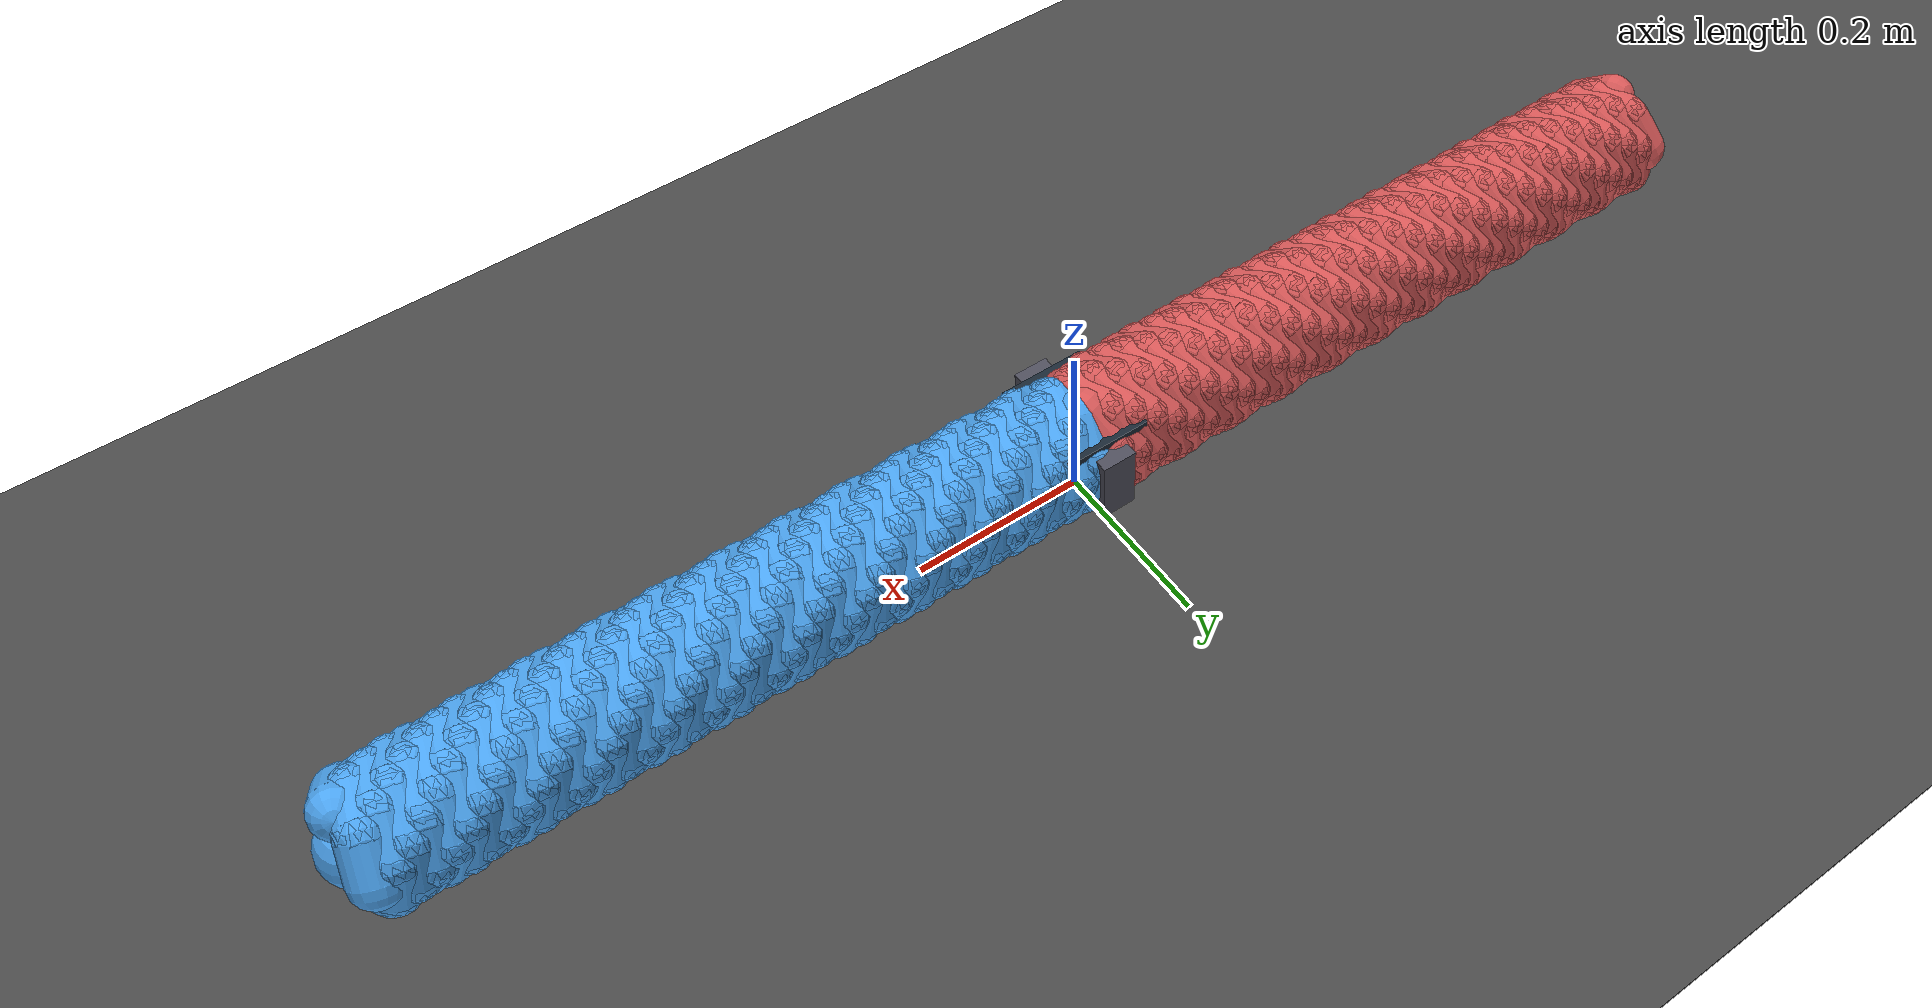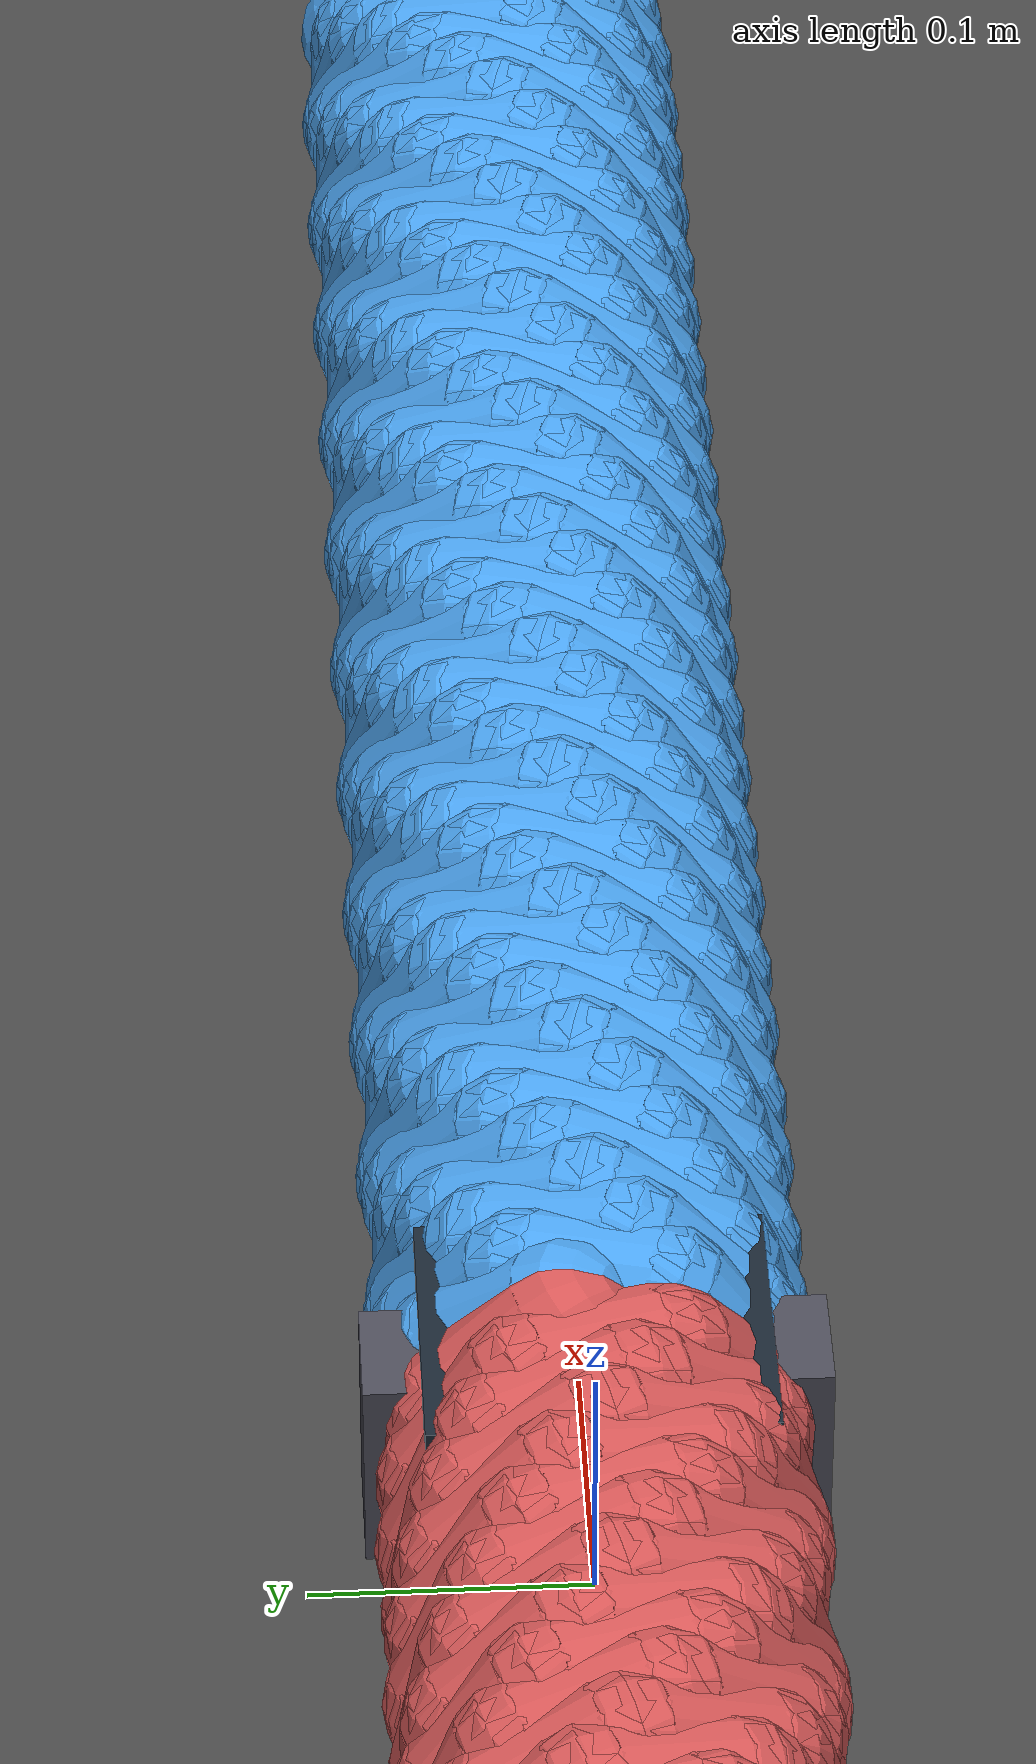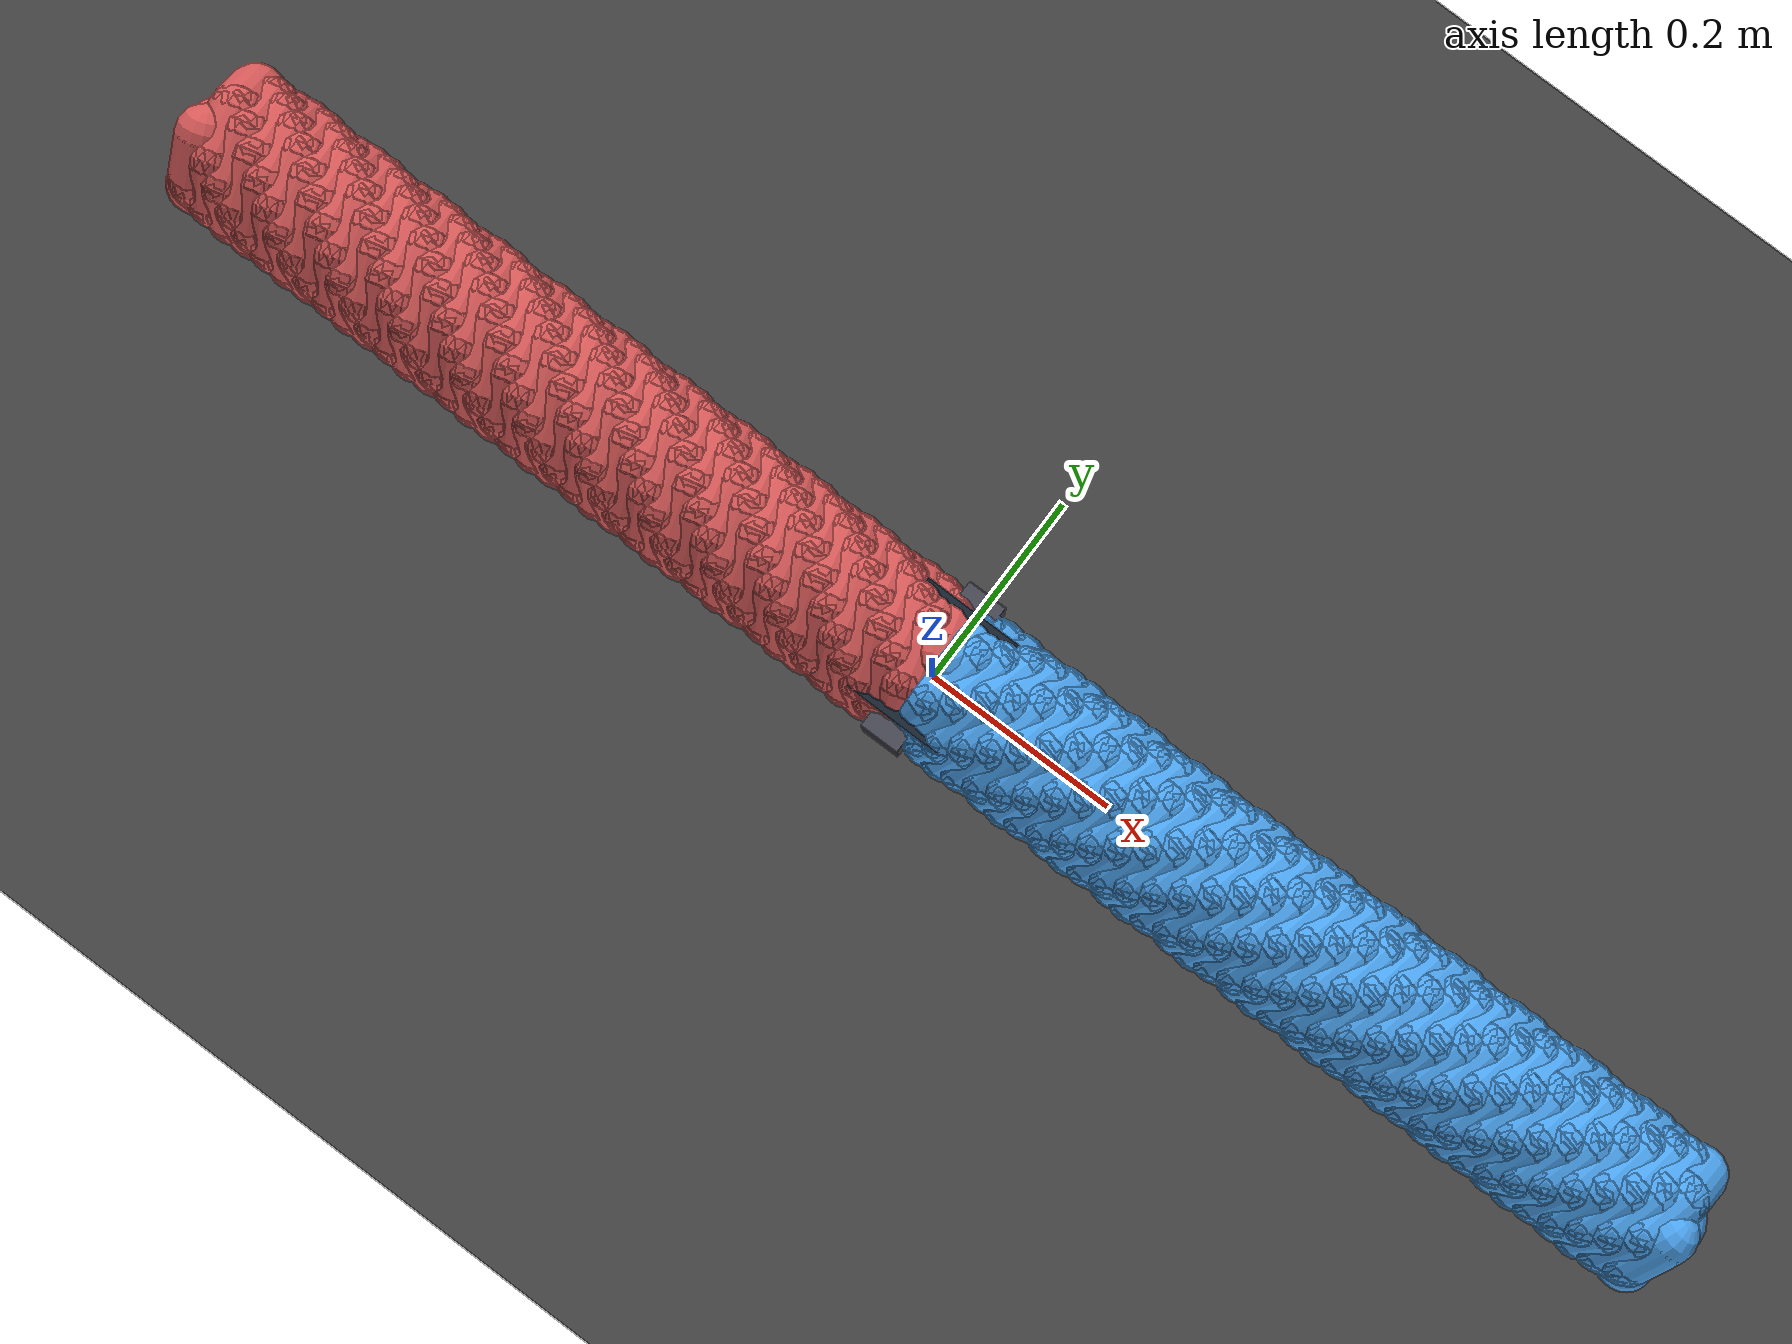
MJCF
<mujoco model="screw_snake">
  <compiler angle="degree" coordinate="local" autolimits="true" inertiafromgeom="true"/>
  <option timestep="0.001" gravity="0 0 -9.81" integrator="implicitfast" iterations="100" solver="Newton"/>

  <default>
    <geom rgba="0.8 0.8 0.8 1" condim="6" friction="6.0 0.01 0.002"
          solref="0.003 1" solimp="0.96 0.96 0.01"/>
    <joint armature="0.001" damping="0.05"/>
    <motor ctrllimited="false"/>   <!-- velocity actuators -->
  </default>

  <worldbody>
    <!-- Hard ground plane (backup) -->
    <geom name="ground" type="plane" size="10 10 0.2" rgba="0.20 0.20 0.20 1" friction="2.5 0.01 0.002"/>

    <!-- Compliant soft mat for ribs to bite into -->
    <body pos="0 0 0.002">
      <geom name="mat" type="box" size="8 8 0.002" rgba="0.28 0.28 0.28 1"
            friction="6.0 0.01 0.002" solref="0.004 2.0" solimp="0.90 0.95 0.001"/>
    </body>

    <!-- Ridges: enable for X-only travel; disable for Y travel to avoid hopping -->

    <body name="snake_base" pos="0 0 0.0785">
      <!-- Allow translation in X, Y, Z (no rotations) so we can demonstrate X vs Y motion -->
      <joint name="slide_x" type="slide" axis="1 0 0" limited="false" damping="0.2"/>
      <joint name="slide_y" type="slide" axis="0 1 0" limited="false" damping="0.8"/>
      <joint name="slide_z" type="slide" axis="0 0 1" limited="false" damping="2.0"/>

      <!-- mid chassis (no contact) - heavier for more normal force -->
      <geom name="chassis" type="box" size="0.05 0.06 0.02" pos="0 0 0.03"
            rgba="0.1 0.15 0.2 1" mass="1.0" contype="0" conaffinity="0"/>

      <!-- CENTER OBJECT: Connects screws, adds mass/inertia -->
      <!-- Note: Y motion blocked by removing slide_y joint, not by friction -->
      <geom name="center_keel" type="box" size="0.02 0.08 0.04" pos="0 0 0"
            rgba="0.3 0.3 0.35 1" mass="0.20"/>

      <!-- Left half: RIGHT-HAND (red), extends along X -->

    <body name="screw_right" pos="-0.405 0 0">
      <!-- Unlimited hinge about +X (screws rotate about X-axis → thrust in Y) -->
      <joint name="jr" type="hinge" axis="1 0 0" pos="0 0 0"
             limited="false" damping="0.001" frictionloss="0.0"/>
      <geom name="core_screw_right" type="cylinder" fromto="-0.4 0 0  0.4 0 0"
            size="0.0425" rgba="0.595 0.24499999999999997 0.24499999999999997 1" mass="0.4"
            contype="0" conaffinity="0"/>
      <geom type="capsule" fromto="-0.4 -0.01112604669781579 0.048746395609091164  -0.39 -0.045048443395120985 0.021694186955877846"
                           size="0.028" rgba="0.85 0.35 0.35 1"
                           friction="3.5 0.01 0.002" mass="0.003"/>
      <geom type="capsule" fromto="-0.39 -0.045048443395120985 0.021694186955877846  -0.38 -0.04504844339512078 -0.021694186955878287"
                           size="0.028" rgba="0.85 0.35 0.35 1"
                           friction="3.5 0.01 0.002" mass="0.003"/>
      <geom type="capsule" fromto="-0.38 -0.04504844339512078 -0.021694186955878287  -0.37 -0.011126046697815658 -0.0487463956090912"
                           size="0.028" rgba="0.85 0.35 0.35 1"
                           friction="3.5 0.01 0.002" mass="0.003"/>
      <geom type="capsule" fromto="-0.37 -0.011126046697815658 -0.0487463956090912  -0.36000000000000004 0.031174490092936727 -0.03909157412340145"
                           size="0.028" rgba="0.85 0.35 0.35 1"
                           friction="3.5 0.01 0.002" mass="0.003"/>
      <geom type="capsule" fromto="-0.36000000000000004 0.031174490092936727 -0.03909157412340145  -0.35000000000000003 0.05 6.123233995736766e-17"
                           size="0.028" rgba="0.85 0.35 0.35 1"
                           friction="3.5 0.01 0.002" mass="0.003"/>
      <geom type="capsule" fromto="-0.35000000000000003 0.05 6.123233995736766e-17  -0.34 0.03117449009293649 0.03909157412340164"
                           size="0.028" rgba="0.85 0.35 0.35 1"
                           friction="3.5 0.01 0.002" mass="0.003"/>
      <geom type="capsule" fromto="-0.34 0.03117449009293649 0.03909157412340164  -0.33 -0.011126046697815778 0.04874639560909117"
                           size="0.028" rgba="0.85 0.35 0.35 1"
                           friction="3.5 0.01 0.002" mass="0.003"/>
      <geom type="capsule" fromto="-0.33 -0.011126046697815778 0.04874639560909117  -0.32 -0.045048443395120985 0.021694186955877857"
                           size="0.028" rgba="0.85 0.35 0.35 1"
                           friction="3.5 0.01 0.002" mass="0.003"/>
      <geom type="capsule" fromto="-0.32 -0.045048443395120985 0.021694186955877857  -0.31000000000000005 -0.045048443395120936 -0.021694186955877957"
                           size="0.028" rgba="0.85 0.35 0.35 1"
                           friction="3.5 0.01 0.002" mass="0.003"/>
      <geom type="capsule" fromto="-0.31000000000000005 -0.045048443395120936 -0.021694186955877957  -0.30000000000000004 -0.01112604669781567 -0.04874639560909119"
                           size="0.028" rgba="0.85 0.35 0.35 1"
                           friction="3.5 0.01 0.002" mass="0.003"/>
      <geom type="capsule" fromto="-0.30000000000000004 -0.01112604669781567 -0.04874639560909119  -0.29000000000000004 0.03117449009293658 -0.03909157412340157"
                           size="0.028" rgba="0.85 0.35 0.35 1"
                           friction="3.5 0.01 0.002" mass="0.003"/>
      <geom type="capsule" fromto="-0.29000000000000004 0.03117449009293658 -0.03909157412340157  -0.28 0.05 4.898587196589413e-17"
                           size="0.028" rgba="0.85 0.35 0.35 1"
                           friction="3.5 0.01 0.002" mass="0.003"/>
      <geom type="capsule" fromto="-0.28 0.05 4.898587196589413e-17  -0.27 0.031174490092936644 0.03909157412340152"
                           size="0.028" rgba="0.85 0.35 0.35 1"
                           friction="3.5 0.01 0.002" mass="0.003"/>
      <geom type="capsule" fromto="-0.27 0.031174490092936644 0.03909157412340152  -0.26 -0.011126046697815938 0.04874639560909114"
                           size="0.028" rgba="0.85 0.35 0.35 1"
                           friction="3.5 0.01 0.002" mass="0.003"/>
      <geom type="capsule" fromto="-0.26 -0.011126046697815938 0.04874639560909114  -0.25 -0.04504844339512098 0.021694186955877867"
                           size="0.028" rgba="0.85 0.35 0.35 1"
                           friction="3.5 0.01 0.002" mass="0.003"/>
      <geom type="capsule" fromto="-0.25 -0.04504844339512098 0.021694186955877867  -0.24000000000000002 -0.04504844339512094 -0.021694186955877947"
                           size="0.028" rgba="0.85 0.35 0.35 1"
                           friction="3.5 0.01 0.002" mass="0.003"/>
      <geom type="capsule" fromto="-0.24000000000000002 -0.04504844339512094 -0.021694186955877947  -0.23 -0.01112604669781568 -0.04874639560909119"
                           size="0.028" rgba="0.85 0.35 0.35 1"
                           friction="3.5 0.01 0.002" mass="0.003"/>
      <geom type="capsule" fromto="-0.23 -0.01112604669781568 -0.04874639560909119  -0.22000000000000003 0.03117449009293671 -0.039091574123401474"
                           size="0.028" rgba="0.85 0.35 0.35 1"
                           friction="3.5 0.01 0.002" mass="0.003"/>
      <geom type="capsule" fromto="-0.22000000000000003 0.03117449009293671 -0.039091574123401474  -0.21000000000000002 0.05 3.6739403974420595e-17"
                           size="0.028" rgba="0.85 0.35 0.35 1"
                           friction="3.5 0.01 0.002" mass="0.003"/>
      <geom type="capsule" fromto="-0.21000000000000002 0.05 3.6739403974420595e-17  -0.2 0.031174490092936647 0.039091574123401515"
                           size="0.028" rgba="0.85 0.35 0.35 1"
                           friction="3.5 0.01 0.002" mass="0.003"/>
      <geom type="capsule" fromto="-0.2 0.031174490092936647 0.039091574123401515  -0.19000000000000003 -0.011126046697815754 0.04874639560909118"
                           size="0.028" rgba="0.85 0.35 0.35 1"
                           friction="3.5 0.01 0.002" mass="0.003"/>
      <geom type="capsule" fromto="-0.19000000000000003 -0.011126046697815754 0.04874639560909118  -0.18000000000000002 -0.04504844339512097 0.02169418695587788"
                           size="0.028" rgba="0.85 0.35 0.35 1"
                           friction="3.5 0.01 0.002" mass="0.003"/>
      <geom type="capsule" fromto="-0.18000000000000002 -0.04504844339512097 0.02169418695587788  -0.17 -0.04504844339512091 -0.021694186955878016"
                           size="0.028" rgba="0.85 0.35 0.35 1"
                           friction="3.5 0.01 0.002" mass="0.003"/>
      <geom type="capsule" fromto="-0.17 -0.04504844339512091 -0.021694186955878016  -0.16000000000000003 -0.01112604669781578 -0.048746395609091164"
                           size="0.028" rgba="0.85 0.35 0.35 1"
                           friction="3.5 0.01 0.002" mass="0.003"/>
      <geom type="capsule" fromto="-0.16000000000000003 -0.01112604669781578 -0.048746395609091164  -0.15000000000000002 0.0311744900929367 -0.039091574123401474"
                           size="0.028" rgba="0.85 0.35 0.35 1"
                           friction="3.5 0.01 0.002" mass="0.003"/>
      <geom type="capsule" fromto="-0.15000000000000002 0.0311744900929367 -0.039091574123401474  -0.14 0.05 2.4492935982947065e-17"
                           size="0.028" rgba="0.85 0.35 0.35 1"
                           friction="3.5 0.01 0.002" mass="0.003"/>
      <geom type="capsule" fromto="-0.14 0.05 2.4492935982947065e-17  -0.13 0.03117449009293659 0.039091574123401564"
                           size="0.028" rgba="0.85 0.35 0.35 1"
                           friction="3.5 0.01 0.002" mass="0.003"/>
      <geom type="capsule" fromto="-0.13 0.03117449009293659 0.039091574123401564  -0.12 -0.011126046697815828 0.04874639560909116"
                           size="0.028" rgba="0.85 0.35 0.35 1"
                           friction="3.5 0.01 0.002" mass="0.003"/>
      <geom type="capsule" fromto="-0.12 -0.011126046697815828 0.04874639560909116  -0.11000000000000004 -0.04504844339512093 0.02169418695587797"
                           size="0.028" rgba="0.85 0.35 0.35 1"
                           friction="3.5 0.01 0.002" mass="0.003"/>
      <geom type="capsule" fromto="-0.11000000000000004 -0.04504844339512093 0.02169418695587797  -0.10000000000000003 -0.045048443395120985 -0.021694186955877843"
                           size="0.028" rgba="0.85 0.35 0.35 1"
                           friction="3.5 0.01 0.002" mass="0.003"/>
      <geom type="capsule" fromto="-0.10000000000000003 -0.045048443395120985 -0.021694186955877843  -0.09000000000000002 -0.011126046697815792 -0.048746395609091164"
                           size="0.028" rgba="0.85 0.35 0.35 1"
                           friction="3.5 0.01 0.002" mass="0.003"/>
      <geom type="capsule" fromto="-0.09000000000000002 -0.011126046697815792 -0.048746395609091164  -0.08000000000000002 0.031174490092936654 -0.039091574123401515"
                           size="0.028" rgba="0.85 0.35 0.35 1"
                           friction="3.5 0.01 0.002" mass="0.003"/>
      <geom type="capsule" fromto="-0.08000000000000002 0.031174490092936654 -0.039091574123401515  -0.07 0.05 1.2246467991473533e-17"
                           size="0.028" rgba="0.85 0.35 0.35 1"
                           friction="3.5 0.01 0.002" mass="0.003"/>
      <geom type="capsule" fromto="-0.07 0.05 1.2246467991473533e-17  -0.06 0.031174490092936637 0.03909157412340153"
                           size="0.028" rgba="0.85 0.35 0.35 1"
                           friction="3.5 0.01 0.002" mass="0.003"/>
      <geom type="capsule" fromto="-0.06 0.031174490092936637 0.03909157412340153  -0.04999999999999999 -0.011126046697815773 0.04874639560909117"
                           size="0.028" rgba="0.85 0.35 0.35 1"
                           friction="3.5 0.01 0.002" mass="0.003"/>
      <geom type="capsule" fromto="-0.04999999999999999 -0.011126046697815773 0.04874639560909117  -0.040000000000000036 -0.0450484433951209 0.02169418695587802"
                           size="0.028" rgba="0.85 0.35 0.35 1"
                           friction="3.5 0.01 0.002" mass="0.003"/>
      <geom type="capsule" fromto="-0.040000000000000036 -0.0450484433951209 0.02169418695587802  -0.030000000000000027 -0.045048443395121006 -0.02169418695587781"
                           size="0.028" rgba="0.85 0.35 0.35 1"
                           friction="3.5 0.01 0.002" mass="0.003"/>
      <geom type="capsule" fromto="-0.030000000000000027 -0.045048443395121006 -0.02169418695587781  -0.020000000000000018 -0.011126046697815783 -0.048746395609091164"
                           size="0.028" rgba="0.85 0.35 0.35 1"
                           friction="3.5 0.01 0.002" mass="0.003"/>
      <geom type="capsule" fromto="-0.020000000000000018 -0.011126046697815783 -0.048746395609091164  -0.010000000000000009 0.031174490092936654 -0.039091574123401515"
                           size="0.028" rgba="0.85 0.35 0.35 1"
                           friction="3.5 0.01 0.002" mass="0.003"/>
      <geom type="capsule" fromto="-0.010000000000000009 0.031174490092936654 -0.039091574123401515  0.0 0.05 0.0"
                           size="0.028" rgba="0.85 0.35 0.35 1"
                           friction="3.5 0.01 0.002" mass="0.003"/>
      <geom type="capsule" fromto="0.0 0.05 0.0  0.010000000000000009 0.031174490092936654 0.039091574123401515"
                           size="0.028" rgba="0.85 0.35 0.35 1"
                           friction="3.5 0.01 0.002" mass="0.003"/>
      <geom type="capsule" fromto="0.010000000000000009 0.031174490092936654 0.039091574123401515  0.019999999999999962 -0.011126046697815544 0.04874639560909122"
                           size="0.028" rgba="0.85 0.35 0.35 1"
                           friction="3.5 0.01 0.002" mass="0.003"/>
      <geom type="capsule" fromto="0.019999999999999962 -0.011126046697815544 0.04874639560909122  0.02999999999999997 -0.04504844339512089 0.02169418695587805"
                           size="0.028" rgba="0.85 0.35 0.35 1"
                           friction="3.5 0.01 0.002" mass="0.003"/>
      <geom type="capsule" fromto="0.02999999999999997 -0.04504844339512089 0.02169418695587805  0.03999999999999998 -0.04504844339512101 -0.0216941869558778"
                           size="0.028" rgba="0.85 0.35 0.35 1"
                           friction="3.5 0.01 0.002" mass="0.003"/>
      <geom type="capsule" fromto="0.03999999999999998 -0.04504844339512101 -0.0216941869558778  0.04999999999999999 -0.011126046697815773 -0.04874639560909117"
                           size="0.028" rgba="0.85 0.35 0.35 1"
                           friction="3.5 0.01 0.002" mass="0.003"/>
      <geom type="capsule" fromto="0.04999999999999999 -0.011126046697815773 -0.04874639560909117  0.06 0.031174490092936637 -0.03909157412340153"
                           size="0.028" rgba="0.85 0.35 0.35 1"
                           friction="3.5 0.01 0.002" mass="0.003"/>
      <geom type="capsule" fromto="0.06 0.031174490092936637 -0.03909157412340153  0.07 0.05 -1.2246467991473533e-17"
                           size="0.028" rgba="0.85 0.35 0.35 1"
                           friction="3.5 0.01 0.002" mass="0.003"/>
      <geom type="capsule" fromto="0.07 0.05 -1.2246467991473533e-17  0.07999999999999996 0.031174490092936866 0.03909157412340135"
                           size="0.028" rgba="0.85 0.35 0.35 1"
                           friction="3.5 0.01 0.002" mass="0.003"/>
      <geom type="capsule" fromto="0.07999999999999996 0.031174490092936866 0.03909157412340135  0.08999999999999997 -0.011126046697815533 0.04874639560909123"
                           size="0.028" rgba="0.85 0.35 0.35 1"
                           friction="3.5 0.01 0.002" mass="0.003"/>
      <geom type="capsule" fromto="0.08999999999999997 -0.011126046697815533 0.04874639560909123  0.09999999999999998 -0.04504844339512091 0.021694186955878006"
                           size="0.028" rgba="0.85 0.35 0.35 1"
                           friction="3.5 0.01 0.002" mass="0.003"/>
      <geom type="capsule" fromto="0.09999999999999998 -0.04504844339512091 0.021694186955878006  0.10999999999999999 -0.045048443395121006 -0.02169418695587781"
                           size="0.028" rgba="0.85 0.35 0.35 1"
                           friction="3.5 0.01 0.002" mass="0.003"/>
      <geom type="capsule" fromto="0.10999999999999999 -0.045048443395121006 -0.02169418695587781  0.12 -0.011126046697815828 -0.04874639560909116"
                           size="0.028" rgba="0.85 0.35 0.35 1"
                           friction="3.5 0.01 0.002" mass="0.003"/>
      <geom type="capsule" fromto="0.12 -0.011126046697815828 -0.04874639560909116  0.13 0.03117449009293659 -0.039091574123401564"
                           size="0.028" rgba="0.85 0.35 0.35 1"
                           friction="3.5 0.01 0.002" mass="0.003"/>
      <geom type="capsule" fromto="0.13 0.03117449009293659 -0.039091574123401564  0.14 0.05 -2.4492935982947065e-17"
                           size="0.028" rgba="0.85 0.35 0.35 1"
                           friction="3.5 0.01 0.002" mass="0.003"/>
      <geom type="capsule" fromto="0.14 0.05 -2.4492935982947065e-17  0.15000000000000002 0.0311744900929367 0.039091574123401474"
                           size="0.028" rgba="0.85 0.35 0.35 1"
                           friction="3.5 0.01 0.002" mass="0.003"/>
      <geom type="capsule" fromto="0.15000000000000002 0.0311744900929367 0.039091574123401474  0.16000000000000003 -0.01112604669781578 0.048746395609091164"
                           size="0.028" rgba="0.85 0.35 0.35 1"
                           friction="3.5 0.01 0.002" mass="0.003"/>
      <geom type="capsule" fromto="0.16000000000000003 -0.01112604669781578 0.048746395609091164  0.17000000000000004 -0.045048443395120985 0.021694186955877853"
                           size="0.028" rgba="0.85 0.35 0.35 1"
                           friction="3.5 0.01 0.002" mass="0.003"/>
      <geom type="capsule" fromto="0.17000000000000004 -0.045048443395120985 0.021694186955877853  0.17999999999999994 -0.045048443395121124 -0.021694186955877562"
                           size="0.028" rgba="0.85 0.35 0.35 1"
                           friction="3.5 0.01 0.002" mass="0.003"/>
      <geom type="capsule" fromto="0.17999999999999994 -0.045048443395121124 -0.021694186955877562  0.18999999999999995 -0.011126046697816099 -0.048746395609091095"
                           size="0.028" rgba="0.85 0.35 0.35 1"
                           friction="3.5 0.01 0.002" mass="0.003"/>
      <geom type="capsule" fromto="0.18999999999999995 -0.011126046697816099 -0.048746395609091095  0.19999999999999996 0.031174490092936515 -0.039091574123401626"
                           size="0.028" rgba="0.85 0.35 0.35 1"
                           friction="3.5 0.01 0.002" mass="0.003"/>
      <geom type="capsule" fromto="0.19999999999999996 0.031174490092936515 -0.039091574123401626  0.20999999999999996 0.05 -3.9201077185447073e-16"
                           size="0.028" rgba="0.85 0.35 0.35 1"
                           friction="3.5 0.01 0.002" mass="0.003"/>
      <geom type="capsule" fromto="0.20999999999999996 0.05 -3.9201077185447073e-16  0.21999999999999997 0.03117449009293685 0.03909157412340136"
                           size="0.028" rgba="0.85 0.35 0.35 1"
                           friction="3.5 0.01 0.002" mass="0.003"/>
      <geom type="capsule" fromto="0.21999999999999997 0.03117449009293685 0.03909157412340136  0.22999999999999998 -0.011126046697815507 0.048746395609091234"
                           size="0.028" rgba="0.85 0.35 0.35 1"
                           friction="3.5 0.01 0.002" mass="0.003"/>
      <geom type="capsule" fromto="0.22999999999999998 -0.011126046697815507 0.048746395609091234  0.24 -0.04504844339512087 0.021694186955878103"
                           size="0.028" rgba="0.85 0.35 0.35 1"
                           friction="3.5 0.01 0.002" mass="0.003"/>
      <geom type="capsule" fromto="0.24 -0.04504844339512087 0.021694186955878103  0.25 -0.04504844339512098 -0.021694186955877867"
                           size="0.028" rgba="0.85 0.35 0.35 1"
                           friction="3.5 0.01 0.002" mass="0.003"/>
      <geom type="capsule" fromto="0.25 -0.04504844339512098 -0.021694186955877867  0.26 -0.011126046697815938 -0.04874639560909114"
                           size="0.028" rgba="0.85 0.35 0.35 1"
                           friction="3.5 0.01 0.002" mass="0.003"/>
      <geom type="capsule" fromto="0.26 -0.011126046697815938 -0.04874639560909114  0.27 0.031174490092936644 -0.03909157412340152"
                           size="0.028" rgba="0.85 0.35 0.35 1"
                           friction="3.5 0.01 0.002" mass="0.003"/>
      <geom type="capsule" fromto="0.27 0.031174490092936644 -0.03909157412340152  0.28 0.05 -4.898587196589413e-17"
                           size="0.028" rgba="0.85 0.35 0.35 1"
                           friction="3.5 0.01 0.002" mass="0.003"/>
      <geom type="capsule" fromto="0.28 0.05 -4.898587196589413e-17  0.29000000000000004 0.03117449009293658 0.03909157412340157"
                           size="0.028" rgba="0.85 0.35 0.35 1"
                           friction="3.5 0.01 0.002" mass="0.003"/>
      <geom type="capsule" fromto="0.29000000000000004 0.03117449009293658 0.03909157412340157  0.30000000000000004 -0.01112604669781567 0.04874639560909119"
                           size="0.028" rgba="0.85 0.35 0.35 1"
                           friction="3.5 0.01 0.002" mass="0.003"/>
      <geom type="capsule" fromto="0.30000000000000004 -0.01112604669781567 0.04874639560909119  0.30999999999999994 -0.04504844339512071 0.021694186955878436"
                           size="0.028" rgba="0.85 0.35 0.35 1"
                           friction="3.5 0.01 0.002" mass="0.003"/>
      <geom type="capsule" fromto="0.30999999999999994 -0.04504844339512071 0.021694186955878436  0.31999999999999995 -0.04504844339512114 -0.021694186955877538"
                           size="0.028" rgba="0.85 0.35 0.35 1"
                           friction="3.5 0.01 0.002" mass="0.003"/>
      <geom type="capsule" fromto="0.31999999999999995 -0.04504844339512114 -0.021694186955877538  0.32999999999999996 -0.011126046697815951 -0.04874639560909113"
                           size="0.028" rgba="0.85 0.35 0.35 1"
                           friction="3.5 0.01 0.002" mass="0.003"/>
      <geom type="capsule" fromto="0.32999999999999996 -0.011126046697815951 -0.04874639560909113  0.33999999999999997 0.031174490092936352 -0.03909157412340175"
                           size="0.028" rgba="0.85 0.35 0.35 1"
                           friction="3.5 0.01 0.002" mass="0.003"/>
      <geom type="capsule" fromto="0.33999999999999997 0.031174490092936352 -0.03909157412340175  0.35 0.05 -4.165037078374178e-16"
                           size="0.028" rgba="0.85 0.35 0.35 1"
                           friction="3.5 0.01 0.002" mass="0.003"/>
      <geom type="capsule" fromto="0.35 0.05 -4.165037078374178e-16  0.36 0.031174490092936727 0.03909157412340145"
                           size="0.028" rgba="0.85 0.35 0.35 1"
                           friction="3.5 0.01 0.002" mass="0.003"/>
      <geom type="capsule" fromto="0.36 0.031174490092936727 0.03909157412340145  0.37 -0.011126046697815658 0.0487463956090912"
                           size="0.028" rgba="0.85 0.35 0.35 1"
                           friction="3.5 0.01 0.002" mass="0.003"/>
      <geom type="capsule" fromto="0.37 -0.011126046697815658 0.0487463956090912  0.38 -0.04504844339512078 0.021694186955878287"
                           size="0.028" rgba="0.85 0.35 0.35 1"
                           friction="3.5 0.01 0.002" mass="0.003"/>
      <geom type="capsule" fromto="0.38 -0.04504844339512078 0.021694186955878287  0.39 -0.045048443395120985 -0.021694186955877846"
                           size="0.028" rgba="0.85 0.35 0.35 1"
                           friction="3.5 0.01 0.002" mass="0.003"/>
      <geom type="capsule" fromto="0.39 -0.045048443395120985 -0.021694186955877846  0.4 -0.01112604669781579 -0.048746395609091164"
                           size="0.028" rgba="0.85 0.35 0.35 1"
                           friction="3.5 0.01 0.002" mass="0.003"/>
      <geom type="capsule" fromto="-0.4 -0.04874639560909115 -0.011126046697815873  -0.39 -0.02169418695587777 -0.04504844339512103"
                           size="0.028" rgba="0.85 0.35 0.35 1"
                           friction="3.5 0.01 0.002" mass="0.003"/>
      <geom type="capsule" fromto="-0.39 -0.02169418695587777 -0.04504844339512103  -0.38 0.021694186955878367 -0.045048443395120735"
                           size="0.028" rgba="0.85 0.35 0.35 1"
                           friction="3.5 0.01 0.002" mass="0.003"/>
      <geom type="capsule" fromto="-0.38 0.021694186955878367 -0.045048443395120735  -0.37 0.04874639560909122 -0.011126046697815575"
                           size="0.028" rgba="0.85 0.35 0.35 1"
                           friction="3.5 0.01 0.002" mass="0.003"/>
      <geom type="capsule" fromto="-0.37 0.04874639560909122 -0.011126046697815575  -0.36000000000000004 0.0390915741234014 0.031174490092936793"
                           size="0.028" rgba="0.85 0.35 0.35 1"
                           friction="3.5 0.01 0.002" mass="0.003"/>
      <geom type="capsule" fromto="-0.36000000000000004 0.0390915741234014 0.031174490092936793  -0.35000000000000003 -1.469885649295118e-16 0.05"
                           size="0.028" rgba="0.85 0.35 0.35 1"
                           friction="3.5 0.01 0.002" mass="0.003"/>
      <geom type="capsule" fromto="-0.35000000000000003 -1.469885649295118e-16 0.05  -0.34 -0.039091574123401585 0.031174490092936564"
                           size="0.028" rgba="0.85 0.35 0.35 1"
                           friction="3.5 0.01 0.002" mass="0.003"/>
      <geom type="capsule" fromto="-0.34 -0.039091574123401585 0.031174490092936564  -0.33 -0.04874639560909115 -0.011126046697815861"
                           size="0.028" rgba="0.85 0.35 0.35 1"
                           friction="3.5 0.01 0.002" mass="0.003"/>
      <geom type="capsule" fromto="-0.33 -0.04874639560909115 -0.011126046697815861  -0.32 -0.02169418695587778 -0.04504844339512102"
                           size="0.028" rgba="0.85 0.35 0.35 1"
                           friction="3.5 0.01 0.002" mass="0.003"/>
      <geom type="capsule" fromto="-0.32 -0.02169418695587778 -0.04504844339512102  -0.31000000000000005 0.021694186955878034 -0.0450484433951209"
                           size="0.028" rgba="0.85 0.35 0.35 1"
                           friction="3.5 0.01 0.002" mass="0.003"/>
      <geom type="capsule" fromto="-0.31000000000000005 0.021694186955878034 -0.0450484433951209  -0.30000000000000004 0.04874639560909121 -0.011126046697815585"
                           size="0.028" rgba="0.85 0.35 0.35 1"
                           friction="3.5 0.01 0.002" mass="0.003"/>
      <geom type="capsule" fromto="-0.30000000000000004 0.04874639560909121 -0.011126046697815585  -0.29000000000000004 0.03909157412340163 0.03117449009293651"
                           size="0.028" rgba="0.85 0.35 0.35 1"
                           friction="3.5 0.01 0.002" mass="0.003"/>
      <geom type="capsule" fromto="-0.29000000000000004 0.03909157412340163 0.03117449009293651  -0.28 -1.3474209693803828e-16 0.05"
                           size="0.028" rgba="0.85 0.35 0.35 1"
                           friction="3.5 0.01 0.002" mass="0.003"/>
      <geom type="capsule" fromto="-0.28 -1.3474209693803828e-16 0.05  -0.27 -0.03909157412340158 0.031174490092936574"
                           size="0.028" rgba="0.85 0.35 0.35 1"
                           friction="3.5 0.01 0.002" mass="0.003"/>
      <geom type="capsule" fromto="-0.27 -0.03909157412340158 0.031174490092936574  -0.26 -0.04874639560909116 -0.011126046697815849"
                           size="0.028" rgba="0.85 0.35 0.35 1"
                           friction="3.5 0.01 0.002" mass="0.003"/>
      <geom type="capsule" fromto="-0.26 -0.04874639560909116 -0.011126046697815849  -0.25 -0.02169418695587779 -0.04504844339512101"
                           size="0.028" rgba="0.85 0.35 0.35 1"
                           friction="3.5 0.01 0.002" mass="0.003"/>
      <geom type="capsule" fromto="-0.25 -0.02169418695587779 -0.04504844339512101  -0.24000000000000002 0.021694186955878023 -0.0450484433951209"
                           size="0.028" rgba="0.85 0.35 0.35 1"
                           friction="3.5 0.01 0.002" mass="0.003"/>
      <geom type="capsule" fromto="-0.24000000000000002 0.021694186955878023 -0.0450484433951209  -0.23 0.04874639560909121 -0.011126046697815598"
                           size="0.028" rgba="0.85 0.35 0.35 1"
                           friction="3.5 0.01 0.002" mass="0.003"/>
      <geom type="capsule" fromto="-0.23 0.04874639560909121 -0.011126046697815598  -0.22000000000000003 0.03909157412340142 0.031174490092936775"
                           size="0.028" rgba="0.85 0.35 0.35 1"
                           friction="3.5 0.01 0.002" mass="0.003"/>
      <geom type="capsule" fromto="-0.22000000000000003 0.03909157412340142 0.031174490092936775  -0.21000000000000002 -1.2249562894656473e-16 0.05"
                           size="0.028" rgba="0.85 0.35 0.35 1"
                           friction="3.5 0.01 0.002" mass="0.003"/>
      <geom type="capsule" fromto="-0.21000000000000002 -1.2249562894656473e-16 0.05  -0.2 -0.03909157412340157 0.03117449009293658"
                           size="0.028" rgba="0.85 0.35 0.35 1"
                           friction="3.5 0.01 0.002" mass="0.003"/>
      <geom type="capsule" fromto="-0.2 -0.03909157412340157 0.03117449009293658  -0.19000000000000003 -0.04874639560909118 -0.01112604669781575"
                           size="0.028" rgba="0.85 0.35 0.35 1"
                           friction="3.5 0.01 0.002" mass="0.003"/>
      <geom type="capsule" fromto="-0.19000000000000003 -0.04874639560909118 -0.01112604669781575  -0.18000000000000002 -0.02169418695587788 -0.04504844339512097"
                           size="0.028" rgba="0.85 0.35 0.35 1"
                           friction="3.5 0.01 0.002" mass="0.003"/>
      <geom type="capsule" fromto="-0.18000000000000002 -0.02169418695587788 -0.04504844339512097  -0.17 0.021694186955878013 -0.04504844339512091"
                           size="0.028" rgba="0.85 0.35 0.35 1"
                           friction="3.5 0.01 0.002" mass="0.003"/>
      <geom type="capsule" fromto="-0.17 0.021694186955878013 -0.04504844339512091  -0.16000000000000003 0.048746395609091164 -0.011126046697815783"
                           size="0.028" rgba="0.85 0.35 0.35 1"
                           friction="3.5 0.01 0.002" mass="0.003"/>
      <geom type="capsule" fromto="-0.16000000000000003 0.048746395609091164 -0.011126046697815783  -0.15000000000000002 0.039091574123401474 0.0311744900929367"
                           size="0.028" rgba="0.85 0.35 0.35 1"
                           friction="3.5 0.01 0.002" mass="0.003"/>
      <geom type="capsule" fromto="-0.15000000000000002 0.039091574123401474 0.0311744900929367  -0.14 -2.1431318985078683e-17 0.05"
                           size="0.028" rgba="0.85 0.35 0.35 1"
                           friction="3.5 0.01 0.002" mass="0.003"/>
      <geom type="capsule" fromto="-0.14 -2.1431318985078683e-17 0.05  -0.13 -0.03909157412340156 0.03117449009293659"
                           size="0.028" rgba="0.85 0.35 0.35 1"
                           friction="3.5 0.01 0.002" mass="0.003"/>
      <geom type="capsule" fromto="-0.13 -0.03909157412340156 0.03117449009293659  -0.12 -0.048746395609091164 -0.011126046697815825"
                           size="0.028" rgba="0.85 0.35 0.35 1"
                           friction="3.5 0.01 0.002" mass="0.003"/>
      <geom type="capsule" fromto="-0.12 -0.048746395609091164 -0.011126046697815825  -0.11000000000000004 -0.021694186955877975 -0.04504844339512093"
                           size="0.028" rgba="0.85 0.35 0.35 1"
                           friction="3.5 0.01 0.002" mass="0.003"/>
      <geom type="capsule" fromto="-0.11000000000000004 -0.021694186955877975 -0.04504844339512093  -0.10000000000000003 0.02169418695587784 -0.04504844339512099"
                           size="0.028" rgba="0.85 0.35 0.35 1"
                           friction="3.5 0.01 0.002" mass="0.003"/>
      <geom type="capsule" fromto="-0.10000000000000003 0.02169418695587784 -0.04504844339512099  -0.09000000000000002 0.048746395609091164 -0.011126046697815795"
                           size="0.028" rgba="0.85 0.35 0.35 1"
                           friction="3.5 0.01 0.002" mass="0.003"/>
      <geom type="capsule" fromto="-0.09000000000000002 0.048746395609091164 -0.011126046697815795  -0.08000000000000002 0.039091574123401515 0.031174490092936654"
                           size="0.028" rgba="0.85 0.35 0.35 1"
                           friction="3.5 0.01 0.002" mass="0.003"/>
      <geom type="capsule" fromto="-0.08000000000000002 0.039091574123401515 0.031174490092936654  -0.07 -9.184850993605149e-18 0.05"
                           size="0.028" rgba="0.85 0.35 0.35 1"
                           friction="3.5 0.01 0.002" mass="0.003"/>
      <geom type="capsule" fromto="-0.07 -9.184850993605149e-18 0.05  -0.06 -0.03909157412340153 0.031174490092936637"
                           size="0.028" rgba="0.85 0.35 0.35 1"
                           friction="3.5 0.01 0.002" mass="0.003"/>
      <geom type="capsule" fromto="-0.06 -0.03909157412340153 0.031174490092936637  -0.04999999999999999 -0.04874639560909117 -0.011126046697815771"
                           size="0.028" rgba="0.85 0.35 0.35 1"
                           friction="3.5 0.01 0.002" mass="0.003"/>
      <geom type="capsule" fromto="-0.04999999999999999 -0.04874639560909117 -0.011126046697815771  -0.040000000000000036 -0.021694186955878023 -0.0450484433951209"
                           size="0.028" rgba="0.85 0.35 0.35 1"
                           friction="3.5 0.01 0.002" mass="0.003"/>
      <geom type="capsule" fromto="-0.040000000000000036 -0.021694186955878023 -0.0450484433951209  -0.030000000000000027 0.02169418695587781 -0.045048443395121006"
                           size="0.028" rgba="0.85 0.35 0.35 1"
                           friction="3.5 0.01 0.002" mass="0.003"/>
      <geom type="capsule" fromto="-0.030000000000000027 0.02169418695587781 -0.045048443395121006  -0.020000000000000018 0.048746395609091164 -0.011126046697815785"
                           size="0.028" rgba="0.85 0.35 0.35 1"
                           friction="3.5 0.01 0.002" mass="0.003"/>
      <geom type="capsule" fromto="-0.020000000000000018 0.048746395609091164 -0.011126046697815785  -0.010000000000000009 0.039091574123401515 0.031174490092936654"
                           size="0.028" rgba="0.85 0.35 0.35 1"
                           friction="3.5 0.01 0.002" mass="0.003"/>
      <geom type="capsule" fromto="-0.010000000000000009 0.039091574123401515 0.031174490092936654  0.0 3.061616997868383e-18 0.05"
                           size="0.028" rgba="0.85 0.35 0.35 1"
                           friction="3.5 0.01 0.002" mass="0.003"/>
      <geom type="capsule" fromto="0.0 3.061616997868383e-18 0.05  0.010000000000000009 -0.039091574123401515 0.031174490092936647"
                           size="0.028" rgba="0.85 0.35 0.35 1"
                           friction="3.5 0.01 0.002" mass="0.003"/>
      <geom type="capsule" fromto="0.010000000000000009 -0.039091574123401515 0.031174490092936647  0.019999999999999962 -0.04874639560909122 -0.011126046697815542"
                           size="0.028" rgba="0.85 0.35 0.35 1"
                           friction="3.5 0.01 0.002" mass="0.003"/>
      <geom type="capsule" fromto="0.019999999999999962 -0.04874639560909122 -0.011126046697815542  0.02999999999999997 -0.021694186955878075 -0.045048443395120874"
                           size="0.028" rgba="0.85 0.35 0.35 1"
                           friction="3.5 0.01 0.002" mass="0.003"/>
      <geom type="capsule" fromto="0.02999999999999997 -0.021694186955878075 -0.045048443395120874  0.03999999999999998 0.02169418695587782 -0.045048443395121006"
                           size="0.028" rgba="0.85 0.35 0.35 1"
                           friction="3.5 0.01 0.002" mass="0.003"/>
      <geom type="capsule" fromto="0.03999999999999998 0.02169418695587782 -0.045048443395121006  0.04999999999999999 0.04874639560909117 -0.011126046697815776"
                           size="0.028" rgba="0.85 0.35 0.35 1"
                           friction="3.5 0.01 0.002" mass="0.003"/>
      <geom type="capsule" fromto="0.04999999999999999 0.04874639560909117 -0.011126046697815776  0.06 0.03909157412340153 0.03117449009293663"
                           size="0.028" rgba="0.85 0.35 0.35 1"
                           friction="3.5 0.01 0.002" mass="0.003"/>
      <geom type="capsule" fromto="0.06 0.03909157412340153 0.03117449009293663  0.07 1.5308084989341915e-17 0.05"
                           size="0.028" rgba="0.85 0.35 0.35 1"
                           friction="3.5 0.01 0.002" mass="0.003"/>
      <geom type="capsule" fromto="0.07 1.5308084989341915e-17 0.05  0.07999999999999996 -0.039091574123401314 0.031174490092936897"
                           size="0.028" rgba="0.85 0.35 0.35 1"
                           friction="3.5 0.01 0.002" mass="0.003"/>
      <geom type="capsule" fromto="0.07999999999999996 -0.039091574123401314 0.031174490092936897  0.08999999999999997 -0.04874639560909123 -0.011126046697815528"
                           size="0.028" rgba="0.85 0.35 0.35 1"
                           friction="3.5 0.01 0.002" mass="0.003"/>
      <geom type="capsule" fromto="0.08999999999999997 -0.04874639560909123 -0.011126046697815528  0.09999999999999998 -0.021694186955878006 -0.04504844339512091"
                           size="0.028" rgba="0.85 0.35 0.35 1"
                           friction="3.5 0.01 0.002" mass="0.003"/>
      <geom type="capsule" fromto="0.09999999999999998 -0.021694186955878006 -0.04504844339512091  0.10999999999999999 0.021694186955877808 -0.045048443395121006"
                           size="0.028" rgba="0.85 0.35 0.35 1"
                           friction="3.5 0.01 0.002" mass="0.003"/>
      <geom type="capsule" fromto="0.10999999999999999 0.021694186955877808 -0.045048443395121006  0.12 0.04874639560909116 -0.011126046697815832"
                           size="0.028" rgba="0.85 0.35 0.35 1"
                           friction="3.5 0.01 0.002" mass="0.003"/>
      <geom type="capsule" fromto="0.12 0.04874639560909116 -0.011126046697815832  0.13 0.039091574123401564 0.031174490092936588"
                           size="0.028" rgba="0.85 0.35 0.35 1"
                           friction="3.5 0.01 0.002" mass="0.003"/>
      <geom type="capsule" fromto="0.13 0.039091574123401564 0.031174490092936588  0.14 2.7554552980815448e-17 0.05"
                           size="0.028" rgba="0.85 0.35 0.35 1"
                           friction="3.5 0.01 0.002" mass="0.003"/>
      <geom type="capsule" fromto="0.14 2.7554552980815448e-17 0.05  0.15000000000000002 -0.039091574123401474 0.0311744900929367"
                           size="0.028" rgba="0.85 0.35 0.35 1"
                           friction="3.5 0.01 0.002" mass="0.003"/>
      <geom type="capsule" fromto="0.15000000000000002 -0.039091574123401474 0.0311744900929367  0.16000000000000003 -0.04874639560909117 -0.011126046697815778"
                           size="0.028" rgba="0.85 0.35 0.35 1"
                           friction="3.5 0.01 0.002" mass="0.003"/>
      <geom type="capsule" fromto="0.16000000000000003 -0.04874639560909117 -0.011126046697815778  0.17000000000000004 -0.021694186955877857 -0.045048443395120985"
                           size="0.028" rgba="0.85 0.35 0.35 1"
                           friction="3.5 0.01 0.002" mass="0.003"/>
      <geom type="capsule" fromto="0.17000000000000004 -0.021694186955877857 -0.045048443395120985  0.17999999999999994 0.021694186955877635 -0.04504844339512109"
                           size="0.028" rgba="0.85 0.35 0.35 1"
                           friction="3.5 0.01 0.002" mass="0.003"/>
      <geom type="capsule" fromto="0.17999999999999994 0.021694186955877635 -0.04504844339512109  0.18999999999999995 0.048746395609091116 -0.011126046697816016"
                           size="0.028" rgba="0.85 0.35 0.35 1"
                           friction="3.5 0.01 0.002" mass="0.003"/>
      <geom type="capsule" fromto="0.18999999999999995 0.048746395609091116 -0.011126046697816016  0.19999999999999996 0.03909157412340168 0.031174490092936442"
                           size="0.028" rgba="0.85 0.35 0.35 1"
                           friction="3.5 0.01 0.002" mass="0.003"/>
      <geom type="capsule" fromto="0.19999999999999996 0.03909157412340168 0.031174490092936442  0.20999999999999996 3.0625454688232656e-16 0.05"
                           size="0.028" rgba="0.85 0.35 0.35 1"
                           friction="3.5 0.01 0.002" mass="0.003"/>
      <geom type="capsule" fromto="0.20999999999999996 3.0625454688232656e-16 0.05  0.21999999999999997 -0.0390915741234013 0.03117449009293692"
                           size="0.028" rgba="0.85 0.35 0.35 1"
                           friction="3.5 0.01 0.002" mass="0.003"/>
      <geom type="capsule" fromto="0.21999999999999997 -0.0390915741234013 0.03117449009293692  0.22999999999999998 -0.04874639560909125 -0.011126046697815419"
                           size="0.028" rgba="0.85 0.35 0.35 1"
                           friction="3.5 0.01 0.002" mass="0.003"/>
      <geom type="capsule" fromto="0.22999999999999998 -0.04874639560909125 -0.011126046697815419  0.24 -0.021694186955878186 -0.04504844339512082"
                           size="0.028" rgba="0.85 0.35 0.35 1"
                           friction="3.5 0.01 0.002" mass="0.003"/>
      <geom type="capsule" fromto="0.24 -0.021694186955878186 -0.04504844339512082  0.25 0.021694186955877947 -0.04504844339512094"
                           size="0.028" rgba="0.85 0.35 0.35 1"
                           friction="3.5 0.01 0.002" mass="0.003"/>
      <geom type="capsule" fromto="0.25 0.021694186955877947 -0.04504844339512094  0.26 0.04874639560909111 -0.011126046697816028"
                           size="0.028" rgba="0.85 0.35 0.35 1"
                           friction="3.5 0.01 0.002" mass="0.003"/>
      <geom type="capsule" fromto="0.26 0.04874639560909111 -0.011126046697816028  0.27 0.039091574123401474 0.03117449009293671"
                           size="0.028" rgba="0.85 0.35 0.35 1"
                           friction="3.5 0.01 0.002" mass="0.003"/>
      <geom type="capsule" fromto="0.27 0.039091574123401474 0.03117449009293671  0.28 -3.6770353006250015e-17 0.05"
                           size="0.028" rgba="0.85 0.35 0.35 1"
                           friction="3.5 0.01 0.002" mass="0.003"/>
      <geom type="capsule" fromto="0.28 -3.6770353006250015e-17 0.05  0.29000000000000004 -0.039091574123401515 0.031174490092936647"
                           size="0.028" rgba="0.85 0.35 0.35 1"
                           friction="3.5 0.01 0.002" mass="0.003"/>
      <geom type="capsule" fromto="0.29000000000000004 -0.039091574123401515 0.031174490092936647  0.30000000000000004 -0.04874639560909118 -0.011126046697815754"
                           size="0.028" rgba="0.85 0.35 0.35 1"
                           friction="3.5 0.01 0.002" mass="0.003"/>
      <geom type="capsule" fromto="0.30000000000000004 -0.04874639560909118 -0.011126046697815754  0.30999999999999994 -0.02169418695587852 -0.045048443395120666"
                           size="0.028" rgba="0.85 0.35 0.35 1"
                           friction="3.5 0.01 0.002" mass="0.003"/>
      <geom type="capsule" fromto="0.30999999999999994 -0.02169418695587852 -0.045048443395120666  0.31999999999999995 0.021694186955877614 -0.045048443395121096"
                           size="0.028" rgba="0.85 0.35 0.35 1"
                           friction="3.5 0.01 0.002" mass="0.003"/>
      <geom type="capsule" fromto="0.31999999999999995 0.021694186955877614 -0.045048443395121096  0.32999999999999996 0.04874639560909111 -0.01112604669781604"
                           size="0.028" rgba="0.85 0.35 0.35 1"
                           friction="3.5 0.01 0.002" mass="0.003"/>
      <geom type="capsule" fromto="0.32999999999999996 0.04874639560909111 -0.01112604669781604  0.33999999999999997 0.039091574123401696 0.03117449009293642"
                           size="0.028" rgba="0.85 0.35 0.35 1"
                           friction="3.5 0.01 0.002" mass="0.003"/>
      <geom type="capsule" fromto="0.33999999999999997 0.039091574123401696 0.03117449009293642  0.35 3.307474828652736e-16 0.05"
                           size="0.028" rgba="0.85 0.35 0.35 1"
                           friction="3.5 0.01 0.002" mass="0.003"/>
      <geom type="capsule" fromto="0.35 3.307474828652736e-16 0.05  0.36 -0.03909157412340151 0.031174490092936658"
                           size="0.028" rgba="0.85 0.35 0.35 1"
                           friction="3.5 0.01 0.002" mass="0.003"/>
      <geom type="capsule" fromto="0.36 -0.03909157412340151 0.031174490092936658  0.37 -0.04874639560909118 -0.011126046697815742"
                           size="0.028" rgba="0.85 0.35 0.35 1"
                           friction="3.5 0.01 0.002" mass="0.003"/>
      <geom type="capsule" fromto="0.37 -0.04874639560909118 -0.011126046697815742  0.38 -0.02169418695587821 -0.04504844339512082"
                           size="0.028" rgba="0.85 0.35 0.35 1"
                           friction="3.5 0.01 0.002" mass="0.003"/>
      <geom type="capsule" fromto="0.38 -0.02169418695587821 -0.04504844339512082  0.39 0.021694186955877923 -0.04504844339512095"
                           size="0.028" rgba="0.85 0.35 0.35 1"
                           friction="3.5 0.01 0.002" mass="0.003"/>
      <geom type="capsule" fromto="0.39 0.021694186955877923 -0.04504844339512095  0.4 0.04874639560909119 -0.011126046697815705"
                           size="0.028" rgba="0.85 0.35 0.35 1"
                           friction="3.5 0.01 0.002" mass="0.003"/>
      <geom type="capsule" fromto="-0.4 0.011126046697815957 -0.04874639560909113  -0.39 0.045048443395120985 -0.021694186955877853"
                           size="0.028" rgba="0.85 0.35 0.35 1"
                           friction="3.5 0.01 0.002" mass="0.003"/>
      <geom type="capsule" fromto="-0.39 0.045048443395120985 -0.021694186955877853  -0.38 0.04504844339512078 0.021694186955878283"
                           size="0.028" rgba="0.85 0.35 0.35 1"
                           friction="3.5 0.01 0.002" mass="0.003"/>
      <geom type="capsule" fromto="-0.38 0.04504844339512078 0.021694186955878283  -0.37 0.011126046697815663 0.04874639560909119"
                           size="0.028" rgba="0.85 0.35 0.35 1"
                           friction="3.5 0.01 0.002" mass="0.003"/>
      <geom type="capsule" fromto="-0.37 0.011126046697815663 0.04874639560909119  -0.36000000000000004 -0.031174490092936727 0.03909157412340146"
                           size="0.028" rgba="0.85 0.35 0.35 1"
                           friction="3.5 0.01 0.002" mass="0.003"/>
      <geom type="capsule" fromto="-0.36000000000000004 -0.031174490092936727 0.03909157412340146  -0.35000000000000003 -0.05 -5.5109105961630896e-17"
                           size="0.028" rgba="0.85 0.35 0.35 1"
                           friction="3.5 0.01 0.002" mass="0.003"/>
      <geom type="capsule" fromto="-0.35000000000000003 -0.05 -5.5109105961630896e-17  -0.34 -0.031174490092936498 -0.03909157412340164"
                           size="0.028" rgba="0.85 0.35 0.35 1"
                           friction="3.5 0.01 0.002" mass="0.003"/>
      <geom type="capsule" fromto="-0.34 -0.031174490092936498 -0.03909157412340164  -0.33 0.011126046697815771 -0.04874639560909117"
                           size="0.028" rgba="0.85 0.35 0.35 1"
                           friction="3.5 0.01 0.002" mass="0.003"/>
      <geom type="capsule" fromto="-0.33 0.011126046697815771 -0.04874639560909117  -0.32 0.045048443395120985 -0.021694186955877864"
                           size="0.028" rgba="0.85 0.35 0.35 1"
                           friction="3.5 0.01 0.002" mass="0.003"/>
      <geom type="capsule" fromto="-0.32 0.045048443395120985 -0.021694186955877864  -0.31000000000000005 0.045048443395120936 0.02169418695587795"
                           size="0.028" rgba="0.85 0.35 0.35 1"
                           friction="3.5 0.01 0.002" mass="0.003"/>
      <geom type="capsule" fromto="-0.31000000000000005 0.045048443395120936 0.02169418695587795  -0.30000000000000004 0.011126046697815676 0.04874639560909119"
                           size="0.028" rgba="0.85 0.35 0.35 1"
                           friction="3.5 0.01 0.002" mass="0.003"/>
      <geom type="capsule" fromto="-0.30000000000000004 0.011126046697815676 0.04874639560909119  -0.29000000000000004 -0.031174490092936574 0.03909157412340158"
                           size="0.028" rgba="0.85 0.35 0.35 1"
                           friction="3.5 0.01 0.002" mass="0.003"/>
      <geom type="capsule" fromto="-0.29000000000000004 -0.031174490092936574 0.03909157412340158  -0.28 -0.05 -4.2862637970157366e-17"
                           size="0.028" rgba="0.85 0.35 0.35 1"
                           friction="3.5 0.01 0.002" mass="0.003"/>
      <geom type="capsule" fromto="-0.28 -0.05 -4.2862637970157366e-17  -0.27 -0.031174490092936647 -0.039091574123401515"
                           size="0.028" rgba="0.85 0.35 0.35 1"
                           friction="3.5 0.01 0.002" mass="0.003"/>
      <geom type="capsule" fromto="-0.27 -0.031174490092936647 -0.039091574123401515  -0.26 0.011126046697815932 -0.04874639560909114"
                           size="0.028" rgba="0.85 0.35 0.35 1"
                           friction="3.5 0.01 0.002" mass="0.003"/>
      <geom type="capsule" fromto="-0.26 0.011126046697815932 -0.04874639560909114  -0.25 0.04504844339512098 -0.021694186955877874"
                           size="0.028" rgba="0.85 0.35 0.35 1"
                           friction="3.5 0.01 0.002" mass="0.003"/>
      <geom type="capsule" fromto="-0.25 0.04504844339512098 -0.021694186955877874  -0.24000000000000002 0.04504844339512094 0.02169418695587794"
                           size="0.028" rgba="0.85 0.35 0.35 1"
                           friction="3.5 0.01 0.002" mass="0.003"/>
      <geom type="capsule" fromto="-0.24000000000000002 0.04504844339512094 0.02169418695587794  -0.23 0.011126046697815688 0.04874639560909119"
                           size="0.028" rgba="0.85 0.35 0.35 1"
                           friction="3.5 0.01 0.002" mass="0.003"/>
      <geom type="capsule" fromto="-0.23 0.011126046697815688 0.04874639560909119  -0.22000000000000003 -0.031174490092936703 0.039091574123401474"
                           size="0.028" rgba="0.85 0.35 0.35 1"
                           friction="3.5 0.01 0.002" mass="0.003"/>
      <geom type="capsule" fromto="-0.22000000000000003 -0.031174490092936703 0.039091574123401474  -0.21000000000000002 -0.05 -3.061616997868383e-17"
                           size="0.028" rgba="0.85 0.35 0.35 1"
                           friction="3.5 0.01 0.002" mass="0.003"/>
      <geom type="capsule" fromto="-0.21000000000000002 -0.05 -3.061616997868383e-17  -0.2 -0.031174490092936654 -0.03909157412340151"
                           size="0.028" rgba="0.85 0.35 0.35 1"
                           friction="3.5 0.01 0.002" mass="0.003"/>
      <geom type="capsule" fromto="-0.2 -0.031174490092936654 -0.03909157412340151  -0.19000000000000003 0.011126046697815747 -0.04874639560909118"
                           size="0.028" rgba="0.85 0.35 0.35 1"
                           friction="3.5 0.01 0.002" mass="0.003"/>
      <geom type="capsule" fromto="-0.19000000000000003 0.011126046697815747 -0.04874639560909118  -0.18000000000000002 0.04504844339512097 -0.021694186955877885"
                           size="0.028" rgba="0.85 0.35 0.35 1"
                           friction="3.5 0.01 0.002" mass="0.003"/>
      <geom type="capsule" fromto="-0.18000000000000002 0.04504844339512097 -0.021694186955877885  -0.17 0.04504844339512091 0.02169418695587801"
                           size="0.028" rgba="0.85 0.35 0.35 1"
                           friction="3.5 0.01 0.002" mass="0.003"/>
      <geom type="capsule" fromto="-0.17 0.04504844339512091 0.02169418695587801  -0.16000000000000003 0.011126046697815785 0.048746395609091164"
                           size="0.028" rgba="0.85 0.35 0.35 1"
                           friction="3.5 0.01 0.002" mass="0.003"/>
      <geom type="capsule" fromto="-0.16000000000000003 0.011126046697815785 0.048746395609091164  -0.15000000000000002 -0.031174490092936692 0.03909157412340148"
                           size="0.028" rgba="0.85 0.35 0.35 1"
                           friction="3.5 0.01 0.002" mass="0.003"/>
      <geom type="capsule" fromto="-0.15000000000000002 -0.031174490092936692 0.03909157412340148  -0.14 -0.05 -1.8369701987210297e-17"
                           size="0.028" rgba="0.85 0.35 0.35 1"
                           friction="3.5 0.01 0.002" mass="0.003"/>
      <geom type="capsule" fromto="-0.14 -0.05 -1.8369701987210297e-17  -0.13 -0.0311744900929366 -0.03909157412340156"
                           size="0.028" rgba="0.85 0.35 0.35 1"
                           friction="3.5 0.01 0.002" mass="0.003"/>
      <geom type="capsule" fromto="-0.13 -0.0311744900929366 -0.03909157412340156  -0.12 0.011126046697815821 -0.048746395609091164"
                           size="0.028" rgba="0.85 0.35 0.35 1"
                           friction="3.5 0.01 0.002" mass="0.003"/>
      <geom type="capsule" fromto="-0.12 0.011126046697815821 -0.048746395609091164  -0.11000000000000004 0.04504844339512093 -0.021694186955877978"
                           size="0.028" rgba="0.85 0.35 0.35 1"
                           friction="3.5 0.01 0.002" mass="0.003"/>
      <geom type="capsule" fromto="-0.11000000000000004 0.04504844339512093 -0.021694186955877978  -0.10000000000000003 0.04504844339512099 0.02169418695587784"
                           size="0.028" rgba="0.85 0.35 0.35 1"
                           friction="3.5 0.01 0.002" mass="0.003"/>
      <geom type="capsule" fromto="-0.10000000000000003 0.04504844339512099 0.02169418695587784  -0.09000000000000002 0.011126046697815799 0.048746395609091164"
                           size="0.028" rgba="0.85 0.35 0.35 1"
                           friction="3.5 0.01 0.002" mass="0.003"/>
      <geom type="capsule" fromto="-0.09000000000000002 0.011126046697815799 0.048746395609091164  -0.08000000000000002 -0.031174490092936647 0.039091574123401515"
                           size="0.028" rgba="0.85 0.35 0.35 1"
                           friction="3.5 0.01 0.002" mass="0.003"/>
      <geom type="capsule" fromto="-0.08000000000000002 -0.031174490092936647 0.039091574123401515  -0.07 -0.05 -6.123233995736766e-18"
                           size="0.028" rgba="0.85 0.35 0.35 1"
                           friction="3.5 0.01 0.002" mass="0.003"/>
      <geom type="capsule" fromto="-0.07 -0.05 -6.123233995736766e-18  -0.06 -0.031174490092936644 -0.03909157412340152"
                           size="0.028" rgba="0.85 0.35 0.35 1"
                           friction="3.5 0.01 0.002" mass="0.003"/>
      <geom type="capsule" fromto="-0.06 -0.031174490092936644 -0.03909157412340152  -0.04999999999999999 0.011126046697815766 -0.04874639560909117"
                           size="0.028" rgba="0.85 0.35 0.35 1"
                           friction="3.5 0.01 0.002" mass="0.003"/>
      <geom type="capsule" fromto="-0.04999999999999999 0.011126046697815766 -0.04874639560909117  -0.040000000000000036 0.0450484433951209 -0.021694186955878027"
                           size="0.028" rgba="0.85 0.35 0.35 1"
                           friction="3.5 0.01 0.002" mass="0.003"/>
      <geom type="capsule" fromto="-0.040000000000000036 0.0450484433951209 -0.021694186955878027  -0.030000000000000027 0.045048443395121006 0.021694186955877808"
                           size="0.028" rgba="0.85 0.35 0.35 1"
                           friction="3.5 0.01 0.002" mass="0.003"/>
      <geom type="capsule" fromto="-0.030000000000000027 0.045048443395121006 0.021694186955877808  -0.020000000000000018 0.011126046697815788 0.048746395609091164"
                           size="0.028" rgba="0.85 0.35 0.35 1"
                           friction="3.5 0.01 0.002" mass="0.003"/>
      <geom type="capsule" fromto="-0.020000000000000018 0.011126046697815788 0.048746395609091164  -0.010000000000000009 -0.031174490092936644 0.03909157412340152"
                           size="0.028" rgba="0.85 0.35 0.35 1"
                           friction="3.5 0.01 0.002" mass="0.003"/>
      <geom type="capsule" fromto="-0.010000000000000009 -0.031174490092936644 0.03909157412340152  0.0 -0.05 6.123233995736766e-18"
                           size="0.028" rgba="0.85 0.35 0.35 1"
                           friction="3.5 0.01 0.002" mass="0.003"/>
      <geom type="capsule" fromto="0.0 -0.05 6.123233995736766e-18  0.010000000000000009 -0.031174490092936647 -0.039091574123401515"
                           size="0.028" rgba="0.85 0.35 0.35 1"
                           friction="3.5 0.01 0.002" mass="0.003"/>
      <geom type="capsule" fromto="0.010000000000000009 -0.031174490092936647 -0.039091574123401515  0.019999999999999962 0.011126046697815539 -0.04874639560909122"
                           size="0.028" rgba="0.85 0.35 0.35 1"
                           friction="3.5 0.01 0.002" mass="0.003"/>
      <geom type="capsule" fromto="0.019999999999999962 0.011126046697815539 -0.04874639560909122  0.02999999999999997 0.045048443395120874 -0.021694186955878075"
                           size="0.028" rgba="0.85 0.35 0.35 1"
                           friction="3.5 0.01 0.002" mass="0.003"/>
      <geom type="capsule" fromto="0.02999999999999997 0.045048443395120874 -0.021694186955878075  0.03999999999999998 0.045048443395121006 0.021694186955877815"
                           size="0.028" rgba="0.85 0.35 0.35 1"
                           friction="3.5 0.01 0.002" mass="0.003"/>
      <geom type="capsule" fromto="0.03999999999999998 0.045048443395121006 0.021694186955877815  0.04999999999999999 0.011126046697815778 0.04874639560909117"
                           size="0.028" rgba="0.85 0.35 0.35 1"
                           friction="3.5 0.01 0.002" mass="0.003"/>
      <geom type="capsule" fromto="0.04999999999999999 0.011126046697815778 0.04874639560909117  0.06 -0.031174490092936664 0.0390915741234015"
                           size="0.028" rgba="0.85 0.35 0.35 1"
                           friction="3.5 0.01 0.002" mass="0.003"/>
      <geom type="capsule" fromto="0.06 -0.031174490092936664 0.0390915741234015  0.07 -0.05 1.8369701987210297e-17"
                           size="0.028" rgba="0.85 0.35 0.35 1"
                           friction="3.5 0.01 0.002" mass="0.003"/>
      <geom type="capsule" fromto="0.07 -0.05 1.8369701987210297e-17  0.07999999999999996 -0.03117449009293683 -0.03909157412340137"
                           size="0.028" rgba="0.85 0.35 0.35 1"
                           friction="3.5 0.01 0.002" mass="0.003"/>
      <geom type="capsule" fromto="0.07999999999999996 -0.03117449009293683 -0.03909157412340137  0.08999999999999997 0.011126046697815526 -0.04874639560909123"
                           size="0.028" rgba="0.85 0.35 0.35 1"
                           friction="3.5 0.01 0.002" mass="0.003"/>
      <geom type="capsule" fromto="0.08999999999999997 0.011126046697815526 -0.04874639560909123  0.09999999999999998 0.04504844339512091 -0.02169418695587801"
                           size="0.028" rgba="0.85 0.35 0.35 1"
                           friction="3.5 0.01 0.002" mass="0.003"/>
      <geom type="capsule" fromto="0.09999999999999998 0.04504844339512091 -0.02169418695587801  0.10999999999999999 0.04504844339512101 0.021694186955877805"
                           size="0.028" rgba="0.85 0.35 0.35 1"
                           friction="3.5 0.01 0.002" mass="0.003"/>
      <geom type="capsule" fromto="0.10999999999999999 0.04504844339512101 0.021694186955877805  0.12 0.011126046697815833 0.04874639560909116"
                           size="0.028" rgba="0.85 0.35 0.35 1"
                           friction="3.5 0.01 0.002" mass="0.003"/>
      <geom type="capsule" fromto="0.12 0.011126046697815833 0.04874639560909116  0.13 -0.031174490092936588 0.039091574123401564"
                           size="0.028" rgba="0.85 0.35 0.35 1"
                           friction="3.5 0.01 0.002" mass="0.003"/>
      <geom type="capsule" fromto="0.13 -0.031174490092936588 0.039091574123401564  0.14 -0.05 3.061616997868383e-17"
                           size="0.028" rgba="0.85 0.35 0.35 1"
                           friction="3.5 0.01 0.002" mass="0.003"/>
      <geom type="capsule" fromto="0.14 -0.05 3.061616997868383e-17  0.15000000000000002 -0.031174490092936703 -0.039091574123401474"
                           size="0.028" rgba="0.85 0.35 0.35 1"
                           friction="3.5 0.01 0.002" mass="0.003"/>
      <geom type="capsule" fromto="0.15000000000000002 -0.031174490092936703 -0.039091574123401474  0.16000000000000003 0.011126046697815861 -0.04874639560909115"
                           size="0.028" rgba="0.85 0.35 0.35 1"
                           friction="3.5 0.01 0.002" mass="0.003"/>
      <geom type="capsule" fromto="0.16000000000000003 0.011126046697815861 -0.04874639560909115  0.17000000000000004 0.04504844339512102 -0.02169418695587778"
                           size="0.028" rgba="0.85 0.35 0.35 1"
                           friction="3.5 0.01 0.002" mass="0.003"/>
      <geom type="capsule" fromto="0.17000000000000004 0.04504844339512102 -0.02169418695587778  0.17999999999999994 0.04504844339512113 0.02169418695587755"
                           size="0.028" rgba="0.85 0.35 0.35 1"
                           friction="3.5 0.01 0.002" mass="0.003"/>
      <geom type="capsule" fromto="0.17999999999999994 0.04504844339512113 0.02169418695587755  0.18999999999999995 0.011126046697816106 0.048746395609091095"
                           size="0.028" rgba="0.85 0.35 0.35 1"
                           friction="3.5 0.01 0.002" mass="0.003"/>
      <geom type="capsule" fromto="0.18999999999999995 0.011126046697816106 0.048746395609091095  0.19999999999999996 -0.03117449009293651 0.03909157412340163"
                           size="0.028" rgba="0.85 0.35 0.35 1"
                           friction="3.5 0.01 0.002" mass="0.003"/>
      <geom type="capsule" fromto="0.19999999999999996 -0.03117449009293651 0.03909157412340163  0.20999999999999996 -0.05 3.981340058502075e-16"
                           size="0.028" rgba="0.85 0.35 0.35 1"
                           friction="3.5 0.01 0.002" mass="0.003"/>
      <geom type="capsule" fromto="0.20999999999999996 -0.05 3.981340058502075e-16  0.21999999999999997 -0.031174490092936852 -0.039091574123401356"
                           size="0.028" rgba="0.85 0.35 0.35 1"
                           friction="3.5 0.01 0.002" mass="0.003"/>
      <geom type="capsule" fromto="0.21999999999999997 -0.031174490092936852 -0.039091574123401356  0.22999999999999998 0.011126046697815502 -0.048746395609091234"
                           size="0.028" rgba="0.85 0.35 0.35 1"
                           friction="3.5 0.01 0.002" mass="0.003"/>
      <geom type="capsule" fromto="0.22999999999999998 0.011126046697815502 -0.048746395609091234  0.24 0.04504844339512086 -0.02169418695587811"
                           size="0.028" rgba="0.85 0.35 0.35 1"
                           friction="3.5 0.01 0.002" mass="0.003"/>
      <geom type="capsule" fromto="0.24 0.04504844339512086 -0.02169418695587811  0.25 0.045048443395120985 0.021694186955877864"
                           size="0.028" rgba="0.85 0.35 0.35 1"
                           friction="3.5 0.01 0.002" mass="0.003"/>
      <geom type="capsule" fromto="0.25 0.045048443395120985 0.021694186955877864  0.26 0.011126046697815944 0.04874639560909114"
                           size="0.028" rgba="0.85 0.35 0.35 1"
                           friction="3.5 0.01 0.002" mass="0.003"/>
      <geom type="capsule" fromto="0.26 0.011126046697815944 0.04874639560909114  0.27 -0.031174490092936637 0.03909157412340153"
                           size="0.028" rgba="0.85 0.35 0.35 1"
                           friction="3.5 0.01 0.002" mass="0.003"/>
      <geom type="capsule" fromto="0.27 -0.031174490092936637 0.03909157412340153  0.28 -0.05 5.5109105961630896e-17"
                           size="0.028" rgba="0.85 0.35 0.35 1"
                           friction="3.5 0.01 0.002" mass="0.003"/>
      <geom type="capsule" fromto="0.28 -0.05 5.5109105961630896e-17  0.29000000000000004 -0.03117449009293658 -0.03909157412340157"
                           size="0.028" rgba="0.85 0.35 0.35 1"
                           friction="3.5 0.01 0.002" mass="0.003"/>
      <geom type="capsule" fromto="0.29000000000000004 -0.03117449009293658 -0.03909157412340157  0.30000000000000004 0.011126046697815663 -0.04874639560909119"
                           size="0.028" rgba="0.85 0.35 0.35 1"
                           friction="3.5 0.01 0.002" mass="0.003"/>
      <geom type="capsule" fromto="0.30000000000000004 0.011126046697815663 -0.04874639560909119  0.30999999999999994 0.0450484433951207 -0.021694186955878443"
                           size="0.028" rgba="0.85 0.35 0.35 1"
                           friction="3.5 0.01 0.002" mass="0.003"/>
      <geom type="capsule" fromto="0.30999999999999994 0.0450484433951207 -0.021694186955878443  0.31999999999999995 0.04504844339512114 0.021694186955877534"
                           size="0.028" rgba="0.85 0.35 0.35 1"
                           friction="3.5 0.01 0.002" mass="0.003"/>
      <geom type="capsule" fromto="0.31999999999999995 0.04504844339512114 0.021694186955877534  0.32999999999999996 0.011126046697815957 0.04874639560909113"
                           size="0.028" rgba="0.85 0.35 0.35 1"
                           friction="3.5 0.01 0.002" mass="0.003"/>
      <geom type="capsule" fromto="0.32999999999999996 0.011126046697815957 0.04874639560909113  0.33999999999999997 -0.03117449009293621 0.03909157412340186"
                           size="0.028" rgba="0.85 0.35 0.35 1"
                           friction="3.5 0.01 0.002" mass="0.003"/>
      <geom type="capsule" fromto="0.33999999999999997 -0.03117449009293621 0.03909157412340186  0.35 -0.05 2.4499125789312946e-16"
                           size="0.028" rgba="0.85 0.35 0.35 1"
                           friction="3.5 0.01 0.002" mass="0.003"/>
      <geom type="capsule" fromto="0.35 -0.05 2.4499125789312946e-16  0.36 -0.03117449009293659 -0.03909157412340156"
                           size="0.028" rgba="0.85 0.35 0.35 1"
                           friction="3.5 0.01 0.002" mass="0.003"/>
      <geom type="capsule" fromto="0.36 -0.03117449009293659 -0.03909157412340156  0.37 0.01112604669781548 -0.04874639560909124"
                           size="0.028" rgba="0.85 0.35 0.35 1"
                           friction="3.5 0.01 0.002" mass="0.003"/>
      <geom type="capsule" fromto="0.37 0.01112604669781548 -0.04874639560909124  0.38 0.045048443395120694 -0.021694186955878453"
                           size="0.028" rgba="0.85 0.35 0.35 1"
                           friction="3.5 0.01 0.002" mass="0.003"/>
      <geom type="capsule" fromto="0.38 0.045048443395120694 -0.021694186955878453  0.39 0.04504844339512107 0.02169418695587768"
                           size="0.028" rgba="0.85 0.35 0.35 1"
                           friction="3.5 0.01 0.002" mass="0.003"/>
      <geom type="capsule" fromto="0.39 0.04504844339512107 0.02169418695587768  0.4 0.011126046697815622 0.048746395609091206"
                           size="0.028" rgba="0.85 0.35 0.35 1"
                           friction="3.5 0.01 0.002" mass="0.003"/>
      <geom type="capsule" fromto="-0.4 0.04874639560909119 0.011126046697815695  -0.39 0.021694186955877937 0.04504844339512095"
                           size="0.028" rgba="0.85 0.35 0.35 1"
                           friction="3.5 0.01 0.002" mass="0.003"/>
      <geom type="capsule" fromto="-0.39 0.021694186955877937 0.04504844339512095  -0.38 -0.0216941869558782 0.04504844339512082"
                           size="0.028" rgba="0.85 0.35 0.35 1"
                           friction="3.5 0.01 0.002" mass="0.003"/>
      <geom type="capsule" fromto="-0.38 -0.0216941869558782 0.04504844339512082  -0.37 -0.04874639560909118 0.011126046697815754"
                           size="0.028" rgba="0.85 0.35 0.35 1"
                           friction="3.5 0.01 0.002" mass="0.003"/>
      <geom type="capsule" fromto="-0.37 -0.04874639560909118 0.011126046697815754  -0.36000000000000004 -0.039091574123401515 -0.031174490092936647"
                           size="0.028" rgba="0.85 0.35 0.35 1"
                           friction="3.5 0.01 0.002" mass="0.003"/>
      <geom type="capsule" fromto="-0.36000000000000004 -0.039091574123401515 -0.031174490092936647  -0.35000000000000003 -3.6770353006250015e-17 -0.05"
                           size="0.028" rgba="0.85 0.35 0.35 1"
                           friction="3.5 0.01 0.002" mass="0.003"/>
      <geom type="capsule" fromto="-0.35000000000000003 -3.6770353006250015e-17 -0.05  -0.34 0.039091574123401696 -0.031174490092936432"
                           size="0.028" rgba="0.85 0.35 0.35 1"
                           friction="3.5 0.01 0.002" mass="0.003"/>
      <geom type="capsule" fromto="-0.34 0.039091574123401696 -0.031174490092936432  -0.33 0.04874639560909119 0.01112604669781568"
                           size="0.028" rgba="0.85 0.35 0.35 1"
                           friction="3.5 0.01 0.002" mass="0.003"/>
      <geom type="capsule" fromto="-0.33 0.04874639560909119 0.01112604669781568  -0.32 0.021694186955877947 0.04504844339512094"
                           size="0.028" rgba="0.85 0.35 0.35 1"
                           friction="3.5 0.01 0.002" mass="0.003"/>
      <geom type="capsule" fromto="-0.32 0.021694186955877947 0.04504844339512094  -0.31000000000000005 -0.021694186955877867 0.04504844339512098"
                           size="0.028" rgba="0.85 0.35 0.35 1"
                           friction="3.5 0.01 0.002" mass="0.003"/>
      <geom type="capsule" fromto="-0.31000000000000005 -0.021694186955877867 0.04504844339512098  -0.30000000000000004 -0.04874639560909117 0.011126046697815764"
                           size="0.028" rgba="0.85 0.35 0.35 1"
                           friction="3.5 0.01 0.002" mass="0.003"/>
      <geom type="capsule" fromto="-0.30000000000000004 -0.04874639560909117 0.011126046697815764  -0.29000000000000004 -0.03909157412340152 -0.031174490092936644"
                           size="0.028" rgba="0.85 0.35 0.35 1"
                           friction="3.5 0.01 0.002" mass="0.003"/>
      <geom type="capsule" fromto="-0.29000000000000004 -0.03909157412340152 -0.031174490092936644  -0.28 -4.9016820997723545e-17 -0.05"
                           size="0.028" rgba="0.85 0.35 0.35 1"
                           friction="3.5 0.01 0.002" mass="0.003"/>
      <geom type="capsule" fromto="-0.28 -4.9016820997723545e-17 -0.05  -0.27 0.03909157412340146 -0.03117449009293672"
                           size="0.028" rgba="0.85 0.35 0.35 1"
                           friction="3.5 0.01 0.002" mass="0.003"/>
      <geom type="capsule" fromto="-0.27 0.03909157412340146 -0.03117449009293672  -0.26 0.048746395609091116 0.011126046697816016"
                           size="0.028" rgba="0.85 0.35 0.35 1"
                           friction="3.5 0.01 0.002" mass="0.003"/>
      <geom type="capsule" fromto="-0.26 0.048746395609091116 0.011126046697816016  -0.25 0.021694186955877957 0.045048443395120936"
                           size="0.028" rgba="0.85 0.35 0.35 1"
                           friction="3.5 0.01 0.002" mass="0.003"/>
      <geom type="capsule" fromto="-0.25 0.021694186955877957 0.045048443395120936  -0.24000000000000002 -0.021694186955877857 0.045048443395120985"
                           size="0.028" rgba="0.85 0.35 0.35 1"
                           friction="3.5 0.01 0.002" mass="0.003"/>
      <geom type="capsule" fromto="-0.24000000000000002 -0.021694186955877857 0.045048443395120985  -0.23 -0.04874639560909119 0.011126046697815691"
                           size="0.028" rgba="0.85 0.35 0.35 1"
                           friction="3.5 0.01 0.002" mass="0.003"/>
      <geom type="capsule" fromto="-0.23 -0.04874639560909119 0.011126046697815691  -0.22000000000000003 -0.039091574123401474 -0.0311744900929367"
                           size="0.028" rgba="0.85 0.35 0.35 1"
                           friction="3.5 0.01 0.002" mass="0.003"/>
      <geom type="capsule" fromto="-0.22000000000000003 -0.039091574123401474 -0.0311744900929367  -0.21000000000000002 2.7554552980815448e-17 -0.05"
                           size="0.028" rgba="0.85 0.35 0.35 1"
                           friction="3.5 0.01 0.002" mass="0.003"/>
      <geom type="capsule" fromto="-0.21000000000000002 2.7554552980815448e-17 -0.05  -0.2 0.03909157412340151 -0.031174490092936658"
                           size="0.028" rgba="0.85 0.35 0.35 1"
                           friction="3.5 0.01 0.002" mass="0.003"/>
      <geom type="capsule" fromto="-0.2 0.03909157412340151 -0.031174490092936658  -0.19000000000000003 0.04874639560909118 0.011126046697815743"
                           size="0.028" rgba="0.85 0.35 0.35 1"
                           friction="3.5 0.01 0.002" mass="0.003"/>
      <geom type="capsule" fromto="-0.19000000000000003 0.04874639560909118 0.011126046697815743  -0.18000000000000002 0.021694186955877888 0.04504844339512097"
                           size="0.028" rgba="0.85 0.35 0.35 1"
                           friction="3.5 0.01 0.002" mass="0.003"/>
      <geom type="capsule" fromto="-0.18000000000000002 0.021694186955877888 0.04504844339512097  -0.17 -0.021694186955878006 0.04504844339512091"
                           size="0.028" rgba="0.85 0.35 0.35 1"
                           friction="3.5 0.01 0.002" mass="0.003"/>
      <geom type="capsule" fromto="-0.17 -0.021694186955878006 0.04504844339512091  -0.16000000000000003 -0.048746395609091164 0.01112604669781579"
                           size="0.028" rgba="0.85 0.35 0.35 1"
                           friction="3.5 0.01 0.002" mass="0.003"/>
      <geom type="capsule" fromto="-0.16000000000000003 -0.048746395609091164 0.01112604669781579  -0.15000000000000002 -0.03909157412340148 -0.031174490092936692"
                           size="0.028" rgba="0.85 0.35 0.35 1"
                           friction="3.5 0.01 0.002" mass="0.003"/>
      <geom type="capsule" fromto="-0.15000000000000002 -0.03909157412340148 -0.031174490092936692  -0.14 1.5308084989341915e-17 -0.05"
                           size="0.028" rgba="0.85 0.35 0.35 1"
                           friction="3.5 0.01 0.002" mass="0.003"/>
      <geom type="capsule" fromto="-0.14 1.5308084989341915e-17 -0.05  -0.13 0.03909157412340156 -0.0311744900929366"
                           size="0.028" rgba="0.85 0.35 0.35 1"
                           friction="3.5 0.01 0.002" mass="0.003"/>
      <geom type="capsule" fromto="-0.13 0.03909157412340156 -0.0311744900929366  -0.12 0.048746395609091164 0.01112604669781582"
                           size="0.028" rgba="0.85 0.35 0.35 1"
                           friction="3.5 0.01 0.002" mass="0.003"/>
      <geom type="capsule" fromto="-0.12 0.048746395609091164 0.01112604669781582  -0.11000000000000004 0.021694186955877978 0.04504844339512093"
                           size="0.028" rgba="0.85 0.35 0.35 1"
                           friction="3.5 0.01 0.002" mass="0.003"/>
      <geom type="capsule" fromto="-0.11000000000000004 0.021694186955877978 0.04504844339512093  -0.10000000000000003 -0.021694186955877836 0.04504844339512099"
                           size="0.028" rgba="0.85 0.35 0.35 1"
                           friction="3.5 0.01 0.002" mass="0.003"/>
      <geom type="capsule" fromto="-0.10000000000000003 -0.021694186955877836 0.04504844339512099  -0.09000000000000002 -0.048746395609091164 0.0111260466978158"
                           size="0.028" rgba="0.85 0.35 0.35 1"
                           friction="3.5 0.01 0.002" mass="0.003"/>
      <geom type="capsule" fromto="-0.09000000000000002 -0.048746395609091164 0.0111260466978158  -0.08000000000000002 -0.039091574123401515 -0.031174490092936647"
                           size="0.028" rgba="0.85 0.35 0.35 1"
                           friction="3.5 0.01 0.002" mass="0.003"/>
      <geom type="capsule" fromto="-0.08000000000000002 -0.039091574123401515 -0.031174490092936647  -0.07 3.061616997868383e-18 -0.05"
                           size="0.028" rgba="0.85 0.35 0.35 1"
                           friction="3.5 0.01 0.002" mass="0.003"/>
      <geom type="capsule" fromto="-0.07 3.061616997868383e-18 -0.05  -0.06 0.03909157412340152 -0.031174490092936644"
                           size="0.028" rgba="0.85 0.35 0.35 1"
                           friction="3.5 0.01 0.002" mass="0.003"/>
      <geom type="capsule" fromto="-0.06 0.03909157412340152 -0.031174490092936644  -0.04999999999999999 0.04874639560909117 0.011126046697815764"
                           size="0.028" rgba="0.85 0.35 0.35 1"
                           friction="3.5 0.01 0.002" mass="0.003"/>
      <geom type="capsule" fromto="-0.04999999999999999 0.04874639560909117 0.011126046697815764  -0.040000000000000036 0.02169418695587803 0.0450484433951209"
                           size="0.028" rgba="0.85 0.35 0.35 1"
                           friction="3.5 0.01 0.002" mass="0.003"/>
      <geom type="capsule" fromto="-0.040000000000000036 0.02169418695587803 0.0450484433951209  -0.030000000000000027 -0.021694186955877805 0.04504844339512101"
                           size="0.028" rgba="0.85 0.35 0.35 1"
                           friction="3.5 0.01 0.002" mass="0.003"/>
      <geom type="capsule" fromto="-0.030000000000000027 -0.021694186955877805 0.04504844339512101  -0.020000000000000018 -0.048746395609091164 0.011126046697815792"
                           size="0.028" rgba="0.85 0.35 0.35 1"
                           friction="3.5 0.01 0.002" mass="0.003"/>
      <geom type="capsule" fromto="-0.020000000000000018 -0.048746395609091164 0.011126046697815792  -0.010000000000000009 -0.03909157412340153 -0.031174490092936637"
                           size="0.028" rgba="0.85 0.35 0.35 1"
                           friction="3.5 0.01 0.002" mass="0.003"/>
      <geom type="capsule" fromto="-0.010000000000000009 -0.03909157412340153 -0.031174490092936637  0.0 -9.184850993605149e-18 -0.05"
                           size="0.028" rgba="0.85 0.35 0.35 1"
                           friction="3.5 0.01 0.002" mass="0.003"/>
      <geom type="capsule" fromto="0.0 -9.184850993605149e-18 -0.05  0.010000000000000009 0.039091574123401515 -0.031174490092936654"
                           size="0.028" rgba="0.85 0.35 0.35 1"
                           friction="3.5 0.01 0.002" mass="0.003"/>
      <geom type="capsule" fromto="0.010000000000000009 0.039091574123401515 -0.031174490092936654  0.019999999999999962 0.04874639560909123 0.011126046697815535"
                           size="0.028" rgba="0.85 0.35 0.35 1"
                           friction="3.5 0.01 0.002" mass="0.003"/>
      <geom type="capsule" fromto="0.019999999999999962 0.04874639560909123 0.011126046697815535  0.02999999999999997 0.02169418695587808 0.045048443395120874"
                           size="0.028" rgba="0.85 0.35 0.35 1"
                           friction="3.5 0.01 0.002" mass="0.003"/>
      <geom type="capsule" fromto="0.02999999999999997 0.02169418695587808 0.045048443395120874  0.03999999999999998 -0.02169418695587781 0.045048443395121006"
                           size="0.028" rgba="0.85 0.35 0.35 1"
                           friction="3.5 0.01 0.002" mass="0.003"/>
      <geom type="capsule" fromto="0.03999999999999998 -0.02169418695587781 0.045048443395121006  0.04999999999999999 -0.048746395609091164 0.011126046697815825"
                           size="0.028" rgba="0.85 0.35 0.35 1"
                           friction="3.5 0.01 0.002" mass="0.003"/>
      <geom type="capsule" fromto="0.04999999999999999 -0.048746395609091164 0.011126046697815825  0.06 -0.03909157412340156 -0.03117449009293659"
                           size="0.028" rgba="0.85 0.35 0.35 1"
                           friction="3.5 0.01 0.002" mass="0.003"/>
      <geom type="capsule" fromto="0.06 -0.03909157412340156 -0.03117449009293659  0.07 -2.1431318985078683e-17 -0.05"
                           size="0.028" rgba="0.85 0.35 0.35 1"
                           friction="3.5 0.01 0.002" mass="0.003"/>
      <geom type="capsule" fromto="0.07 -2.1431318985078683e-17 -0.05  0.07999999999999996 0.039091574123401314 -0.031174490092936904"
                           size="0.028" rgba="0.85 0.35 0.35 1"
                           friction="3.5 0.01 0.002" mass="0.003"/>
      <geom type="capsule" fromto="0.07999999999999996 0.039091574123401314 -0.031174490092936904  0.08999999999999997 0.04874639560909123 0.011126046697815523"
                           size="0.028" rgba="0.85 0.35 0.35 1"
                           friction="3.5 0.01 0.002" mass="0.003"/>
      <geom type="capsule" fromto="0.08999999999999997 0.04874639560909123 0.011126046697815523  0.09999999999999998 0.021694186955878013 0.04504844339512091"
                           size="0.028" rgba="0.85 0.35 0.35 1"
                           friction="3.5 0.01 0.002" mass="0.003"/>
      <geom type="capsule" fromto="0.09999999999999998 0.021694186955878013 0.04504844339512091  0.10999999999999999 -0.0216941869558778 0.04504844339512101"
                           size="0.028" rgba="0.85 0.35 0.35 1"
                           friction="3.5 0.01 0.002" mass="0.003"/>
      <geom type="capsule" fromto="0.10999999999999999 -0.0216941869558778 0.04504844339512101  0.12 -0.04874639560909116 0.011126046697815837"
                           size="0.028" rgba="0.85 0.35 0.35 1"
                           friction="3.5 0.01 0.002" mass="0.003"/>
      <geom type="capsule" fromto="0.12 -0.04874639560909116 0.011126046697815837  0.13 -0.03909157412340157 -0.03117449009293658"
                           size="0.028" rgba="0.85 0.35 0.35 1"
                           friction="3.5 0.01 0.002" mass="0.003"/>
      <geom type="capsule" fromto="0.13 -0.03909157412340157 -0.03117449009293658  0.14 -1.2249562894656473e-16 -0.05"
                           size="0.028" rgba="0.85 0.35 0.35 1"
                           friction="3.5 0.01 0.002" mass="0.003"/>
      <geom type="capsule" fromto="0.14 -1.2249562894656473e-16 -0.05  0.15000000000000002 0.03909157412340142 -0.031174490092936775"
                           size="0.028" rgba="0.85 0.35 0.35 1"
                           friction="3.5 0.01 0.002" mass="0.003"/>
      <geom type="capsule" fromto="0.15000000000000002 0.03909157412340142 -0.031174490092936775  0.16000000000000003 0.04874639560909117 0.011126046697815771"
                           size="0.028" rgba="0.85 0.35 0.35 1"
                           friction="3.5 0.01 0.002" mass="0.003"/>
      <geom type="capsule" fromto="0.16000000000000003 0.04874639560909117 0.011126046697815771  0.17000000000000004 0.021694186955877864 0.045048443395120985"
                           size="0.028" rgba="0.85 0.35 0.35 1"
                           friction="3.5 0.01 0.002" mass="0.003"/>
      <geom type="capsule" fromto="0.17000000000000004 0.021694186955877864 0.045048443395120985  0.17999999999999994 -0.02169418695587747 0.04504844339512117"
                           size="0.028" rgba="0.85 0.35 0.35 1"
                           friction="3.5 0.01 0.002" mass="0.003"/>
      <geom type="capsule" fromto="0.17999999999999994 -0.02169418695587747 0.04504844339512117  0.18999999999999995 -0.048746395609091074 0.011126046697816194"
                           size="0.028" rgba="0.85 0.35 0.35 1"
                           friction="3.5 0.01 0.002" mass="0.003"/>
      <geom type="capsule" fromto="0.18999999999999995 -0.048746395609091074 0.011126046697816194  0.19999999999999996 -0.03909157412340158 -0.031174490092936574"
                           size="0.028" rgba="0.85 0.35 0.35 1"
                           friction="3.5 0.01 0.002" mass="0.003"/>
      <geom type="capsule" fromto="0.19999999999999996 -0.03909157412340158 -0.031174490092936574  0.20999999999999996 -4.900134648180884e-16 -0.05"
                           size="0.028" rgba="0.85 0.35 0.35 1"
                           friction="3.5 0.01 0.002" mass="0.003"/>
      <geom type="capsule" fromto="0.20999999999999996 -4.900134648180884e-16 -0.05  0.21999999999999997 0.03909157412340141 -0.031174490092936786"
                           size="0.028" rgba="0.85 0.35 0.35 1"
                           friction="3.5 0.01 0.002" mass="0.003"/>
      <geom type="capsule" fromto="0.21999999999999997 0.03909157412340141 -0.031174490092936786  0.22999999999999998 0.04874639560909121 0.011126046697815585"
                           size="0.028" rgba="0.85 0.35 0.35 1"
                           friction="3.5 0.01 0.002" mass="0.003"/>
      <geom type="capsule" fromto="0.22999999999999998 0.04874639560909121 0.011126046697815585  0.24 0.021694186955878034 0.0450484433951209"
                           size="0.028" rgba="0.85 0.35 0.35 1"
                           friction="3.5 0.01 0.002" mass="0.003"/>
      <geom type="capsule" fromto="0.24 0.021694186955878034 0.0450484433951209  0.25 -0.02169418695587778 0.04504844339512102"
                           size="0.028" rgba="0.85 0.35 0.35 1"
                           friction="3.5 0.01 0.002" mass="0.003"/>
      <geom type="capsule" fromto="0.25 -0.02169418695587778 0.04504844339512102  0.26 -0.04874639560909115 0.011126046697815861"
                           size="0.028" rgba="0.85 0.35 0.35 1"
                           friction="3.5 0.01 0.002" mass="0.003"/>
      <geom type="capsule" fromto="0.26 -0.04874639560909115 0.011126046697815861  0.27 -0.039091574123401585 -0.031174490092936564"
                           size="0.028" rgba="0.85 0.35 0.35 1"
                           friction="3.5 0.01 0.002" mass="0.003"/>
      <geom type="capsule" fromto="0.27 -0.039091574123401585 -0.031174490092936564  0.28 -1.469885649295118e-16 -0.05"
                           size="0.028" rgba="0.85 0.35 0.35 1"
                           friction="3.5 0.01 0.002" mass="0.003"/>
      <geom type="capsule" fromto="0.28 -1.469885649295118e-16 -0.05  0.29000000000000004 0.03909157412340162 -0.031174490092936515"
                           size="0.028" rgba="0.85 0.35 0.35 1"
                           friction="3.5 0.01 0.002" mass="0.003"/>
      <geom type="capsule" fromto="0.29000000000000004 0.03909157412340162 -0.031174490092936515  0.30000000000000004 0.04874639560909122 0.011126046697815575"
                           size="0.028" rgba="0.85 0.35 0.35 1"
                           friction="3.5 0.01 0.002" mass="0.003"/>
      <geom type="capsule" fromto="0.30000000000000004 0.04874639560909122 0.011126046697815575  0.30999999999999994 0.021694186955878367 0.045048443395120735"
                           size="0.028" rgba="0.85 0.35 0.35 1"
                           friction="3.5 0.01 0.002" mass="0.003"/>
      <geom type="capsule" fromto="0.30999999999999994 0.021694186955878367 0.045048443395120735  0.31999999999999995 -0.02169418695587745 0.04504844339512118"
                           size="0.028" rgba="0.85 0.35 0.35 1"
                           friction="3.5 0.01 0.002" mass="0.003"/>
      <geom type="capsule" fromto="0.31999999999999995 -0.02169418695587745 0.04504844339512118  0.32999999999999996 -0.04874639560909115 0.011126046697815873"
                           size="0.028" rgba="0.85 0.35 0.35 1"
                           friction="3.5 0.01 0.002" mass="0.003"/>
      <geom type="capsule" fromto="0.32999999999999996 -0.04874639560909115 0.011126046697815873  0.33999999999999997 -0.039091574123401814 -0.031174490092936276"
                           size="0.028" rgba="0.85 0.35 0.35 1"
                           friction="3.5 0.01 0.002" mass="0.003"/>
      <geom type="capsule" fromto="0.33999999999999997 -0.039091574123401814 -0.031174490092936276  0.35 -5.145064008010354e-16 -0.05"
                           size="0.028" rgba="0.85 0.35 0.35 1"
                           friction="3.5 0.01 0.002" mass="0.003"/>
      <geom type="capsule" fromto="0.35 -5.145064008010354e-16 -0.05  0.36 0.03909157412340139 -0.031174490092936803"
                           size="0.028" rgba="0.85 0.35 0.35 1"
                           friction="3.5 0.01 0.002" mass="0.003"/>
      <geom type="capsule" fromto="0.36 0.03909157412340139 -0.031174490092936803  0.37 0.04874639560909122 0.011126046697815563"
                           size="0.028" rgba="0.85 0.35 0.35 1"
                           friction="3.5 0.01 0.002" mass="0.003"/>
      <geom type="capsule" fromto="0.37 0.04874639560909122 0.011126046697815563  0.38 0.021694186955878377 0.045048443395120735"
                           size="0.028" rgba="0.85 0.35 0.35 1"
                           friction="3.5 0.01 0.002" mass="0.003"/>
      <geom type="capsule" fromto="0.38 0.021694186955878377 0.045048443395120735  0.39 -0.021694186955877756 0.045048443395121034"
                           size="0.028" rgba="0.85 0.35 0.35 1"
                           friction="3.5 0.01 0.002" mass="0.003"/>
      <geom type="capsule" fromto="0.39 -0.021694186955877756 0.045048443395121034  0.4 -0.048746395609091143 0.011126046697815884"
                           size="0.028" rgba="0.85 0.35 0.35 1"
                           friction="3.5 0.01 0.002" mass="0.003"/>
      <geom type="sphere" pos="-0.4 0 0" size="0.04000000000000001" rgba="0.85 0.35 0.35 1"
                           mass="0.01" contype="0" conaffinity="0"/>
      <geom type="sphere" pos="0.4 0 0" size="0.04000000000000001" rgba="0.85 0.35 0.35 1"
                           mass="0.01" contype="0" conaffinity="0"/>
    </body>

      <!-- Right half: LEFT-HAND (blue), extends along X -->

    <body name="screw_left" pos="0.405 0 0">
      <!-- Unlimited hinge about +X (screws rotate about X-axis → thrust in Y) -->
      <joint name="jl" type="hinge" axis="1 0 0" pos="0 0 0"
             limited="false" damping="0.001" frictionloss="0.0"/>
      <geom name="core_screw_left" type="cylinder" fromto="-0.4 0 0  0.4 0 0"
            size="0.0425" rgba="0.21 0.45499999999999996 0.6649999999999999 1" mass="0.4"
            contype="0" conaffinity="0"/>
      <geom type="capsule" fromto="-0.4 -0.01112604669781579 -0.048746395609091164  -0.39 -0.045048443395120985 -0.021694186955877846"
                           size="0.028" rgba="0.30 0.65 0.95 1"
                           friction="3.5 0.01 0.002" mass="0.003"/>
      <geom type="capsule" fromto="-0.39 -0.045048443395120985 -0.021694186955877846  -0.38 -0.04504844339512078 0.021694186955878287"
                           size="0.028" rgba="0.30 0.65 0.95 1"
                           friction="3.5 0.01 0.002" mass="0.003"/>
      <geom type="capsule" fromto="-0.38 -0.04504844339512078 0.021694186955878287  -0.37 -0.011126046697815658 0.0487463956090912"
                           size="0.028" rgba="0.30 0.65 0.95 1"
                           friction="3.5 0.01 0.002" mass="0.003"/>
      <geom type="capsule" fromto="-0.37 -0.011126046697815658 0.0487463956090912  -0.36000000000000004 0.031174490092936727 0.03909157412340145"
                           size="0.028" rgba="0.30 0.65 0.95 1"
                           friction="3.5 0.01 0.002" mass="0.003"/>
      <geom type="capsule" fromto="-0.36000000000000004 0.031174490092936727 0.03909157412340145  -0.35000000000000003 0.05 -6.123233995736766e-17"
                           size="0.028" rgba="0.30 0.65 0.95 1"
                           friction="3.5 0.01 0.002" mass="0.003"/>
      <geom type="capsule" fromto="-0.35000000000000003 0.05 -6.123233995736766e-17  -0.34 0.03117449009293649 -0.03909157412340164"
                           size="0.028" rgba="0.30 0.65 0.95 1"
                           friction="3.5 0.01 0.002" mass="0.003"/>
      <geom type="capsule" fromto="-0.34 0.03117449009293649 -0.03909157412340164  -0.33 -0.011126046697815778 -0.04874639560909117"
                           size="0.028" rgba="0.30 0.65 0.95 1"
                           friction="3.5 0.01 0.002" mass="0.003"/>
      <geom type="capsule" fromto="-0.33 -0.011126046697815778 -0.04874639560909117  -0.32 -0.045048443395120985 -0.021694186955877857"
                           size="0.028" rgba="0.30 0.65 0.95 1"
                           friction="3.5 0.01 0.002" mass="0.003"/>
      <geom type="capsule" fromto="-0.32 -0.045048443395120985 -0.021694186955877857  -0.31000000000000005 -0.045048443395120936 0.021694186955877957"
                           size="0.028" rgba="0.30 0.65 0.95 1"
                           friction="3.5 0.01 0.002" mass="0.003"/>
      <geom type="capsule" fromto="-0.31000000000000005 -0.045048443395120936 0.021694186955877957  -0.30000000000000004 -0.01112604669781567 0.04874639560909119"
                           size="0.028" rgba="0.30 0.65 0.95 1"
                           friction="3.5 0.01 0.002" mass="0.003"/>
      <geom type="capsule" fromto="-0.30000000000000004 -0.01112604669781567 0.04874639560909119  -0.29000000000000004 0.03117449009293658 0.03909157412340157"
                           size="0.028" rgba="0.30 0.65 0.95 1"
                           friction="3.5 0.01 0.002" mass="0.003"/>
      <geom type="capsule" fromto="-0.29000000000000004 0.03117449009293658 0.03909157412340157  -0.28 0.05 -4.898587196589413e-17"
                           size="0.028" rgba="0.30 0.65 0.95 1"
                           friction="3.5 0.01 0.002" mass="0.003"/>
      <geom type="capsule" fromto="-0.28 0.05 -4.898587196589413e-17  -0.27 0.031174490092936644 -0.03909157412340152"
                           size="0.028" rgba="0.30 0.65 0.95 1"
                           friction="3.5 0.01 0.002" mass="0.003"/>
      <geom type="capsule" fromto="-0.27 0.031174490092936644 -0.03909157412340152  -0.26 -0.011126046697815938 -0.04874639560909114"
                           size="0.028" rgba="0.30 0.65 0.95 1"
                           friction="3.5 0.01 0.002" mass="0.003"/>
      <geom type="capsule" fromto="-0.26 -0.011126046697815938 -0.04874639560909114  -0.25 -0.04504844339512098 -0.021694186955877867"
                           size="0.028" rgba="0.30 0.65 0.95 1"
                           friction="3.5 0.01 0.002" mass="0.003"/>
      <geom type="capsule" fromto="-0.25 -0.04504844339512098 -0.021694186955877867  -0.24000000000000002 -0.04504844339512094 0.021694186955877947"
                           size="0.028" rgba="0.30 0.65 0.95 1"
                           friction="3.5 0.01 0.002" mass="0.003"/>
      <geom type="capsule" fromto="-0.24000000000000002 -0.04504844339512094 0.021694186955877947  -0.23 -0.01112604669781568 0.04874639560909119"
                           size="0.028" rgba="0.30 0.65 0.95 1"
                           friction="3.5 0.01 0.002" mass="0.003"/>
      <geom type="capsule" fromto="-0.23 -0.01112604669781568 0.04874639560909119  -0.22000000000000003 0.03117449009293671 0.039091574123401474"
                           size="0.028" rgba="0.30 0.65 0.95 1"
                           friction="3.5 0.01 0.002" mass="0.003"/>
      <geom type="capsule" fromto="-0.22000000000000003 0.03117449009293671 0.039091574123401474  -0.21000000000000002 0.05 -3.6739403974420595e-17"
                           size="0.028" rgba="0.30 0.65 0.95 1"
                           friction="3.5 0.01 0.002" mass="0.003"/>
      <geom type="capsule" fromto="-0.21000000000000002 0.05 -3.6739403974420595e-17  -0.2 0.031174490092936647 -0.039091574123401515"
                           size="0.028" rgba="0.30 0.65 0.95 1"
                           friction="3.5 0.01 0.002" mass="0.003"/>
      <geom type="capsule" fromto="-0.2 0.031174490092936647 -0.039091574123401515  -0.19000000000000003 -0.011126046697815754 -0.04874639560909118"
                           size="0.028" rgba="0.30 0.65 0.95 1"
                           friction="3.5 0.01 0.002" mass="0.003"/>
      <geom type="capsule" fromto="-0.19000000000000003 -0.011126046697815754 -0.04874639560909118  -0.18000000000000002 -0.04504844339512097 -0.02169418695587788"
                           size="0.028" rgba="0.30 0.65 0.95 1"
                           friction="3.5 0.01 0.002" mass="0.003"/>
      <geom type="capsule" fromto="-0.18000000000000002 -0.04504844339512097 -0.02169418695587788  -0.17 -0.04504844339512091 0.021694186955878016"
                           size="0.028" rgba="0.30 0.65 0.95 1"
                           friction="3.5 0.01 0.002" mass="0.003"/>
      <geom type="capsule" fromto="-0.17 -0.04504844339512091 0.021694186955878016  -0.16000000000000003 -0.01112604669781578 0.048746395609091164"
                           size="0.028" rgba="0.30 0.65 0.95 1"
                           friction="3.5 0.01 0.002" mass="0.003"/>
      <geom type="capsule" fromto="-0.16000000000000003 -0.01112604669781578 0.048746395609091164  -0.15000000000000002 0.0311744900929367 0.039091574123401474"
                           size="0.028" rgba="0.30 0.65 0.95 1"
                           friction="3.5 0.01 0.002" mass="0.003"/>
      <geom type="capsule" fromto="-0.15000000000000002 0.0311744900929367 0.039091574123401474  -0.14 0.05 -2.4492935982947065e-17"
                           size="0.028" rgba="0.30 0.65 0.95 1"
                           friction="3.5 0.01 0.002" mass="0.003"/>
      <geom type="capsule" fromto="-0.14 0.05 -2.4492935982947065e-17  -0.13 0.03117449009293659 -0.039091574123401564"
                           size="0.028" rgba="0.30 0.65 0.95 1"
                           friction="3.5 0.01 0.002" mass="0.003"/>
      <geom type="capsule" fromto="-0.13 0.03117449009293659 -0.039091574123401564  -0.12 -0.011126046697815828 -0.04874639560909116"
                           size="0.028" rgba="0.30 0.65 0.95 1"
                           friction="3.5 0.01 0.002" mass="0.003"/>
      <geom type="capsule" fromto="-0.12 -0.011126046697815828 -0.04874639560909116  -0.11000000000000004 -0.04504844339512093 -0.02169418695587797"
                           size="0.028" rgba="0.30 0.65 0.95 1"
                           friction="3.5 0.01 0.002" mass="0.003"/>
      <geom type="capsule" fromto="-0.11000000000000004 -0.04504844339512093 -0.02169418695587797  -0.10000000000000003 -0.045048443395120985 0.021694186955877843"
                           size="0.028" rgba="0.30 0.65 0.95 1"
                           friction="3.5 0.01 0.002" mass="0.003"/>
      <geom type="capsule" fromto="-0.10000000000000003 -0.045048443395120985 0.021694186955877843  -0.09000000000000002 -0.011126046697815792 0.048746395609091164"
                           size="0.028" rgba="0.30 0.65 0.95 1"
                           friction="3.5 0.01 0.002" mass="0.003"/>
      <geom type="capsule" fromto="-0.09000000000000002 -0.011126046697815792 0.048746395609091164  -0.08000000000000002 0.031174490092936654 0.039091574123401515"
                           size="0.028" rgba="0.30 0.65 0.95 1"
                           friction="3.5 0.01 0.002" mass="0.003"/>
      <geom type="capsule" fromto="-0.08000000000000002 0.031174490092936654 0.039091574123401515  -0.07 0.05 -1.2246467991473533e-17"
                           size="0.028" rgba="0.30 0.65 0.95 1"
                           friction="3.5 0.01 0.002" mass="0.003"/>
      <geom type="capsule" fromto="-0.07 0.05 -1.2246467991473533e-17  -0.06 0.031174490092936637 -0.03909157412340153"
                           size="0.028" rgba="0.30 0.65 0.95 1"
                           friction="3.5 0.01 0.002" mass="0.003"/>
      <geom type="capsule" fromto="-0.06 0.031174490092936637 -0.03909157412340153  -0.04999999999999999 -0.011126046697815773 -0.04874639560909117"
                           size="0.028" rgba="0.30 0.65 0.95 1"
                           friction="3.5 0.01 0.002" mass="0.003"/>
      <geom type="capsule" fromto="-0.04999999999999999 -0.011126046697815773 -0.04874639560909117  -0.040000000000000036 -0.0450484433951209 -0.02169418695587802"
                           size="0.028" rgba="0.30 0.65 0.95 1"
                           friction="3.5 0.01 0.002" mass="0.003"/>
      <geom type="capsule" fromto="-0.040000000000000036 -0.0450484433951209 -0.02169418695587802  -0.030000000000000027 -0.045048443395121006 0.02169418695587781"
                           size="0.028" rgba="0.30 0.65 0.95 1"
                           friction="3.5 0.01 0.002" mass="0.003"/>
      <geom type="capsule" fromto="-0.030000000000000027 -0.045048443395121006 0.02169418695587781  -0.020000000000000018 -0.011126046697815783 0.048746395609091164"
                           size="0.028" rgba="0.30 0.65 0.95 1"
                           friction="3.5 0.01 0.002" mass="0.003"/>
      <geom type="capsule" fromto="-0.020000000000000018 -0.011126046697815783 0.048746395609091164  -0.010000000000000009 0.031174490092936654 0.039091574123401515"
                           size="0.028" rgba="0.30 0.65 0.95 1"
                           friction="3.5 0.01 0.002" mass="0.003"/>
      <geom type="capsule" fromto="-0.010000000000000009 0.031174490092936654 0.039091574123401515  0.0 0.05 0.0"
                           size="0.028" rgba="0.30 0.65 0.95 1"
                           friction="3.5 0.01 0.002" mass="0.003"/>
      <geom type="capsule" fromto="0.0 0.05 0.0  0.010000000000000009 0.031174490092936654 -0.039091574123401515"
                           size="0.028" rgba="0.30 0.65 0.95 1"
                           friction="3.5 0.01 0.002" mass="0.003"/>
      <geom type="capsule" fromto="0.010000000000000009 0.031174490092936654 -0.039091574123401515  0.019999999999999962 -0.011126046697815544 -0.04874639560909122"
                           size="0.028" rgba="0.30 0.65 0.95 1"
                           friction="3.5 0.01 0.002" mass="0.003"/>
      <geom type="capsule" fromto="0.019999999999999962 -0.011126046697815544 -0.04874639560909122  0.02999999999999997 -0.04504844339512089 -0.02169418695587805"
                           size="0.028" rgba="0.30 0.65 0.95 1"
                           friction="3.5 0.01 0.002" mass="0.003"/>
      <geom type="capsule" fromto="0.02999999999999997 -0.04504844339512089 -0.02169418695587805  0.03999999999999998 -0.04504844339512101 0.0216941869558778"
                           size="0.028" rgba="0.30 0.65 0.95 1"
                           friction="3.5 0.01 0.002" mass="0.003"/>
      <geom type="capsule" fromto="0.03999999999999998 -0.04504844339512101 0.0216941869558778  0.04999999999999999 -0.011126046697815773 0.04874639560909117"
                           size="0.028" rgba="0.30 0.65 0.95 1"
                           friction="3.5 0.01 0.002" mass="0.003"/>
      <geom type="capsule" fromto="0.04999999999999999 -0.011126046697815773 0.04874639560909117  0.06 0.031174490092936637 0.03909157412340153"
                           size="0.028" rgba="0.30 0.65 0.95 1"
                           friction="3.5 0.01 0.002" mass="0.003"/>
      <geom type="capsule" fromto="0.06 0.031174490092936637 0.03909157412340153  0.07 0.05 1.2246467991473533e-17"
                           size="0.028" rgba="0.30 0.65 0.95 1"
                           friction="3.5 0.01 0.002" mass="0.003"/>
      <geom type="capsule" fromto="0.07 0.05 1.2246467991473533e-17  0.07999999999999996 0.031174490092936866 -0.03909157412340135"
                           size="0.028" rgba="0.30 0.65 0.95 1"
                           friction="3.5 0.01 0.002" mass="0.003"/>
      <geom type="capsule" fromto="0.07999999999999996 0.031174490092936866 -0.03909157412340135  0.08999999999999997 -0.011126046697815533 -0.04874639560909123"
                           size="0.028" rgba="0.30 0.65 0.95 1"
                           friction="3.5 0.01 0.002" mass="0.003"/>
      <geom type="capsule" fromto="0.08999999999999997 -0.011126046697815533 -0.04874639560909123  0.09999999999999998 -0.04504844339512091 -0.021694186955878006"
                           size="0.028" rgba="0.30 0.65 0.95 1"
                           friction="3.5 0.01 0.002" mass="0.003"/>
      <geom type="capsule" fromto="0.09999999999999998 -0.04504844339512091 -0.021694186955878006  0.10999999999999999 -0.045048443395121006 0.02169418695587781"
                           size="0.028" rgba="0.30 0.65 0.95 1"
                           friction="3.5 0.01 0.002" mass="0.003"/>
      <geom type="capsule" fromto="0.10999999999999999 -0.045048443395121006 0.02169418695587781  0.12 -0.011126046697815828 0.04874639560909116"
                           size="0.028" rgba="0.30 0.65 0.95 1"
                           friction="3.5 0.01 0.002" mass="0.003"/>
      <geom type="capsule" fromto="0.12 -0.011126046697815828 0.04874639560909116  0.13 0.03117449009293659 0.039091574123401564"
                           size="0.028" rgba="0.30 0.65 0.95 1"
                           friction="3.5 0.01 0.002" mass="0.003"/>
      <geom type="capsule" fromto="0.13 0.03117449009293659 0.039091574123401564  0.14 0.05 2.4492935982947065e-17"
                           size="0.028" rgba="0.30 0.65 0.95 1"
                           friction="3.5 0.01 0.002" mass="0.003"/>
      <geom type="capsule" fromto="0.14 0.05 2.4492935982947065e-17  0.15000000000000002 0.0311744900929367 -0.039091574123401474"
                           size="0.028" rgba="0.30 0.65 0.95 1"
                           friction="3.5 0.01 0.002" mass="0.003"/>
      <geom type="capsule" fromto="0.15000000000000002 0.0311744900929367 -0.039091574123401474  0.16000000000000003 -0.01112604669781578 -0.048746395609091164"
                           size="0.028" rgba="0.30 0.65 0.95 1"
                           friction="3.5 0.01 0.002" mass="0.003"/>
      <geom type="capsule" fromto="0.16000000000000003 -0.01112604669781578 -0.048746395609091164  0.17000000000000004 -0.045048443395120985 -0.021694186955877853"
                           size="0.028" rgba="0.30 0.65 0.95 1"
                           friction="3.5 0.01 0.002" mass="0.003"/>
      <geom type="capsule" fromto="0.17000000000000004 -0.045048443395120985 -0.021694186955877853  0.17999999999999994 -0.045048443395121124 0.021694186955877562"
                           size="0.028" rgba="0.30 0.65 0.95 1"
                           friction="3.5 0.01 0.002" mass="0.003"/>
      <geom type="capsule" fromto="0.17999999999999994 -0.045048443395121124 0.021694186955877562  0.18999999999999995 -0.011126046697816099 0.048746395609091095"
                           size="0.028" rgba="0.30 0.65 0.95 1"
                           friction="3.5 0.01 0.002" mass="0.003"/>
      <geom type="capsule" fromto="0.18999999999999995 -0.011126046697816099 0.048746395609091095  0.19999999999999996 0.031174490092936515 0.039091574123401626"
                           size="0.028" rgba="0.30 0.65 0.95 1"
                           friction="3.5 0.01 0.002" mass="0.003"/>
      <geom type="capsule" fromto="0.19999999999999996 0.031174490092936515 0.039091574123401626  0.20999999999999996 0.05 3.9201077185447073e-16"
                           size="0.028" rgba="0.30 0.65 0.95 1"
                           friction="3.5 0.01 0.002" mass="0.003"/>
      <geom type="capsule" fromto="0.20999999999999996 0.05 3.9201077185447073e-16  0.21999999999999997 0.03117449009293685 -0.03909157412340136"
                           size="0.028" rgba="0.30 0.65 0.95 1"
                           friction="3.5 0.01 0.002" mass="0.003"/>
      <geom type="capsule" fromto="0.21999999999999997 0.03117449009293685 -0.03909157412340136  0.22999999999999998 -0.011126046697815507 -0.048746395609091234"
                           size="0.028" rgba="0.30 0.65 0.95 1"
                           friction="3.5 0.01 0.002" mass="0.003"/>
      <geom type="capsule" fromto="0.22999999999999998 -0.011126046697815507 -0.048746395609091234  0.24 -0.04504844339512087 -0.021694186955878103"
                           size="0.028" rgba="0.30 0.65 0.95 1"
                           friction="3.5 0.01 0.002" mass="0.003"/>
      <geom type="capsule" fromto="0.24 -0.04504844339512087 -0.021694186955878103  0.25 -0.04504844339512098 0.021694186955877867"
                           size="0.028" rgba="0.30 0.65 0.95 1"
                           friction="3.5 0.01 0.002" mass="0.003"/>
      <geom type="capsule" fromto="0.25 -0.04504844339512098 0.021694186955877867  0.26 -0.011126046697815938 0.04874639560909114"
                           size="0.028" rgba="0.30 0.65 0.95 1"
                           friction="3.5 0.01 0.002" mass="0.003"/>
      <geom type="capsule" fromto="0.26 -0.011126046697815938 0.04874639560909114  0.27 0.031174490092936644 0.03909157412340152"
                           size="0.028" rgba="0.30 0.65 0.95 1"
                           friction="3.5 0.01 0.002" mass="0.003"/>
      <geom type="capsule" fromto="0.27 0.031174490092936644 0.03909157412340152  0.28 0.05 4.898587196589413e-17"
                           size="0.028" rgba="0.30 0.65 0.95 1"
                           friction="3.5 0.01 0.002" mass="0.003"/>
      <geom type="capsule" fromto="0.28 0.05 4.898587196589413e-17  0.29000000000000004 0.03117449009293658 -0.03909157412340157"
                           size="0.028" rgba="0.30 0.65 0.95 1"
                           friction="3.5 0.01 0.002" mass="0.003"/>
      <geom type="capsule" fromto="0.29000000000000004 0.03117449009293658 -0.03909157412340157  0.30000000000000004 -0.01112604669781567 -0.04874639560909119"
                           size="0.028" rgba="0.30 0.65 0.95 1"
                           friction="3.5 0.01 0.002" mass="0.003"/>
      <geom type="capsule" fromto="0.30000000000000004 -0.01112604669781567 -0.04874639560909119  0.30999999999999994 -0.04504844339512071 -0.021694186955878436"
                           size="0.028" rgba="0.30 0.65 0.95 1"
                           friction="3.5 0.01 0.002" mass="0.003"/>
      <geom type="capsule" fromto="0.30999999999999994 -0.04504844339512071 -0.021694186955878436  0.31999999999999995 -0.04504844339512114 0.021694186955877538"
                           size="0.028" rgba="0.30 0.65 0.95 1"
                           friction="3.5 0.01 0.002" mass="0.003"/>
      <geom type="capsule" fromto="0.31999999999999995 -0.04504844339512114 0.021694186955877538  0.32999999999999996 -0.011126046697815951 0.04874639560909113"
                           size="0.028" rgba="0.30 0.65 0.95 1"
                           friction="3.5 0.01 0.002" mass="0.003"/>
      <geom type="capsule" fromto="0.32999999999999996 -0.011126046697815951 0.04874639560909113  0.33999999999999997 0.031174490092936352 0.03909157412340175"
                           size="0.028" rgba="0.30 0.65 0.95 1"
                           friction="3.5 0.01 0.002" mass="0.003"/>
      <geom type="capsule" fromto="0.33999999999999997 0.031174490092936352 0.03909157412340175  0.35 0.05 4.165037078374178e-16"
                           size="0.028" rgba="0.30 0.65 0.95 1"
                           friction="3.5 0.01 0.002" mass="0.003"/>
      <geom type="capsule" fromto="0.35 0.05 4.165037078374178e-16  0.36 0.031174490092936727 -0.03909157412340145"
                           size="0.028" rgba="0.30 0.65 0.95 1"
                           friction="3.5 0.01 0.002" mass="0.003"/>
      <geom type="capsule" fromto="0.36 0.031174490092936727 -0.03909157412340145  0.37 -0.011126046697815658 -0.0487463956090912"
                           size="0.028" rgba="0.30 0.65 0.95 1"
                           friction="3.5 0.01 0.002" mass="0.003"/>
      <geom type="capsule" fromto="0.37 -0.011126046697815658 -0.0487463956090912  0.38 -0.04504844339512078 -0.021694186955878287"
                           size="0.028" rgba="0.30 0.65 0.95 1"
                           friction="3.5 0.01 0.002" mass="0.003"/>
      <geom type="capsule" fromto="0.38 -0.04504844339512078 -0.021694186955878287  0.39 -0.045048443395120985 0.021694186955877846"
                           size="0.028" rgba="0.30 0.65 0.95 1"
                           friction="3.5 0.01 0.002" mass="0.003"/>
      <geom type="capsule" fromto="0.39 -0.045048443395120985 0.021694186955877846  0.4 -0.01112604669781579 0.048746395609091164"
                           size="0.028" rgba="0.30 0.65 0.95 1"
                           friction="3.5 0.01 0.002" mass="0.003"/>
      <geom type="capsule" fromto="-0.4 0.04874639560909119 -0.011126046697815705  -0.39 0.021694186955877923 -0.04504844339512095"
                           size="0.028" rgba="0.30 0.65 0.95 1"
                           friction="3.5 0.01 0.002" mass="0.003"/>
      <geom type="capsule" fromto="-0.39 0.021694186955877923 -0.04504844339512095  -0.38 -0.02169418695587821 -0.04504844339512082"
                           size="0.028" rgba="0.30 0.65 0.95 1"
                           friction="3.5 0.01 0.002" mass="0.003"/>
      <geom type="capsule" fromto="-0.38 -0.02169418695587821 -0.04504844339512082  -0.37 -0.04874639560909118 -0.011126046697815742"
                           size="0.028" rgba="0.30 0.65 0.95 1"
                           friction="3.5 0.01 0.002" mass="0.003"/>
      <geom type="capsule" fromto="-0.37 -0.04874639560909118 -0.011126046697815742  -0.36000000000000004 -0.03909157412340151 0.031174490092936658"
                           size="0.028" rgba="0.30 0.65 0.95 1"
                           friction="3.5 0.01 0.002" mass="0.003"/>
      <geom type="capsule" fromto="-0.36000000000000004 -0.03909157412340151 0.031174490092936658  -0.35000000000000003 -2.4523885014776482e-17 0.05"
                           size="0.028" rgba="0.30 0.65 0.95 1"
                           friction="3.5 0.01 0.002" mass="0.003"/>
      <geom type="capsule" fromto="-0.35000000000000003 -2.4523885014776482e-17 0.05  -0.34 0.039091574123401696 0.03117449009293642"
                           size="0.028" rgba="0.30 0.65 0.95 1"
                           friction="3.5 0.01 0.002" mass="0.003"/>
      <geom type="capsule" fromto="-0.34 0.039091574123401696 0.03117449009293642  -0.33 0.04874639560909119 -0.011126046697815695"
                           size="0.028" rgba="0.30 0.65 0.95 1"
                           friction="3.5 0.01 0.002" mass="0.003"/>
      <geom type="capsule" fromto="-0.33 0.04874639560909119 -0.011126046697815695  -0.32 0.021694186955877937 -0.04504844339512095"
                           size="0.028" rgba="0.30 0.65 0.95 1"
                           friction="3.5 0.01 0.002" mass="0.003"/>
      <geom type="capsule" fromto="-0.32 0.021694186955877937 -0.04504844339512095  -0.31000000000000005 -0.02169418695587788 -0.04504844339512097"
                           size="0.028" rgba="0.30 0.65 0.95 1"
                           friction="3.5 0.01 0.002" mass="0.003"/>
      <geom type="capsule" fromto="-0.31000000000000005 -0.02169418695587788 -0.04504844339512097  -0.30000000000000004 -0.04874639560909118 -0.011126046697815754"
                           size="0.028" rgba="0.30 0.65 0.95 1"
                           friction="3.5 0.01 0.002" mass="0.003"/>
      <geom type="capsule" fromto="-0.30000000000000004 -0.04874639560909118 -0.011126046697815754  -0.29000000000000004 -0.039091574123401515 0.031174490092936647"
                           size="0.028" rgba="0.30 0.65 0.95 1"
                           friction="3.5 0.01 0.002" mass="0.003"/>
      <geom type="capsule" fromto="-0.29000000000000004 -0.039091574123401515 0.031174490092936647  -0.28 -3.6770353006250015e-17 0.05"
                           size="0.028" rgba="0.30 0.65 0.95 1"
                           friction="3.5 0.01 0.002" mass="0.003"/>
      <geom type="capsule" fromto="-0.28 -3.6770353006250015e-17 0.05  -0.27 0.039091574123401474 0.03117449009293671"
                           size="0.028" rgba="0.30 0.65 0.95 1"
                           friction="3.5 0.01 0.002" mass="0.003"/>
      <geom type="capsule" fromto="-0.27 0.039091574123401474 0.03117449009293671  -0.26 0.04874639560909111 -0.011126046697816028"
                           size="0.028" rgba="0.30 0.65 0.95 1"
                           friction="3.5 0.01 0.002" mass="0.003"/>
      <geom type="capsule" fromto="-0.26 0.04874639560909111 -0.011126046697816028  -0.25 0.021694186955877947 -0.04504844339512094"
                           size="0.028" rgba="0.30 0.65 0.95 1"
                           friction="3.5 0.01 0.002" mass="0.003"/>
      <geom type="capsule" fromto="-0.25 0.021694186955877947 -0.04504844339512094  -0.24000000000000002 -0.021694186955877867 -0.04504844339512098"
                           size="0.028" rgba="0.30 0.65 0.95 1"
                           friction="3.5 0.01 0.002" mass="0.003"/>
      <geom type="capsule" fromto="-0.24000000000000002 -0.021694186955877867 -0.04504844339512098  -0.23 -0.04874639560909117 -0.011126046697815764"
                           size="0.028" rgba="0.30 0.65 0.95 1"
                           friction="3.5 0.01 0.002" mass="0.003"/>
      <geom type="capsule" fromto="-0.23 -0.04874639560909117 -0.011126046697815764  -0.22000000000000003 -0.03909157412340152 0.031174490092936644"
                           size="0.028" rgba="0.30 0.65 0.95 1"
                           friction="3.5 0.01 0.002" mass="0.003"/>
      <geom type="capsule" fromto="-0.22000000000000003 -0.03909157412340152 0.031174490092936644  -0.21000000000000002 -4.9016820997723545e-17 0.05"
                           size="0.028" rgba="0.30 0.65 0.95 1"
                           friction="3.5 0.01 0.002" mass="0.003"/>
      <geom type="capsule" fromto="-0.21000000000000002 -4.9016820997723545e-17 0.05  -0.2 0.03909157412340146 0.03117449009293672"
                           size="0.028" rgba="0.30 0.65 0.95 1"
                           friction="3.5 0.01 0.002" mass="0.003"/>
      <geom type="capsule" fromto="-0.2 0.03909157412340146 0.03117449009293672  -0.19000000000000003 0.04874639560909119 -0.01112604669781567"
                           size="0.028" rgba="0.30 0.65 0.95 1"
                           friction="3.5 0.01 0.002" mass="0.003"/>
      <geom type="capsule" fromto="-0.19000000000000003 0.04874639560909119 -0.01112604669781567  -0.18000000000000002 0.021694186955877957 -0.045048443395120936"
                           size="0.028" rgba="0.30 0.65 0.95 1"
                           friction="3.5 0.01 0.002" mass="0.003"/>
      <geom type="capsule" fromto="-0.18000000000000002 0.021694186955877957 -0.045048443395120936  -0.17 -0.02169418695587802 -0.0450484433951209"
                           size="0.028" rgba="0.30 0.65 0.95 1"
                           friction="3.5 0.01 0.002" mass="0.003"/>
      <geom type="capsule" fromto="-0.17 -0.02169418695587802 -0.0450484433951209  -0.16000000000000003 -0.04874639560909117 -0.011126046697815778"
                           size="0.028" rgba="0.30 0.65 0.95 1"
                           friction="3.5 0.01 0.002" mass="0.003"/>
      <geom type="capsule" fromto="-0.16000000000000003 -0.04874639560909117 -0.011126046697815778  -0.15000000000000002 -0.039091574123401474 0.0311744900929367"
                           size="0.028" rgba="0.30 0.65 0.95 1"
                           friction="3.5 0.01 0.002" mass="0.003"/>
      <geom type="capsule" fromto="-0.15000000000000002 -0.039091574123401474 0.0311744900929367  -0.14 2.7554552980815448e-17 0.05"
                           size="0.028" rgba="0.30 0.65 0.95 1"
                           friction="3.5 0.01 0.002" mass="0.003"/>
      <geom type="capsule" fromto="-0.14 2.7554552980815448e-17 0.05  -0.13 0.039091574123401564 0.031174490092936588"
                           size="0.028" rgba="0.30 0.65 0.95 1"
                           friction="3.5 0.01 0.002" mass="0.003"/>
      <geom type="capsule" fromto="-0.13 0.039091574123401564 0.031174490092936588  -0.12 0.04874639560909116 -0.011126046697815832"
                           size="0.028" rgba="0.30 0.65 0.95 1"
                           friction="3.5 0.01 0.002" mass="0.003"/>
      <geom type="capsule" fromto="-0.12 0.04874639560909116 -0.011126046697815832  -0.11000000000000004 0.021694186955877968 -0.04504844339512093"
                           size="0.028" rgba="0.30 0.65 0.95 1"
                           friction="3.5 0.01 0.002" mass="0.003"/>
      <geom type="capsule" fromto="-0.11000000000000004 0.021694186955877968 -0.04504844339512093  -0.10000000000000003 -0.021694186955877846 -0.045048443395120985"
                           size="0.028" rgba="0.30 0.65 0.95 1"
                           friction="3.5 0.01 0.002" mass="0.003"/>
      <geom type="capsule" fromto="-0.10000000000000003 -0.021694186955877846 -0.045048443395120985  -0.09000000000000002 -0.048746395609091164 -0.01112604669781579"
                           size="0.028" rgba="0.30 0.65 0.95 1"
                           friction="3.5 0.01 0.002" mass="0.003"/>
      <geom type="capsule" fromto="-0.09000000000000002 -0.048746395609091164 -0.01112604669781579  -0.08000000000000002 -0.039091574123401536 0.031174490092936626"
                           size="0.028" rgba="0.30 0.65 0.95 1"
                           friction="3.5 0.01 0.002" mass="0.003"/>
      <geom type="capsule" fromto="-0.08000000000000002 -0.039091574123401536 0.031174490092936626  -0.07 1.5308084989341915e-17 0.05"
                           size="0.028" rgba="0.30 0.65 0.95 1"
                           friction="3.5 0.01 0.002" mass="0.003"/>
      <geom type="capsule" fromto="-0.07 1.5308084989341915e-17 0.05  -0.06 0.03909157412340153 0.03117449009293663"
                           size="0.028" rgba="0.30 0.65 0.95 1"
                           friction="3.5 0.01 0.002" mass="0.003"/>
      <geom type="capsule" fromto="-0.06 0.03909157412340153 0.03117449009293663  -0.04999999999999999 0.04874639560909117 -0.011126046697815776"
                           size="0.028" rgba="0.30 0.65 0.95 1"
                           friction="3.5 0.01 0.002" mass="0.003"/>
      <geom type="capsule" fromto="-0.04999999999999999 0.04874639560909117 -0.011126046697815776  -0.040000000000000036 0.02169418695587802 -0.0450484433951209"
                           size="0.028" rgba="0.30 0.65 0.95 1"
                           friction="3.5 0.01 0.002" mass="0.003"/>
      <geom type="capsule" fromto="-0.040000000000000036 0.02169418695587802 -0.0450484433951209  -0.030000000000000027 -0.021694186955877836 -0.04504844339512099"
                           size="0.028" rgba="0.30 0.65 0.95 1"
                           friction="3.5 0.01 0.002" mass="0.003"/>
      <geom type="capsule" fromto="-0.030000000000000027 -0.021694186955877836 -0.04504844339512099  -0.020000000000000018 -0.048746395609091164 -0.01112604669781578"
                           size="0.028" rgba="0.30 0.65 0.95 1"
                           friction="3.5 0.01 0.002" mass="0.003"/>
      <geom type="capsule" fromto="-0.020000000000000018 -0.048746395609091164 -0.01112604669781578  -0.010000000000000009 -0.039091574123401515 0.031174490092936647"
                           size="0.028" rgba="0.30 0.65 0.95 1"
                           friction="3.5 0.01 0.002" mass="0.003"/>
      <geom type="capsule" fromto="-0.010000000000000009 -0.039091574123401515 0.031174490092936647  0.0 3.061616997868383e-18 0.05"
                           size="0.028" rgba="0.30 0.65 0.95 1"
                           friction="3.5 0.01 0.002" mass="0.003"/>
      <geom type="capsule" fromto="0.0 3.061616997868383e-18 0.05  0.010000000000000009 0.039091574123401515 0.031174490092936654"
                           size="0.028" rgba="0.30 0.65 0.95 1"
                           friction="3.5 0.01 0.002" mass="0.003"/>
      <geom type="capsule" fromto="0.010000000000000009 0.039091574123401515 0.031174490092936654  0.019999999999999962 0.04874639560909122 -0.011126046697815547"
                           size="0.028" rgba="0.30 0.65 0.95 1"
                           friction="3.5 0.01 0.002" mass="0.003"/>
      <geom type="capsule" fromto="0.019999999999999962 0.04874639560909122 -0.011126046697815547  0.02999999999999997 0.021694186955878048 -0.045048443395120895"
                           size="0.028" rgba="0.30 0.65 0.95 1"
                           friction="3.5 0.01 0.002" mass="0.003"/>
      <geom type="capsule" fromto="0.02999999999999997 0.021694186955878048 -0.045048443395120895  0.03999999999999998 -0.021694186955877805 -0.04504844339512101"
                           size="0.028" rgba="0.30 0.65 0.95 1"
                           friction="3.5 0.01 0.002" mass="0.003"/>
      <geom type="capsule" fromto="0.03999999999999998 -0.021694186955877805 -0.04504844339512101  0.04999999999999999 -0.04874639560909117 -0.011126046697815771"
                           size="0.028" rgba="0.30 0.65 0.95 1"
                           friction="3.5 0.01 0.002" mass="0.003"/>
      <geom type="capsule" fromto="0.04999999999999999 -0.04874639560909117 -0.011126046697815771  0.06 -0.03909157412340153 0.031174490092936637"
                           size="0.028" rgba="0.30 0.65 0.95 1"
                           friction="3.5 0.01 0.002" mass="0.003"/>
      <geom type="capsule" fromto="0.06 -0.03909157412340153 0.031174490092936637  0.07 -9.184850993605149e-18 0.05"
                           size="0.028" rgba="0.30 0.65 0.95 1"
                           friction="3.5 0.01 0.002" mass="0.003"/>
      <geom type="capsule" fromto="0.07 -9.184850993605149e-18 0.05  0.07999999999999996 0.03909157412340135 0.03117449009293686"
                           size="0.028" rgba="0.30 0.65 0.95 1"
                           friction="3.5 0.01 0.002" mass="0.003"/>
      <geom type="capsule" fromto="0.07999999999999996 0.03909157412340135 0.03117449009293686  0.08999999999999997 0.04874639560909123 -0.011126046697815535"
                           size="0.028" rgba="0.30 0.65 0.95 1"
                           friction="3.5 0.01 0.002" mass="0.003"/>
      <geom type="capsule" fromto="0.08999999999999997 0.04874639560909123 -0.011126046697815535  0.09999999999999998 0.021694186955878 -0.045048443395120916"
                           size="0.028" rgba="0.30 0.65 0.95 1"
                           friction="3.5 0.01 0.002" mass="0.003"/>
      <geom type="capsule" fromto="0.09999999999999998 0.021694186955878 -0.045048443395120916  0.10999999999999999 -0.02169418695587781 -0.045048443395121006"
                           size="0.028" rgba="0.30 0.65 0.95 1"
                           friction="3.5 0.01 0.002" mass="0.003"/>
      <geom type="capsule" fromto="0.10999999999999999 -0.02169418695587781 -0.045048443395121006  0.12 -0.048746395609091164 -0.011126046697815825"
                           size="0.028" rgba="0.30 0.65 0.95 1"
                           friction="3.5 0.01 0.002" mass="0.003"/>
      <geom type="capsule" fromto="0.12 -0.048746395609091164 -0.011126046697815825  0.13 -0.03909157412340156 0.03117449009293659"
                           size="0.028" rgba="0.30 0.65 0.95 1"
                           friction="3.5 0.01 0.002" mass="0.003"/>
      <geom type="capsule" fromto="0.13 -0.03909157412340156 0.03117449009293659  0.14 -2.1431318985078683e-17 0.05"
                           size="0.028" rgba="0.30 0.65 0.95 1"
                           friction="3.5 0.01 0.002" mass="0.003"/>
      <geom type="capsule" fromto="0.14 -2.1431318985078683e-17 0.05  0.15000000000000002 0.039091574123401474 0.0311744900929367"
                           size="0.028" rgba="0.30 0.65 0.95 1"
                           friction="3.5 0.01 0.002" mass="0.003"/>
      <geom type="capsule" fromto="0.15000000000000002 0.039091574123401474 0.0311744900929367  0.16000000000000003 0.048746395609091164 -0.011126046697815783"
                           size="0.028" rgba="0.30 0.65 0.95 1"
                           friction="3.5 0.01 0.002" mass="0.003"/>
      <geom type="capsule" fromto="0.16000000000000003 0.048746395609091164 -0.011126046697815783  0.17000000000000004 0.021694186955877853 -0.045048443395120985"
                           size="0.028" rgba="0.30 0.65 0.95 1"
                           friction="3.5 0.01 0.002" mass="0.003"/>
      <geom type="capsule" fromto="0.17000000000000004 0.021694186955877853 -0.045048443395120985  0.17999999999999994 -0.021694186955877562 -0.045048443395121124"
                           size="0.028" rgba="0.30 0.65 0.95 1"
                           friction="3.5 0.01 0.002" mass="0.003"/>
      <geom type="capsule" fromto="0.17999999999999994 -0.021694186955877562 -0.045048443395121124  0.18999999999999995 -0.048746395609091095 -0.011126046697816097"
                           size="0.028" rgba="0.30 0.65 0.95 1"
                           friction="3.5 0.01 0.002" mass="0.003"/>
      <geom type="capsule" fromto="0.18999999999999995 -0.048746395609091095 -0.011126046697816097  0.19999999999999996 -0.03909157412340157 0.03117449009293658"
                           size="0.028" rgba="0.30 0.65 0.95 1"
                           friction="3.5 0.01 0.002" mass="0.003"/>
      <geom type="capsule" fromto="0.19999999999999996 -0.03909157412340157 0.03117449009293658  0.20999999999999996 -4.777669968266148e-16 0.05"
                           size="0.028" rgba="0.30 0.65 0.95 1"
                           friction="3.5 0.01 0.002" mass="0.003"/>
      <geom type="capsule" fromto="0.20999999999999996 -4.777669968266148e-16 0.05  0.21999999999999997 0.03909157412340142 0.031174490092936775"
                           size="0.028" rgba="0.30 0.65 0.95 1"
                           friction="3.5 0.01 0.002" mass="0.003"/>
      <geom type="capsule" fromto="0.21999999999999997 0.03909157412340142 0.031174490092936775  0.22999999999999998 0.04874639560909121 -0.011126046697815598"
                           size="0.028" rgba="0.30 0.65 0.95 1"
                           friction="3.5 0.01 0.002" mass="0.003"/>
      <geom type="capsule" fromto="0.22999999999999998 0.04874639560909121 -0.011126046697815598  0.24 0.021694186955878023 -0.0450484433951209"
                           size="0.028" rgba="0.30 0.65 0.95 1"
                           friction="3.5 0.01 0.002" mass="0.003"/>
      <geom type="capsule" fromto="0.24 0.021694186955878023 -0.0450484433951209  0.25 -0.02169418695587779 -0.04504844339512101"
                           size="0.028" rgba="0.30 0.65 0.95 1"
                           friction="3.5 0.01 0.002" mass="0.003"/>
      <geom type="capsule" fromto="0.25 -0.02169418695587779 -0.04504844339512101  0.26 -0.04874639560909116 -0.011126046697815849"
                           size="0.028" rgba="0.30 0.65 0.95 1"
                           friction="3.5 0.01 0.002" mass="0.003"/>
      <geom type="capsule" fromto="0.26 -0.04874639560909116 -0.011126046697815849  0.27 -0.03909157412340158 0.031174490092936574"
                           size="0.028" rgba="0.30 0.65 0.95 1"
                           friction="3.5 0.01 0.002" mass="0.003"/>
      <geom type="capsule" fromto="0.27 -0.03909157412340158 0.031174490092936574  0.28 -1.3474209693803828e-16 0.05"
                           size="0.028" rgba="0.30 0.65 0.95 1"
                           friction="3.5 0.01 0.002" mass="0.003"/>
      <geom type="capsule" fromto="0.28 -1.3474209693803828e-16 0.05  0.29000000000000004 0.03909157412340163 0.03117449009293651"
                           size="0.028" rgba="0.30 0.65 0.95 1"
                           friction="3.5 0.01 0.002" mass="0.003"/>
      <geom type="capsule" fromto="0.29000000000000004 0.03909157412340163 0.03117449009293651  0.30000000000000004 0.04874639560909121 -0.011126046697815585"
                           size="0.028" rgba="0.30 0.65 0.95 1"
                           friction="3.5 0.01 0.002" mass="0.003"/>
      <geom type="capsule" fromto="0.30000000000000004 0.04874639560909121 -0.011126046697815585  0.30999999999999994 0.021694186955878353 -0.04504844339512074"
                           size="0.028" rgba="0.30 0.65 0.95 1"
                           friction="3.5 0.01 0.002" mass="0.003"/>
      <geom type="capsule" fromto="0.30999999999999994 0.021694186955878353 -0.04504844339512074  0.31999999999999995 -0.02169418695587746 -0.04504844339512118"
                           size="0.028" rgba="0.30 0.65 0.95 1"
                           friction="3.5 0.01 0.002" mass="0.003"/>
      <geom type="capsule" fromto="0.31999999999999995 -0.02169418695587746 -0.04504844339512118  0.32999999999999996 -0.04874639560909115 -0.011126046697815861"
                           size="0.028" rgba="0.30 0.65 0.95 1"
                           friction="3.5 0.01 0.002" mass="0.003"/>
      <geom type="capsule" fromto="0.32999999999999996 -0.04874639560909115 -0.011126046697815861  0.33999999999999997 -0.03909157412340181 0.031174490092936286"
                           size="0.028" rgba="0.30 0.65 0.95 1"
                           friction="3.5 0.01 0.002" mass="0.003"/>
      <geom type="capsule" fromto="0.33999999999999997 -0.03909157412340181 0.031174490092936286  0.35 -5.0225993280956195e-16 0.05"
                           size="0.028" rgba="0.30 0.65 0.95 1"
                           friction="3.5 0.01 0.002" mass="0.003"/>
      <geom type="capsule" fromto="0.35 -5.0225993280956195e-16 0.05  0.36 0.0390915741234014 0.031174490092936793"
                           size="0.028" rgba="0.30 0.65 0.95 1"
                           friction="3.5 0.01 0.002" mass="0.003"/>
      <geom type="capsule" fromto="0.36 0.0390915741234014 0.031174490092936793  0.37 0.04874639560909122 -0.011126046697815575"
                           size="0.028" rgba="0.30 0.65 0.95 1"
                           friction="3.5 0.01 0.002" mass="0.003"/>
      <geom type="capsule" fromto="0.37 0.04874639560909122 -0.011126046697815575  0.38 0.021694186955878367 -0.045048443395120735"
                           size="0.028" rgba="0.30 0.65 0.95 1"
                           friction="3.5 0.01 0.002" mass="0.003"/>
      <geom type="capsule" fromto="0.38 0.021694186955878367 -0.045048443395120735  0.39 -0.02169418695587777 -0.04504844339512103"
                           size="0.028" rgba="0.30 0.65 0.95 1"
                           friction="3.5 0.01 0.002" mass="0.003"/>
      <geom type="capsule" fromto="0.39 -0.02169418695587777 -0.04504844339512103  0.4 -0.04874639560909115 -0.011126046697815873"
                           size="0.028" rgba="0.30 0.65 0.95 1"
                           friction="3.5 0.01 0.002" mass="0.003"/>
      <geom type="capsule" fromto="-0.4 0.011126046697815622 0.048746395609091206  -0.39 0.04504844339512107 0.02169418695587768"
                           size="0.028" rgba="0.30 0.65 0.95 1"
                           friction="3.5 0.01 0.002" mass="0.003"/>
      <geom type="capsule" fromto="-0.39 0.04504844339512107 0.02169418695587768  -0.38 0.045048443395120694 -0.021694186955878453"
                           size="0.028" rgba="0.30 0.65 0.95 1"
                           friction="3.5 0.01 0.002" mass="0.003"/>
      <geom type="capsule" fromto="-0.38 0.045048443395120694 -0.021694186955878453  -0.37 0.01112604669781548 -0.04874639560909124"
                           size="0.028" rgba="0.30 0.65 0.95 1"
                           friction="3.5 0.01 0.002" mass="0.003"/>
      <geom type="capsule" fromto="-0.37 0.01112604669781548 -0.04874639560909124  -0.36000000000000004 -0.03117449009293659 -0.03909157412340156"
                           size="0.028" rgba="0.30 0.65 0.95 1"
                           friction="3.5 0.01 0.002" mass="0.003"/>
      <geom type="capsule" fromto="-0.36000000000000004 -0.03117449009293659 -0.03909157412340156  -0.35000000000000003 -0.05 2.4499125789312946e-16"
                           size="0.028" rgba="0.30 0.65 0.95 1"
                           friction="3.5 0.01 0.002" mass="0.003"/>
      <geom type="capsule" fromto="-0.35000000000000003 -0.05 2.4499125789312946e-16  -0.34 -0.031174490092936488 0.03909157412340164"
                           size="0.028" rgba="0.30 0.65 0.95 1"
                           friction="3.5 0.01 0.002" mass="0.003"/>
      <geom type="capsule" fromto="-0.34 -0.031174490092936488 0.03909157412340164  -0.33 0.011126046697815957 0.04874639560909113"
                           size="0.028" rgba="0.30 0.65 0.95 1"
                           friction="3.5 0.01 0.002" mass="0.003"/>
      <geom type="capsule" fromto="-0.33 0.011126046697815957 0.04874639560909113  -0.32 0.045048443395120985 0.021694186955877853"
                           size="0.028" rgba="0.30 0.65 0.95 1"
                           friction="3.5 0.01 0.002" mass="0.003"/>
      <geom type="capsule" fromto="-0.32 0.045048443395120985 0.021694186955877853  -0.31000000000000005 0.04504844339512093 -0.021694186955877964"
                           size="0.028" rgba="0.30 0.65 0.95 1"
                           friction="3.5 0.01 0.002" mass="0.003"/>
      <geom type="capsule" fromto="-0.31000000000000005 0.04504844339512093 -0.021694186955877964  -0.30000000000000004 0.011126046697815663 -0.04874639560909119"
                           size="0.028" rgba="0.30 0.65 0.95 1"
                           friction="3.5 0.01 0.002" mass="0.003"/>
      <geom type="capsule" fromto="-0.30000000000000004 0.011126046697815663 -0.04874639560909119  -0.29000000000000004 -0.03117449009293658 -0.03909157412340157"
                           size="0.028" rgba="0.30 0.65 0.95 1"
                           friction="3.5 0.01 0.002" mass="0.003"/>
      <geom type="capsule" fromto="-0.29000000000000004 -0.03117449009293658 -0.03909157412340157  -0.28 -0.05 5.5109105961630896e-17"
                           size="0.028" rgba="0.30 0.65 0.95 1"
                           friction="3.5 0.01 0.002" mass="0.003"/>
      <geom type="capsule" fromto="-0.28 -0.05 5.5109105961630896e-17  -0.27 -0.031174490092936637 0.03909157412340153"
                           size="0.028" rgba="0.30 0.65 0.95 1"
                           friction="3.5 0.01 0.002" mass="0.003"/>
      <geom type="capsule" fromto="-0.27 -0.031174490092936637 0.03909157412340153  -0.26 0.011126046697815944 0.04874639560909114"
                           size="0.028" rgba="0.30 0.65 0.95 1"
                           friction="3.5 0.01 0.002" mass="0.003"/>
      <geom type="capsule" fromto="-0.26 0.011126046697815944 0.04874639560909114  -0.25 0.045048443395120985 0.021694186955877864"
                           size="0.028" rgba="0.30 0.65 0.95 1"
                           friction="3.5 0.01 0.002" mass="0.003"/>
      <geom type="capsule" fromto="-0.25 0.045048443395120985 0.021694186955877864  -0.24000000000000002 0.045048443395120936 -0.02169418695587795"
                           size="0.028" rgba="0.30 0.65 0.95 1"
                           friction="3.5 0.01 0.002" mass="0.003"/>
      <geom type="capsule" fromto="-0.24000000000000002 0.045048443395120936 -0.02169418695587795  -0.23 0.011126046697815676 -0.04874639560909119"
                           size="0.028" rgba="0.30 0.65 0.95 1"
                           friction="3.5 0.01 0.002" mass="0.003"/>
      <geom type="capsule" fromto="-0.23 0.011126046697815676 -0.04874639560909119  -0.22000000000000003 -0.031174490092936713 -0.03909157412340147"
                           size="0.028" rgba="0.30 0.65 0.95 1"
                           friction="3.5 0.01 0.002" mass="0.003"/>
      <geom type="capsule" fromto="-0.22000000000000003 -0.031174490092936713 -0.03909157412340147  -0.21000000000000002 -0.05 4.2862637970157366e-17"
                           size="0.028" rgba="0.30 0.65 0.95 1"
                           friction="3.5 0.01 0.002" mass="0.003"/>
      <geom type="capsule" fromto="-0.21000000000000002 -0.05 4.2862637970157366e-17  -0.2 -0.031174490092936647 0.039091574123401515"
                           size="0.028" rgba="0.30 0.65 0.95 1"
                           friction="3.5 0.01 0.002" mass="0.003"/>
      <geom type="capsule" fromto="-0.2 -0.031174490092936647 0.039091574123401515  -0.19000000000000003 0.011126046697815759 0.04874639560909117"
                           size="0.028" rgba="0.30 0.65 0.95 1"
                           friction="3.5 0.01 0.002" mass="0.003"/>
      <geom type="capsule" fromto="-0.19000000000000003 0.011126046697815759 0.04874639560909117  -0.18000000000000002 0.04504844339512098 0.021694186955877874"
                           size="0.028" rgba="0.30 0.65 0.95 1"
                           friction="3.5 0.01 0.002" mass="0.003"/>
      <geom type="capsule" fromto="-0.18000000000000002 0.04504844339512098 0.021694186955877874  -0.17 0.04504844339512087 -0.0216941869558781"
                           size="0.028" rgba="0.30 0.65 0.95 1"
                           friction="3.5 0.01 0.002" mass="0.003"/>
      <geom type="capsule" fromto="-0.17 0.04504844339512087 -0.0216941869558781  -0.16000000000000003 0.011126046697815861 -0.04874639560909115"
                           size="0.028" rgba="0.30 0.65 0.95 1"
                           friction="3.5 0.01 0.002" mass="0.003"/>
      <geom type="capsule" fromto="-0.16000000000000003 0.011126046697815861 -0.04874639560909115  -0.15000000000000002 -0.031174490092936703 -0.039091574123401474"
                           size="0.028" rgba="0.30 0.65 0.95 1"
                           friction="3.5 0.01 0.002" mass="0.003"/>
      <geom type="capsule" fromto="-0.15000000000000002 -0.031174490092936703 -0.039091574123401474  -0.14 -0.05 3.061616997868383e-17"
                           size="0.028" rgba="0.30 0.65 0.95 1"
                           friction="3.5 0.01 0.002" mass="0.003"/>
      <geom type="capsule" fromto="-0.14 -0.05 3.061616997868383e-17  -0.13 -0.031174490092936588 0.039091574123401564"
                           size="0.028" rgba="0.30 0.65 0.95 1"
                           friction="3.5 0.01 0.002" mass="0.003"/>
      <geom type="capsule" fromto="-0.13 -0.031174490092936588 0.039091574123401564  -0.12 0.011126046697815833 0.04874639560909116"
                           size="0.028" rgba="0.30 0.65 0.95 1"
                           friction="3.5 0.01 0.002" mass="0.003"/>
      <geom type="capsule" fromto="-0.12 0.011126046697815833 0.04874639560909116  -0.11000000000000004 0.04504844339512093 0.021694186955877964"
                           size="0.028" rgba="0.30 0.65 0.95 1"
                           friction="3.5 0.01 0.002" mass="0.003"/>
      <geom type="capsule" fromto="-0.11000000000000004 0.04504844339512093 0.021694186955877964  -0.10000000000000003 0.045048443395120985 -0.02169418695587785"
                           size="0.028" rgba="0.30 0.65 0.95 1"
                           friction="3.5 0.01 0.002" mass="0.003"/>
      <geom type="capsule" fromto="-0.10000000000000003 0.045048443395120985 -0.02169418695587785  -0.09000000000000002 0.011126046697815785 -0.048746395609091164"
                           size="0.028" rgba="0.30 0.65 0.95 1"
                           friction="3.5 0.01 0.002" mass="0.003"/>
      <geom type="capsule" fromto="-0.09000000000000002 0.011126046697815785 -0.048746395609091164  -0.08000000000000002 -0.031174490092936692 -0.03909157412340148"
                           size="0.028" rgba="0.30 0.65 0.95 1"
                           friction="3.5 0.01 0.002" mass="0.003"/>
      <geom type="capsule" fromto="-0.08000000000000002 -0.031174490092936692 -0.03909157412340148  -0.07 -0.05 1.8369701987210297e-17"
                           size="0.028" rgba="0.30 0.65 0.95 1"
                           friction="3.5 0.01 0.002" mass="0.003"/>
      <geom type="capsule" fromto="-0.07 -0.05 1.8369701987210297e-17  -0.06 -0.031174490092936664 0.0390915741234015"
                           size="0.028" rgba="0.30 0.65 0.95 1"
                           friction="3.5 0.01 0.002" mass="0.003"/>
      <geom type="capsule" fromto="-0.06 -0.031174490092936664 0.0390915741234015  -0.04999999999999999 0.011126046697815778 0.04874639560909117"
                           size="0.028" rgba="0.30 0.65 0.95 1"
                           friction="3.5 0.01 0.002" mass="0.003"/>
      <geom type="capsule" fromto="-0.04999999999999999 0.011126046697815778 0.04874639560909117  -0.040000000000000036 0.0450484433951209 0.021694186955878016"
                           size="0.028" rgba="0.30 0.65 0.95 1"
                           friction="3.5 0.01 0.002" mass="0.003"/>
      <geom type="capsule" fromto="-0.040000000000000036 0.0450484433951209 0.021694186955878016  -0.030000000000000027 0.04504844339512099 -0.02169418695587784"
                           size="0.028" rgba="0.30 0.65 0.95 1"
                           friction="3.5 0.01 0.002" mass="0.003"/>
      <geom type="capsule" fromto="-0.030000000000000027 0.04504844339512099 -0.02169418695587784  -0.020000000000000018 0.011126046697815799 -0.048746395609091164"
                           size="0.028" rgba="0.30 0.65 0.95 1"
                           friction="3.5 0.01 0.002" mass="0.003"/>
      <geom type="capsule" fromto="-0.020000000000000018 0.011126046697815799 -0.048746395609091164  -0.010000000000000009 -0.031174490092936647 -0.039091574123401515"
                           size="0.028" rgba="0.30 0.65 0.95 1"
                           friction="3.5 0.01 0.002" mass="0.003"/>
      <geom type="capsule" fromto="-0.010000000000000009 -0.031174490092936647 -0.039091574123401515  0.0 -0.05 6.123233995736766e-18"
                           size="0.028" rgba="0.30 0.65 0.95 1"
                           friction="3.5 0.01 0.002" mass="0.003"/>
      <geom type="capsule" fromto="0.0 -0.05 6.123233995736766e-18  0.010000000000000009 -0.031174490092936644 0.03909157412340152"
                           size="0.028" rgba="0.30 0.65 0.95 1"
                           friction="3.5 0.01 0.002" mass="0.003"/>
      <geom type="capsule" fromto="0.010000000000000009 -0.031174490092936644 0.03909157412340152  0.019999999999999962 0.011126046697815549 0.04874639560909122"
                           size="0.028" rgba="0.30 0.65 0.95 1"
                           friction="3.5 0.01 0.002" mass="0.003"/>
      <geom type="capsule" fromto="0.019999999999999962 0.011126046697815549 0.04874639560909122  0.02999999999999997 0.045048443395120895 0.021694186955878048"
                           size="0.028" rgba="0.30 0.65 0.95 1"
                           friction="3.5 0.01 0.002" mass="0.003"/>
      <geom type="capsule" fromto="0.02999999999999997 0.045048443395120895 0.021694186955878048  0.03999999999999998 0.045048443395121006 -0.021694186955877808"
                           size="0.028" rgba="0.30 0.65 0.95 1"
                           friction="3.5 0.01 0.002" mass="0.003"/>
      <geom type="capsule" fromto="0.03999999999999998 0.045048443395121006 -0.021694186955877808  0.04999999999999999 0.011126046697815766 -0.04874639560909117"
                           size="0.028" rgba="0.30 0.65 0.95 1"
                           friction="3.5 0.01 0.002" mass="0.003"/>
      <geom type="capsule" fromto="0.04999999999999999 0.011126046697815766 -0.04874639560909117  0.06 -0.031174490092936644 -0.03909157412340152"
                           size="0.028" rgba="0.30 0.65 0.95 1"
                           friction="3.5 0.01 0.002" mass="0.003"/>
      <geom type="capsule" fromto="0.06 -0.031174490092936644 -0.03909157412340152  0.07 -0.05 -6.123233995736766e-18"
                           size="0.028" rgba="0.30 0.65 0.95 1"
                           friction="3.5 0.01 0.002" mass="0.003"/>
      <geom type="capsule" fromto="0.07 -0.05 -6.123233995736766e-18  0.07999999999999996 -0.03117449009293686 0.03909157412340135"
                           size="0.028" rgba="0.30 0.65 0.95 1"
                           friction="3.5 0.01 0.002" mass="0.003"/>
      <geom type="capsule" fromto="0.07999999999999996 -0.03117449009293686 0.03909157412340135  0.08999999999999997 0.011126046697815539 0.04874639560909122"
                           size="0.028" rgba="0.30 0.65 0.95 1"
                           friction="3.5 0.01 0.002" mass="0.003"/>
      <geom type="capsule" fromto="0.08999999999999997 0.011126046697815539 0.04874639560909122  0.09999999999999998 0.045048443395120916 0.021694186955878"
                           size="0.028" rgba="0.30 0.65 0.95 1"
                           friction="3.5 0.01 0.002" mass="0.003"/>
      <geom type="capsule" fromto="0.09999999999999998 0.045048443395120916 0.021694186955878  0.10999999999999999 0.045048443395121006 -0.021694186955877815"
                           size="0.028" rgba="0.30 0.65 0.95 1"
                           friction="3.5 0.01 0.002" mass="0.003"/>
      <geom type="capsule" fromto="0.10999999999999999 0.045048443395121006 -0.021694186955877815  0.12 0.011126046697815821 -0.048746395609091164"
                           size="0.028" rgba="0.30 0.65 0.95 1"
                           friction="3.5 0.01 0.002" mass="0.003"/>
      <geom type="capsule" fromto="0.12 0.011126046697815821 -0.048746395609091164  0.13 -0.0311744900929366 -0.03909157412340156"
                           size="0.028" rgba="0.30 0.65 0.95 1"
                           friction="3.5 0.01 0.002" mass="0.003"/>
      <geom type="capsule" fromto="0.13 -0.0311744900929366 -0.03909157412340156  0.14 -0.05 -1.8369701987210297e-17"
                           size="0.028" rgba="0.30 0.65 0.95 1"
                           friction="3.5 0.01 0.002" mass="0.003"/>
      <geom type="capsule" fromto="0.14 -0.05 -1.8369701987210297e-17  0.15000000000000002 -0.031174490092936692 0.03909157412340148"
                           size="0.028" rgba="0.30 0.65 0.95 1"
                           friction="3.5 0.01 0.002" mass="0.003"/>
      <geom type="capsule" fromto="0.15000000000000002 -0.031174490092936692 0.03909157412340148  0.16000000000000003 0.011126046697815785 0.048746395609091164"
                           size="0.028" rgba="0.30 0.65 0.95 1"
                           friction="3.5 0.01 0.002" mass="0.003"/>
      <geom type="capsule" fromto="0.16000000000000003 0.011126046697815785 0.048746395609091164  0.17000000000000004 0.045048443395120985 0.02169418695587785"
                           size="0.028" rgba="0.30 0.65 0.95 1"
                           friction="3.5 0.01 0.002" mass="0.003"/>
      <geom type="capsule" fromto="0.17000000000000004 0.045048443395120985 0.02169418695587785  0.17999999999999994 0.045048443395121124 -0.021694186955877562"
                           size="0.028" rgba="0.30 0.65 0.95 1"
                           friction="3.5 0.01 0.002" mass="0.003"/>
      <geom type="capsule" fromto="0.17999999999999994 0.045048443395121124 -0.021694186955877562  0.18999999999999995 0.011126046697816094 -0.0487463956090911"
                           size="0.028" rgba="0.30 0.65 0.95 1"
                           friction="3.5 0.01 0.002" mass="0.003"/>
      <geom type="capsule" fromto="0.18999999999999995 0.011126046697816094 -0.0487463956090911  0.19999999999999996 -0.031174490092936515 -0.03909157412340162"
                           size="0.028" rgba="0.30 0.65 0.95 1"
                           friction="3.5 0.01 0.002" mass="0.003"/>
      <geom type="capsule" fromto="0.19999999999999996 -0.031174490092936515 -0.03909157412340162  0.20999999999999996 -0.05 -3.85887537858734e-16"
                           size="0.028" rgba="0.30 0.65 0.95 1"
                           friction="3.5 0.01 0.002" mass="0.003"/>
      <geom type="capsule" fromto="0.20999999999999996 -0.05 -3.85887537858734e-16  0.21999999999999997 -0.03117449009293684 0.03909157412340136"
                           size="0.028" rgba="0.30 0.65 0.95 1"
                           friction="3.5 0.01 0.002" mass="0.003"/>
      <geom type="capsule" fromto="0.21999999999999997 -0.03117449009293684 0.03909157412340136  0.22999999999999998 0.011126046697815514 0.04874639560909123"
                           size="0.028" rgba="0.30 0.65 0.95 1"
                           friction="3.5 0.01 0.002" mass="0.003"/>
      <geom type="capsule" fromto="0.22999999999999998 0.011126046697815514 0.04874639560909123  0.24 0.04504844339512087 0.0216941869558781"
                           size="0.028" rgba="0.30 0.65 0.95 1"
                           friction="3.5 0.01 0.002" mass="0.003"/>
      <geom type="capsule" fromto="0.24 0.04504844339512087 0.0216941869558781  0.25 0.04504844339512098 -0.021694186955877874"
                           size="0.028" rgba="0.30 0.65 0.95 1"
                           friction="3.5 0.01 0.002" mass="0.003"/>
      <geom type="capsule" fromto="0.25 0.04504844339512098 -0.021694186955877874  0.26 0.011126046697815932 -0.04874639560909114"
                           size="0.028" rgba="0.30 0.65 0.95 1"
                           friction="3.5 0.01 0.002" mass="0.003"/>
      <geom type="capsule" fromto="0.26 0.011126046697815932 -0.04874639560909114  0.27 -0.031174490092936647 -0.039091574123401515"
                           size="0.028" rgba="0.30 0.65 0.95 1"
                           friction="3.5 0.01 0.002" mass="0.003"/>
      <geom type="capsule" fromto="0.27 -0.031174490092936647 -0.039091574123401515  0.28 -0.05 -4.2862637970157366e-17"
                           size="0.028" rgba="0.30 0.65 0.95 1"
                           friction="3.5 0.01 0.002" mass="0.003"/>
      <geom type="capsule" fromto="0.28 -0.05 -4.2862637970157366e-17  0.29000000000000004 -0.031174490092936574 0.03909157412340158"
                           size="0.028" rgba="0.30 0.65 0.95 1"
                           friction="3.5 0.01 0.002" mass="0.003"/>
      <geom type="capsule" fromto="0.29000000000000004 -0.031174490092936574 0.03909157412340158  0.30000000000000004 0.011126046697815676 0.04874639560909119"
                           size="0.028" rgba="0.30 0.65 0.95 1"
                           friction="3.5 0.01 0.002" mass="0.003"/>
      <geom type="capsule" fromto="0.30000000000000004 0.011126046697815676 0.04874639560909119  0.30999999999999994 0.04504844339512071 0.021694186955878433"
                           size="0.028" rgba="0.30 0.65 0.95 1"
                           friction="3.5 0.01 0.002" mass="0.003"/>
      <geom type="capsule" fromto="0.30999999999999994 0.04504844339512071 0.021694186955878433  0.31999999999999995 0.04504844339512114 -0.021694186955877545"
                           size="0.028" rgba="0.30 0.65 0.95 1"
                           friction="3.5 0.01 0.002" mass="0.003"/>
      <geom type="capsule" fromto="0.31999999999999995 0.04504844339512114 -0.021694186955877545  0.32999999999999996 0.011126046697815944 -0.04874639560909114"
                           size="0.028" rgba="0.30 0.65 0.95 1"
                           friction="3.5 0.01 0.002" mass="0.003"/>
      <geom type="capsule" fromto="0.32999999999999996 0.011126046697815944 -0.04874639560909114  0.33999999999999997 -0.03117449009293636 -0.03909157412340175"
                           size="0.028" rgba="0.30 0.65 0.95 1"
                           friction="3.5 0.01 0.002" mass="0.003"/>
      <geom type="capsule" fromto="0.33999999999999997 -0.03117449009293636 -0.03909157412340175  0.35 -0.05 -4.10380473841681e-16"
                           size="0.028" rgba="0.30 0.65 0.95 1"
                           friction="3.5 0.01 0.002" mass="0.003"/>
      <geom type="capsule" fromto="0.35 -0.05 -4.10380473841681e-16  0.36 -0.031174490092936727 0.03909157412340146"
                           size="0.028" rgba="0.30 0.65 0.95 1"
                           friction="3.5 0.01 0.002" mass="0.003"/>
      <geom type="capsule" fromto="0.36 -0.031174490092936727 0.03909157412340146  0.37 0.011126046697815663 0.04874639560909119"
                           size="0.028" rgba="0.30 0.65 0.95 1"
                           friction="3.5 0.01 0.002" mass="0.003"/>
      <geom type="capsule" fromto="0.37 0.011126046697815663 0.04874639560909119  0.38 0.04504844339512078 0.021694186955878283"
                           size="0.028" rgba="0.30 0.65 0.95 1"
                           friction="3.5 0.01 0.002" mass="0.003"/>
      <geom type="capsule" fromto="0.38 0.04504844339512078 0.021694186955878283  0.39 0.045048443395120985 -0.021694186955877853"
                           size="0.028" rgba="0.30 0.65 0.95 1"
                           friction="3.5 0.01 0.002" mass="0.003"/>
      <geom type="capsule" fromto="0.39 0.045048443395120985 -0.021694186955877853  0.4 0.011126046697815957 -0.04874639560909113"
                           size="0.028" rgba="0.30 0.65 0.95 1"
                           friction="3.5 0.01 0.002" mass="0.003"/>
      <geom type="capsule" fromto="-0.4 -0.048746395609091143 0.011126046697815884  -0.39 -0.021694186955877756 0.045048443395121034"
                           size="0.028" rgba="0.30 0.65 0.95 1"
                           friction="3.5 0.01 0.002" mass="0.003"/>
      <geom type="capsule" fromto="-0.39 -0.021694186955877756 0.045048443395121034  -0.38 0.021694186955878377 0.045048443395120735"
                           size="0.028" rgba="0.30 0.65 0.95 1"
                           friction="3.5 0.01 0.002" mass="0.003"/>
      <geom type="capsule" fromto="-0.38 0.021694186955878377 0.045048443395120735  -0.37 0.04874639560909122 0.011126046697815563"
                           size="0.028" rgba="0.30 0.65 0.95 1"
                           friction="3.5 0.01 0.002" mass="0.003"/>
      <geom type="capsule" fromto="-0.37 0.04874639560909122 0.011126046697815563  -0.36000000000000004 0.03909157412340139 -0.031174490092936803"
                           size="0.028" rgba="0.30 0.65 0.95 1"
                           friction="3.5 0.01 0.002" mass="0.003"/>
      <geom type="capsule" fromto="-0.36000000000000004 0.03909157412340139 -0.031174490092936803  -0.35000000000000003 -1.5923503292098534e-16 -0.05"
                           size="0.028" rgba="0.30 0.65 0.95 1"
                           friction="3.5 0.01 0.002" mass="0.003"/>
      <geom type="capsule" fromto="-0.35000000000000003 -1.5923503292098534e-16 -0.05  -0.34 -0.03909157412340159 -0.031174490092936553"
                           size="0.028" rgba="0.30 0.65 0.95 1"
                           friction="3.5 0.01 0.002" mass="0.003"/>
      <geom type="capsule" fromto="-0.34 -0.03909157412340159 -0.031174490092936553  -0.33 -0.04874639560909115 0.011126046697815873"
                           size="0.028" rgba="0.30 0.65 0.95 1"
                           friction="3.5 0.01 0.002" mass="0.003"/>
      <geom type="capsule" fromto="-0.33 -0.04874639560909115 0.011126046697815873  -0.32 -0.02169418695587777 0.04504844339512103"
                           size="0.028" rgba="0.30 0.65 0.95 1"
                           friction="3.5 0.01 0.002" mass="0.003"/>
      <geom type="capsule" fromto="-0.32 -0.02169418695587777 0.04504844339512103  -0.31000000000000005 0.021694186955878044 0.045048443395120895"
                           size="0.028" rgba="0.30 0.65 0.95 1"
                           friction="3.5 0.01 0.002" mass="0.003"/>
      <geom type="capsule" fromto="-0.31000000000000005 0.021694186955878044 0.045048443395120895  -0.30000000000000004 0.04874639560909122 0.011126046697815575"
                           size="0.028" rgba="0.30 0.65 0.95 1"
                           friction="3.5 0.01 0.002" mass="0.003"/>
      <geom type="capsule" fromto="-0.30000000000000004 0.04874639560909122 0.011126046697815575  -0.29000000000000004 0.03909157412340162 -0.031174490092936515"
                           size="0.028" rgba="0.30 0.65 0.95 1"
                           friction="3.5 0.01 0.002" mass="0.003"/>
      <geom type="capsule" fromto="-0.29000000000000004 0.03909157412340162 -0.031174490092936515  -0.28 -1.469885649295118e-16 -0.05"
                           size="0.028" rgba="0.30 0.65 0.95 1"
                           friction="3.5 0.01 0.002" mass="0.003"/>
      <geom type="capsule" fromto="-0.28 -1.469885649295118e-16 -0.05  -0.27 -0.039091574123401585 -0.031174490092936564"
                           size="0.028" rgba="0.30 0.65 0.95 1"
                           friction="3.5 0.01 0.002" mass="0.003"/>
      <geom type="capsule" fromto="-0.27 -0.039091574123401585 -0.031174490092936564  -0.26 -0.04874639560909115 0.011126046697815861"
                           size="0.028" rgba="0.30 0.65 0.95 1"
                           friction="3.5 0.01 0.002" mass="0.003"/>
      <geom type="capsule" fromto="-0.26 -0.04874639560909115 0.011126046697815861  -0.25 -0.02169418695587778 0.04504844339512102"
                           size="0.028" rgba="0.30 0.65 0.95 1"
                           friction="3.5 0.01 0.002" mass="0.003"/>
      <geom type="capsule" fromto="-0.25 -0.02169418695587778 0.04504844339512102  -0.24000000000000002 0.021694186955878034 0.0450484433951209"
                           size="0.028" rgba="0.30 0.65 0.95 1"
                           friction="3.5 0.01 0.002" mass="0.003"/>
      <geom type="capsule" fromto="-0.24000000000000002 0.021694186955878034 0.0450484433951209  -0.23 0.04874639560909121 0.011126046697815585"
                           size="0.028" rgba="0.30 0.65 0.95 1"
                           friction="3.5 0.01 0.002" mass="0.003"/>
      <geom type="capsule" fromto="-0.23 0.04874639560909121 0.011126046697815585  -0.22000000000000003 0.03909157412340141 -0.031174490092936786"
                           size="0.028" rgba="0.30 0.65 0.95 1"
                           friction="3.5 0.01 0.002" mass="0.003"/>
      <geom type="capsule" fromto="-0.22000000000000003 0.03909157412340141 -0.031174490092936786  -0.21000000000000002 -1.3474209693803828e-16 -0.05"
                           size="0.028" rgba="0.30 0.65 0.95 1"
                           friction="3.5 0.01 0.002" mass="0.003"/>
      <geom type="capsule" fromto="-0.21000000000000002 -1.3474209693803828e-16 -0.05  -0.2 -0.03909157412340158 -0.031174490092936574"
                           size="0.028" rgba="0.30 0.65 0.95 1"
                           friction="3.5 0.01 0.002" mass="0.003"/>
      <geom type="capsule" fromto="-0.2 -0.03909157412340158 -0.031174490092936574  -0.19000000000000003 -0.04874639560909116 0.011126046697815849"
                           size="0.028" rgba="0.30 0.65 0.95 1"
                           friction="3.5 0.01 0.002" mass="0.003"/>
      <geom type="capsule" fromto="-0.19000000000000003 -0.04874639560909116 0.011126046697815849  -0.18000000000000002 -0.02169418695587779 0.04504844339512101"
                           size="0.028" rgba="0.30 0.65 0.95 1"
                           friction="3.5 0.01 0.002" mass="0.003"/>
      <geom type="capsule" fromto="-0.18000000000000002 -0.02169418695587779 0.04504844339512101  -0.17 0.021694186955878023 0.0450484433951209"
                           size="0.028" rgba="0.30 0.65 0.95 1"
                           friction="3.5 0.01 0.002" mass="0.003"/>
      <geom type="capsule" fromto="-0.17 0.021694186955878023 0.0450484433951209  -0.16000000000000003 0.04874639560909117 0.011126046697815771"
                           size="0.028" rgba="0.30 0.65 0.95 1"
                           friction="3.5 0.01 0.002" mass="0.003"/>
      <geom type="capsule" fromto="-0.16000000000000003 0.04874639560909117 0.011126046697815771  -0.15000000000000002 0.03909157412340142 -0.031174490092936775"
                           size="0.028" rgba="0.30 0.65 0.95 1"
                           friction="3.5 0.01 0.002" mass="0.003"/>
      <geom type="capsule" fromto="-0.15000000000000002 0.03909157412340142 -0.031174490092936775  -0.14 -1.2249562894656473e-16 -0.05"
                           size="0.028" rgba="0.30 0.65 0.95 1"
                           friction="3.5 0.01 0.002" mass="0.003"/>
      <geom type="capsule" fromto="-0.14 -1.2249562894656473e-16 -0.05  -0.13 -0.03909157412340157 -0.03117449009293658"
                           size="0.028" rgba="0.30 0.65 0.95 1"
                           friction="3.5 0.01 0.002" mass="0.003"/>
      <geom type="capsule" fromto="-0.13 -0.03909157412340157 -0.03117449009293658  -0.12 -0.04874639560909116 0.011126046697815837"
                           size="0.028" rgba="0.30 0.65 0.95 1"
                           friction="3.5 0.01 0.002" mass="0.003"/>
      <geom type="capsule" fromto="-0.12 -0.04874639560909116 0.011126046697815837  -0.11000000000000004 -0.021694186955877964 0.04504844339512093"
                           size="0.028" rgba="0.30 0.65 0.95 1"
                           friction="3.5 0.01 0.002" mass="0.003"/>
      <geom type="capsule" fromto="-0.11000000000000004 -0.021694186955877964 0.04504844339512093  -0.10000000000000003 0.021694186955877853 0.045048443395120985"
                           size="0.028" rgba="0.30 0.65 0.95 1"
                           friction="3.5 0.01 0.002" mass="0.003"/>
      <geom type="capsule" fromto="-0.10000000000000003 0.021694186955877853 0.045048443395120985  -0.09000000000000002 0.048746395609091164 0.011126046697815783"
                           size="0.028" rgba="0.30 0.65 0.95 1"
                           friction="3.5 0.01 0.002" mass="0.003"/>
      <geom type="capsule" fromto="-0.09000000000000002 0.048746395609091164 0.011126046697815783  -0.08000000000000002 0.03909157412340153 -0.031174490092936626"
                           size="0.028" rgba="0.30 0.65 0.95 1"
                           friction="3.5 0.01 0.002" mass="0.003"/>
      <geom type="capsule" fromto="-0.08000000000000002 0.03909157412340153 -0.031174490092936626  -0.07 -2.1431318985078683e-17 -0.05"
                           size="0.028" rgba="0.30 0.65 0.95 1"
                           friction="3.5 0.01 0.002" mass="0.003"/>
      <geom type="capsule" fromto="-0.07 -2.1431318985078683e-17 -0.05  -0.06 -0.03909157412340156 -0.03117449009293659"
                           size="0.028" rgba="0.30 0.65 0.95 1"
                           friction="3.5 0.01 0.002" mass="0.003"/>
      <geom type="capsule" fromto="-0.06 -0.03909157412340156 -0.03117449009293659  -0.04999999999999999 -0.048746395609091164 0.011126046697815825"
                           size="0.028" rgba="0.30 0.65 0.95 1"
                           friction="3.5 0.01 0.002" mass="0.003"/>
      <geom type="capsule" fromto="-0.04999999999999999 -0.048746395609091164 0.011126046697815825  -0.040000000000000036 -0.021694186955877975 0.04504844339512093"
                           size="0.028" rgba="0.30 0.65 0.95 1"
                           friction="3.5 0.01 0.002" mass="0.003"/>
      <geom type="capsule" fromto="-0.040000000000000036 -0.021694186955877975 0.04504844339512093  -0.030000000000000027 0.02169418695587784 0.04504844339512099"
                           size="0.028" rgba="0.30 0.65 0.95 1"
                           friction="3.5 0.01 0.002" mass="0.003"/>
      <geom type="capsule" fromto="-0.030000000000000027 0.02169418695587784 0.04504844339512099  -0.020000000000000018 0.048746395609091164 0.011126046697815795"
                           size="0.028" rgba="0.30 0.65 0.95 1"
                           friction="3.5 0.01 0.002" mass="0.003"/>
      <geom type="capsule" fromto="-0.020000000000000018 0.048746395609091164 0.011126046697815795  -0.010000000000000009 0.039091574123401515 -0.031174490092936654"
                           size="0.028" rgba="0.30 0.65 0.95 1"
                           friction="3.5 0.01 0.002" mass="0.003"/>
      <geom type="capsule" fromto="-0.010000000000000009 0.039091574123401515 -0.031174490092936654  0.0 -9.184850993605149e-18 -0.05"
                           size="0.028" rgba="0.30 0.65 0.95 1"
                           friction="3.5 0.01 0.002" mass="0.003"/>
      <geom type="capsule" fromto="0.0 -9.184850993605149e-18 -0.05  0.010000000000000009 -0.03909157412340153 -0.031174490092936637"
                           size="0.028" rgba="0.30 0.65 0.95 1"
                           friction="3.5 0.01 0.002" mass="0.003"/>
      <geom type="capsule" fromto="0.010000000000000009 -0.03909157412340153 -0.031174490092936637  0.019999999999999962 -0.04874639560909122 0.011126046697815554"
                           size="0.028" rgba="0.30 0.65 0.95 1"
                           friction="3.5 0.01 0.002" mass="0.003"/>
      <geom type="capsule" fromto="0.019999999999999962 -0.04874639560909122 0.011126046697815554  0.02999999999999997 -0.021694186955878044 0.045048443395120895"
                           size="0.028" rgba="0.30 0.65 0.95 1"
                           friction="3.5 0.01 0.002" mass="0.003"/>
      <geom type="capsule" fromto="0.02999999999999997 -0.021694186955878044 0.045048443395120895  0.03999999999999998 0.02169418695587781 0.045048443395121006"
                           size="0.028" rgba="0.30 0.65 0.95 1"
                           friction="3.5 0.01 0.002" mass="0.003"/>
      <geom type="capsule" fromto="0.03999999999999998 0.02169418695587781 0.045048443395121006  0.04999999999999999 0.04874639560909117 0.011126046697815764"
                           size="0.028" rgba="0.30 0.65 0.95 1"
                           friction="3.5 0.01 0.002" mass="0.003"/>
      <geom type="capsule" fromto="0.04999999999999999 0.04874639560909117 0.011126046697815764  0.06 0.03909157412340152 -0.031174490092936644"
                           size="0.028" rgba="0.30 0.65 0.95 1"
                           friction="3.5 0.01 0.002" mass="0.003"/>
      <geom type="capsule" fromto="0.06 0.03909157412340152 -0.031174490092936644  0.07 3.061616997868383e-18 -0.05"
                           size="0.028" rgba="0.30 0.65 0.95 1"
                           friction="3.5 0.01 0.002" mass="0.003"/>
      <geom type="capsule" fromto="0.07 3.061616997868383e-18 -0.05  0.07999999999999996 -0.039091574123401356 -0.031174490092936852"
                           size="0.028" rgba="0.30 0.65 0.95 1"
                           friction="3.5 0.01 0.002" mass="0.003"/>
      <geom type="capsule" fromto="0.07999999999999996 -0.039091574123401356 -0.031174490092936852  0.08999999999999997 -0.04874639560909122 0.011126046697815542"
                           size="0.028" rgba="0.30 0.65 0.95 1"
                           friction="3.5 0.01 0.002" mass="0.003"/>
      <geom type="capsule" fromto="0.08999999999999997 -0.04874639560909122 0.011126046697815542  0.09999999999999998 -0.021694186955877996 0.045048443395120916"
                           size="0.028" rgba="0.30 0.65 0.95 1"
                           friction="3.5 0.01 0.002" mass="0.003"/>
      <geom type="capsule" fromto="0.09999999999999998 -0.021694186955877996 0.045048443395120916  0.10999999999999999 0.02169418695587782 0.045048443395121006"
                           size="0.028" rgba="0.30 0.65 0.95 1"
                           friction="3.5 0.01 0.002" mass="0.003"/>
      <geom type="capsule" fromto="0.10999999999999999 0.02169418695587782 0.045048443395121006  0.12 0.048746395609091164 0.01112604669781582"
                           size="0.028" rgba="0.30 0.65 0.95 1"
                           friction="3.5 0.01 0.002" mass="0.003"/>
      <geom type="capsule" fromto="0.12 0.048746395609091164 0.01112604669781582  0.13 0.03909157412340156 -0.0311744900929366"
                           size="0.028" rgba="0.30 0.65 0.95 1"
                           friction="3.5 0.01 0.002" mass="0.003"/>
      <geom type="capsule" fromto="0.13 0.03909157412340156 -0.0311744900929366  0.14 1.5308084989341915e-17 -0.05"
                           size="0.028" rgba="0.30 0.65 0.95 1"
                           friction="3.5 0.01 0.002" mass="0.003"/>
      <geom type="capsule" fromto="0.14 1.5308084989341915e-17 -0.05  0.15000000000000002 -0.03909157412340148 -0.031174490092936692"
                           size="0.028" rgba="0.30 0.65 0.95 1"
                           friction="3.5 0.01 0.002" mass="0.003"/>
      <geom type="capsule" fromto="0.15000000000000002 -0.03909157412340148 -0.031174490092936692  0.16000000000000003 -0.048746395609091164 0.01112604669781579"
                           size="0.028" rgba="0.30 0.65 0.95 1"
                           friction="3.5 0.01 0.002" mass="0.003"/>
      <geom type="capsule" fromto="0.16000000000000003 -0.048746395609091164 0.01112604669781579  0.17000000000000004 -0.021694186955877846 0.045048443395120985"
                           size="0.028" rgba="0.30 0.65 0.95 1"
                           friction="3.5 0.01 0.002" mass="0.003"/>
      <geom type="capsule" fromto="0.17000000000000004 -0.021694186955877846 0.045048443395120985  0.17999999999999994 0.021694186955877565 0.045048443395121124"
                           size="0.028" rgba="0.30 0.65 0.95 1"
                           friction="3.5 0.01 0.002" mass="0.003"/>
      <geom type="capsule" fromto="0.17999999999999994 0.021694186955877565 0.045048443395121124  0.18999999999999995 0.0487463956090911 0.01112604669781609"
                           size="0.028" rgba="0.30 0.65 0.95 1"
                           friction="3.5 0.01 0.002" mass="0.003"/>
      <geom type="capsule" fromto="0.18999999999999995 0.0487463956090911 0.01112604669781609  0.19999999999999996 0.03909157412340162 -0.03117449009293652"
                           size="0.028" rgba="0.30 0.65 0.95 1"
                           friction="3.5 0.01 0.002" mass="0.003"/>
      <geom type="capsule" fromto="0.19999999999999996 0.03909157412340162 -0.03117449009293652  0.20999999999999996 3.828259208608655e-16 -0.05"
                           size="0.028" rgba="0.30 0.65 0.95 1"
                           friction="3.5 0.01 0.002" mass="0.003"/>
      <geom type="capsule" fromto="0.20999999999999996 3.828259208608655e-16 -0.05  0.21999999999999997 -0.03909157412340136 -0.031174490092936838"
                           size="0.028" rgba="0.30 0.65 0.95 1"
                           friction="3.5 0.01 0.002" mass="0.003"/>
      <geom type="capsule" fromto="0.21999999999999997 -0.03909157412340136 -0.031174490092936838  0.22999999999999998 -0.04874639560909123 0.011126046697815518"
                           size="0.028" rgba="0.30 0.65 0.95 1"
                           friction="3.5 0.01 0.002" mass="0.003"/>
      <geom type="capsule" fromto="0.22999999999999998 -0.04874639560909123 0.011126046697815518  0.24 -0.021694186955878176 0.045048443395120825"
                           size="0.028" rgba="0.30 0.65 0.95 1"
                           friction="3.5 0.01 0.002" mass="0.003"/>
      <geom type="capsule" fromto="0.24 -0.021694186955878176 0.045048443395120825  0.25 0.021694186955877957 0.045048443395120936"
                           size="0.028" rgba="0.30 0.65 0.95 1"
                           friction="3.5 0.01 0.002" mass="0.003"/>
      <geom type="capsule" fromto="0.25 0.021694186955877957 0.045048443395120936  0.26 0.048746395609091116 0.011126046697816016"
                           size="0.028" rgba="0.30 0.65 0.95 1"
                           friction="3.5 0.01 0.002" mass="0.003"/>
      <geom type="capsule" fromto="0.26 0.048746395609091116 0.011126046697816016  0.27 0.03909157412340146 -0.03117449009293672"
                           size="0.028" rgba="0.30 0.65 0.95 1"
                           friction="3.5 0.01 0.002" mass="0.003"/>
      <geom type="capsule" fromto="0.27 0.03909157412340146 -0.03117449009293672  0.28 -4.9016820997723545e-17 -0.05"
                           size="0.028" rgba="0.30 0.65 0.95 1"
                           friction="3.5 0.01 0.002" mass="0.003"/>
      <geom type="capsule" fromto="0.28 -4.9016820997723545e-17 -0.05  0.29000000000000004 -0.03909157412340152 -0.031174490092936644"
                           size="0.028" rgba="0.30 0.65 0.95 1"
                           friction="3.5 0.01 0.002" mass="0.003"/>
      <geom type="capsule" fromto="0.29000000000000004 -0.03909157412340152 -0.031174490092936644  0.30000000000000004 -0.04874639560909117 0.011126046697815764"
                           size="0.028" rgba="0.30 0.65 0.95 1"
                           friction="3.5 0.01 0.002" mass="0.003"/>
      <geom type="capsule" fromto="0.30000000000000004 -0.04874639560909117 0.011126046697815764  0.30999999999999994 -0.021694186955878506 0.04504844339512067"
                           size="0.028" rgba="0.30 0.65 0.95 1"
                           friction="3.5 0.01 0.002" mass="0.003"/>
      <geom type="capsule" fromto="0.30999999999999994 -0.021694186955878506 0.04504844339512067  0.31999999999999995 0.021694186955877624 0.045048443395121096"
                           size="0.028" rgba="0.30 0.65 0.95 1"
                           friction="3.5 0.01 0.002" mass="0.003"/>
      <geom type="capsule" fromto="0.31999999999999995 0.021694186955877624 0.045048443395121096  0.32999999999999996 0.04874639560909111 0.011126046697816028"
                           size="0.028" rgba="0.30 0.65 0.95 1"
                           friction="3.5 0.01 0.002" mass="0.003"/>
      <geom type="capsule" fromto="0.32999999999999996 0.04874639560909111 0.011126046697816028  0.33999999999999997 0.039091574123401696 -0.031174490092936432"
                           size="0.028" rgba="0.30 0.65 0.95 1"
                           friction="3.5 0.01 0.002" mass="0.003"/>
      <geom type="capsule" fromto="0.33999999999999997 0.039091574123401696 -0.031174490092936432  0.35 3.185010148738001e-16 -0.05"
                           size="0.028" rgba="0.30 0.65 0.95 1"
                           friction="3.5 0.01 0.002" mass="0.003"/>
      <geom type="capsule" fromto="0.35 3.185010148738001e-16 -0.05  0.36 -0.039091574123401515 -0.031174490092936647"
                           size="0.028" rgba="0.30 0.65 0.95 1"
                           friction="3.5 0.01 0.002" mass="0.003"/>
      <geom type="capsule" fromto="0.36 -0.039091574123401515 -0.031174490092936647  0.37 -0.04874639560909118 0.011126046697815754"
                           size="0.028" rgba="0.30 0.65 0.95 1"
                           friction="3.5 0.01 0.002" mass="0.003"/>
      <geom type="capsule" fromto="0.37 -0.04874639560909118 0.011126046697815754  0.38 -0.0216941869558782 0.04504844339512082"
                           size="0.028" rgba="0.30 0.65 0.95 1"
                           friction="3.5 0.01 0.002" mass="0.003"/>
      <geom type="capsule" fromto="0.38 -0.0216941869558782 0.04504844339512082  0.39 0.021694186955877937 0.04504844339512095"
                           size="0.028" rgba="0.30 0.65 0.95 1"
                           friction="3.5 0.01 0.002" mass="0.003"/>
      <geom type="capsule" fromto="0.39 0.021694186955877937 0.04504844339512095  0.4 0.04874639560909119 0.011126046697815695"
                           size="0.028" rgba="0.30 0.65 0.95 1"
                           friction="3.5 0.01 0.002" mass="0.003"/>
      <geom type="sphere" pos="-0.4 0 0" size="0.04000000000000001" rgba="0.30 0.65 0.95 1"
                           mass="0.01" contype="0" conaffinity="0"/>
      <geom type="sphere" pos="0.4 0 0" size="0.04000000000000001" rgba="0.30 0.65 0.95 1"
                           mass="0.01" contype="0" conaffinity="0"/>
    </body>
    </body>
  </worldbody>

  <!-- Velocity motors: ctrl = target rad/s (qvel target) -->
  <actuator>
    <velocity name="motor_r" joint="jr" kv="150"/>
    <velocity name="motor_l" joint="jl" kv="150"/>
  </actuator>

  <visual>
    <map znear="0.005" zfar="100"/>
  </visual>
</mujoco>
